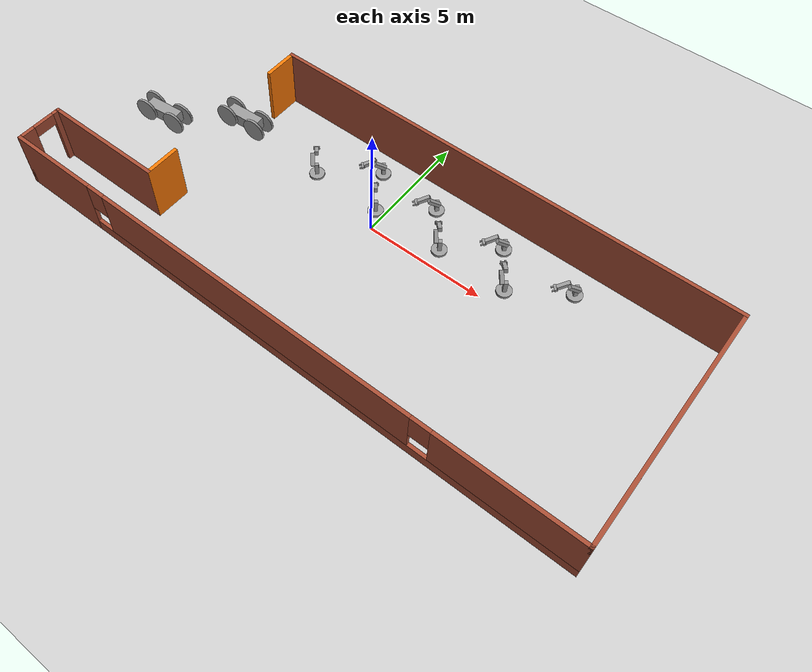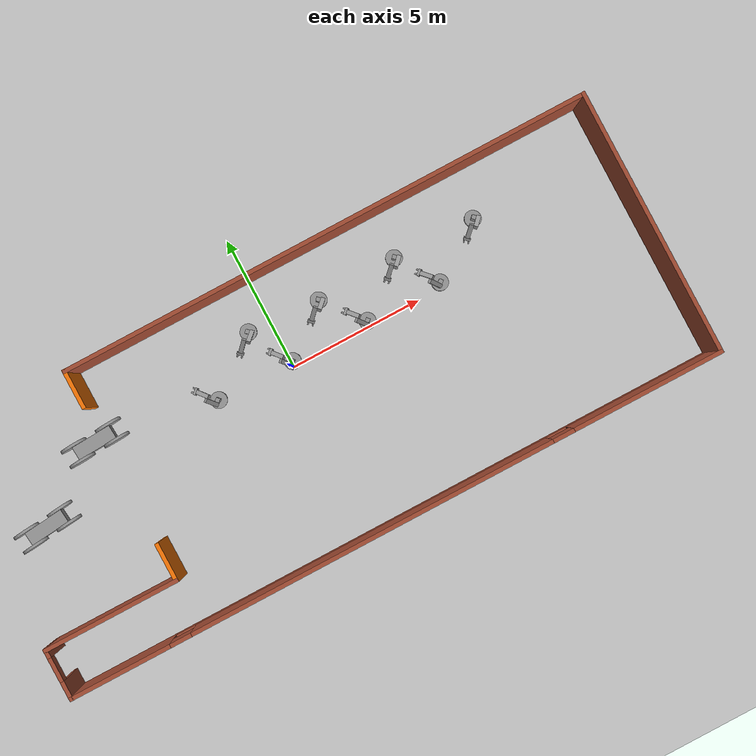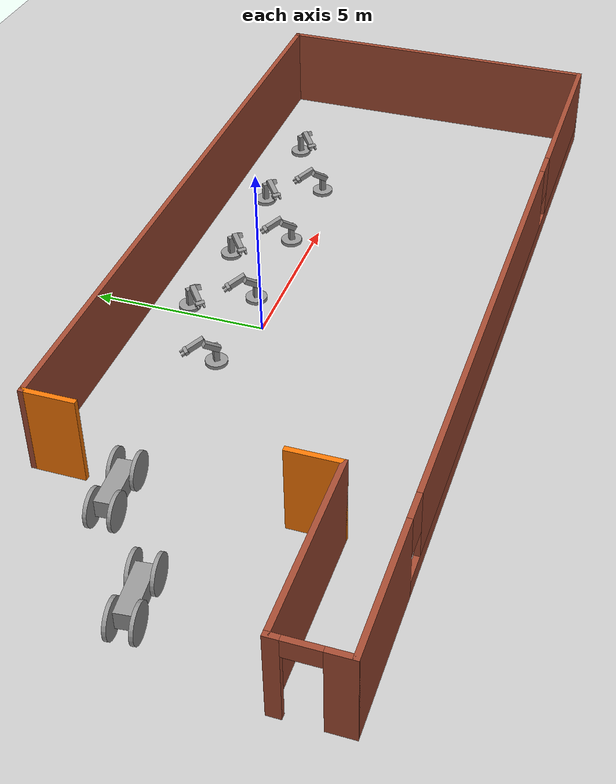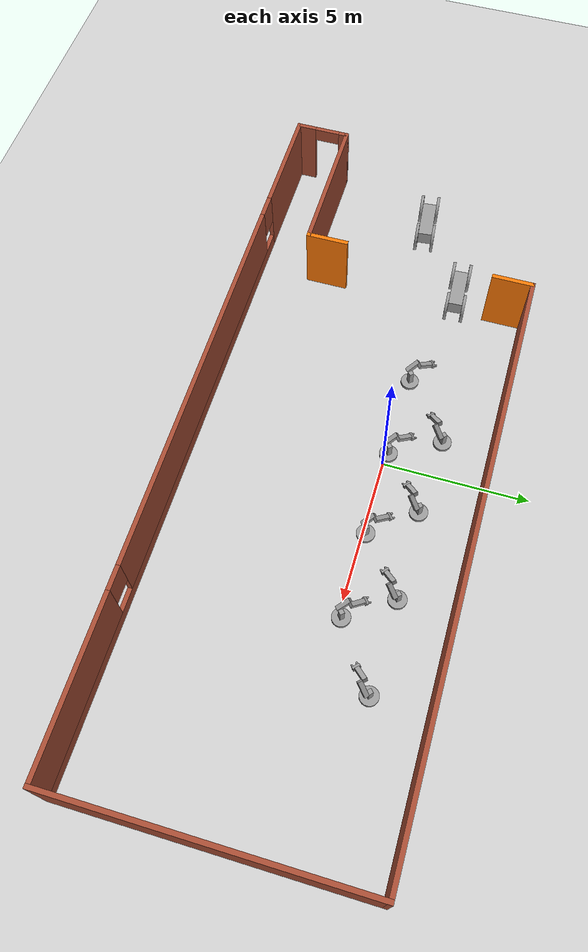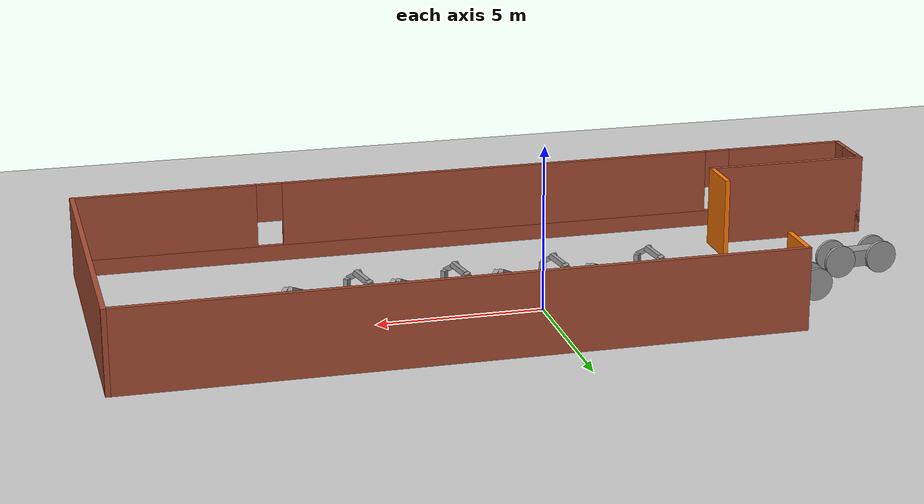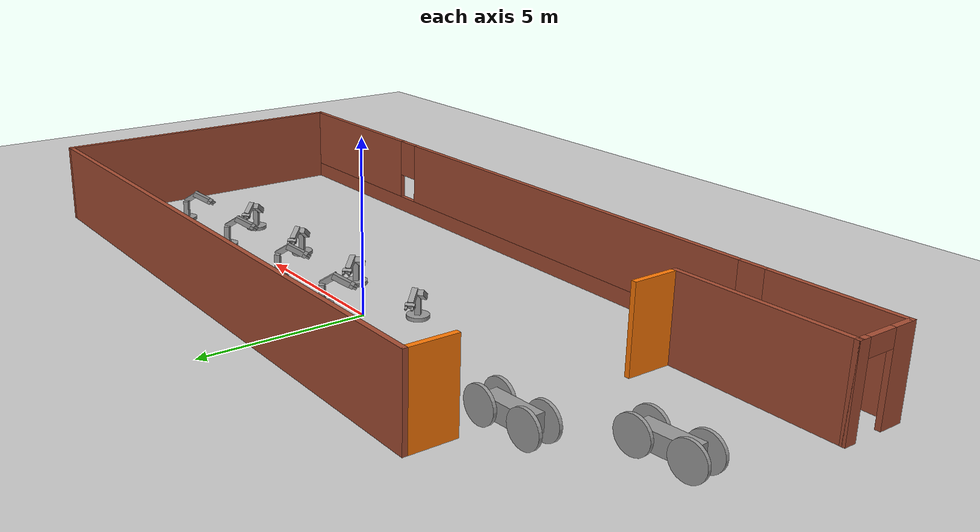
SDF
<sdf version="1.7">
 <world name="default">
  <light name="sun" type="directional">
   <pose>0 0 10 0 -0 0</pose>
   <diffuse>0.8 0.8 0.8 1</diffuse>
   <specular>0.2 0.2 0.2 1</specular>
   <attenuation>
    <range>1000</range>
    <constant>0.9</constant>
    <linear>0.01</linear>
    <quadratic>0.001</quadratic>
   </attenuation>
   <direction>-0.5 0.1 -0.9</direction>
   <spot><inner_angle>0</inner_angle><outer_angle>0</outer_angle><falloff>0</falloff></spot>
  </light>
  <model name="ground_plane">
   <static>1</static>
   <link name="link">
    <collision name="collision">
     <geometry><plane><normal>0 0 1</normal><size>100 100</size></plane></geometry>
     <surface>
      <contact><collide_bitmask>65535</collide_bitmask></contact>
      <friction><ode><mu>100</mu><mu2>50</mu2></ode></friction>
     </surface>
    </collision>
    <visual name="visual">
     <cast_shadows>0</cast_shadows>
     <geometry><plane><normal>0 0 1</normal><size>100 100</size></plane></geometry>
     <material>
      <script><uri>file://media/materials/scripts/gazebo.material</uri><name>Gazebo/Grey</name></script>
     </material>
    </visual>
   </link>
  </model>
  <gravity>0 0 -9.8</gravity>
  <magnetic_field>6e-06 2.3e-05 -4.2e-05</magnetic_field>
  <atmosphere type="adiabatic"/>
  <physics type="ode">
   <max_step_size>0.001</max_step_size>
   <real_time_factor>1</real_time_factor>
   <real_time_update_rate>1000</real_time_update_rate>
  </physics>
  <scene><ambient>0.4 0.4 0.4 1</ambient><background>0.7 0.7 0.7 1</background><shadows>1</shadows></scene>
  <spherical_coordinates>
   <surface_model>EARTH_WGS84</surface_model>
   <latitude_deg>0</latitude_deg>
   <longitude_deg>0</longitude_deg>
   <elevation>0</elevation>
   <heading_deg>0</heading_deg>
  </spherical_coordinates>
  <model name="building">
   <pose>0.594208 -1.50315 0 0 -0 0</pose>
   <link name="Wall_0">
    <pose>-1e-06 -4.925 0 0 -0 0</pose>
    <visual name="Wall_0_Visual_0">
     <pose>-10.5687 0 1.25 0 -0 0</pose>
     <geometry><box><size>3.86253 0.15 2.5</size></box></geometry>
     <material>
      <script><uri>file://media/materials/scripts/gazebo.material</uri><name>Gazebo/Bricks</name></script>
      <ambient>1 1 1 1</ambient>
     </material>
     <meta><layer>0</layer></meta>
    </visual>
    <collision name="Wall_0_Collision_0">
     <geometry><box><size>3.86253 0.15 2.5</size></box></geometry>
     <pose>-10.5687 0 1.25 0 -0 0</pose>
    </collision>
    <visual name="Wall_0_Visual_1">
     <pose>1.93126 0 0.25 0 -0 0</pose>
     <geometry><box><size>21.1375 0.15 0.5</size></box></geometry>
     <material>
      <script><uri>file://media/materials/scripts/gazebo.material</uri><name>Gazebo/Bricks</name></script>
      <ambient>1 1 1 1</ambient>
     </material>
     <meta><layer>0</layer></meta>
    </visual>
    <collision name="Wall_0_Collision_1">
     <geometry><box><size>21.1375 0.15 0.5</size></box></geometry>
     <pose>1.93126 0 0.25 0 -0 0</pose>
    </collision>
    <visual name="Wall_0_Visual_2">
     <pose>-0.911973 0 1.5 0 -0 0</pose>
     <geometry><box><size>13.851 0.15 2</size></box></geometry>
     <material>
      <script><uri>file://media/materials/scripts/gazebo.material</uri><name>Gazebo/Bricks</name></script>
      <ambient>1 1 1 1</ambient>
     </material>
     <meta><layer>0</layer></meta>
    </visual>
    <collision name="Wall_0_Collision_2">
     <geometry><box><size>13.851 0.15 2</size></box></geometry>
     <pose>-0.911973 0 1.5 0 -0 0</pose>
    </collision>
    <visual name="Wall_0_Visual_3">
     <pose>9.65676 0 1.5 0 -0 0</pose>
     <geometry><box><size>5.68647 0.15 2</size></box></geometry>
     <material>
      <script><uri>file://media/materials/scripts/gazebo.material</uri><name>Gazebo/Bricks</name></script>
      <ambient>1 1 1 1</ambient>
     </material>
     <meta><layer>0</layer></meta>
    </visual>
    <collision name="Wall_0_Collision_3">
     <geometry><box><size>5.68647 0.15 2</size></box></geometry>
     <pose>9.65676 0 1.5 0 -0 0</pose>
    </collision>
    <visual name="Wall_0_Visual_4">
     <pose>-8.23747 0 1.9 0 -0 0</pose>
     <geometry><box><size>0.8 0.15 1.2</size></box></geometry>
     <material>
      <script><uri>file://media/materials/scripts/gazebo.material</uri><name>Gazebo/Bricks</name></script>
      <ambient>1 1 1 1</ambient>
     </material>
     <meta><layer>0</layer></meta>
    </visual>
    <collision name="Wall_0_Collision_4">
     <geometry><box><size>0.8 0.15 1.2</size></box></geometry>
     <pose>-8.23747 0 1.9 0 -0 0</pose>
    </collision>
    <visual name="Wall_0_Visual_5">
     <pose>6.41353 0 1.9 0 -0 0</pose>
     <geometry><box><size>0.8 0.15 1.2</size></box></geometry>
     <material>
      <script><uri>file://media/materials/scripts/gazebo.material</uri><name>Gazebo/Bricks</name></script>
      <ambient>1 1 1 1</ambient>
     </material>
     <meta><layer>0</layer></meta>
    </visual>
    <collision name="Wall_0_Collision_5">
     <geometry><box><size>0.8 0.15 1.2</size></box></geometry>
     <pose>6.41353 0 1.9 0 -0 0</pose>
    </collision>
   </link>
   <link name="Wall_10">
    <collision name="Wall_10_Collision">
     <geometry><box><size>1.5 0.15 2.5</size></box></geometry>
     <pose>0 0 1.25 0 -0 0</pose>
    </collision>
    <visual name="Wall_10_Visual">
     <pose>0 0 1.25 0 -0 0</pose>
     <geometry><box><size>1.5 0.15 2.5</size></box></geometry>
     <material>
      <script><uri>file://media/materials/scripts/gazebo.material</uri><name>Gazebo/Grey</name></script>
      <ambient>0.996078 0.47451 0.0196078 1</ambient>
     </material>
     <meta><layer>0</layer></meta>
    </visual>
    <pose>-7.425 -2.4 0 0 -0 1.5708</pose>
   </link>
   <link name="Wall_2">
    <pose>-12.425 -4 0 0 -0 1.5708</pose>
    <visual name="Wall_2_Visual_0">
     <pose>-0.63494 0 1.25 0 -0 0</pose>
     <geometry><box><size>0.73012 0.15 2.5</size></box></geometry>
     <material>
      <script><uri>file://media/materials/scripts/gazebo.material</uri><name>Gazebo/Bricks</name></script>
      <ambient>1 1 1 1</ambient>
     </material>
     <meta><layer>0</layer></meta>
    </visual>
    <collision name="Wall_2_Collision_0">
     <geometry><box><size>0.73012 0.15 2.5</size></box></geometry>
     <pose>-0.63494 0 1.25 0 -0 0</pose>
    </collision>
    <visual name="Wall_2_Visual_1">
     <pose>0.81506 0 1.25 0 -0 0</pose>
     <geometry><box><size>0.36988 0.15 2.5</size></box></geometry>
     <material>
      <script><uri>file://media/materials/scripts/gazebo.material</uri><name>Gazebo/Bricks</name></script>
      <ambient>1 1 1 1</ambient>
     </material>
     <meta><layer>0</layer></meta>
    </visual>
    <collision name="Wall_2_Collision_1">
     <geometry><box><size>0.36988 0.15 2.5</size></box></geometry>
     <pose>0.81506 0 1.25 0 -0 0</pose>
    </collision>
    <visual name="Wall_2_Visual_2">
     <pose>0.18012 0 2.25 0 -0 0</pose>
     <geometry><box><size>0.9 0.15 0.5</size></box></geometry>
     <material>
      <script><uri>file://media/materials/scripts/gazebo.material</uri><name>Gazebo/Bricks</name></script>
      <ambient>1 1 1 1</ambient>
     </material>
     <meta><layer>0</layer></meta>
    </visual>
    <collision name="Wall_2_Collision_2">
     <geometry><box><size>0.9 0.15 0.5</size></box></geometry>
     <pose>0.18012 0 2.25 0 -0 0</pose>
    </collision>
   </link>
   <link name="Wall_4">
    <collision name="Wall_4_Collision">
     <geometry><box><size>10 0.15 2.5</size></box></geometry>
     <pose>0 0 1.25 0 -0 0</pose>
    </collision>
    <visual name="Wall_4_Visual">
     <pose>0 0 1.25 0 -0 0</pose>
     <geometry><box><size>10 0.15 2.5</size></box></geometry>
     <material>
      <script><uri>file://media/materials/scripts/gazebo.material</uri><name>Gazebo/Bricks</name></script>
      <ambient>1 1 1 1</ambient>
     </material>
     <meta><layer>0</layer></meta>
    </visual>
    <pose>12.425 -0 0 0 -0 1.5708</pose>
   </link>
   <link name="Wall_5">
    <collision name="Wall_5_Collision">
     <geometry><box><size>20 0.15 2.5</size></box></geometry>
     <pose>0 0 1.25 0 -0 0</pose>
    </collision>
    <visual name="Wall_5_Visual">
     <pose>0 0 1.25 0 -0 0</pose>
     <geometry><box><size>20 0.15 2.5</size></box></geometry>
     <material>
      <script><uri>file://media/materials/scripts/gazebo.material</uri><name>Gazebo/Bricks</name></script>
      <ambient>1 1 1 1</ambient>
     </material>
     <meta><layer>0</layer></meta>
    </visual>
    <pose>2.5 4.925 0 0 -0 3.14159</pose>
   </link>
   <link name="Wall_6">
    <collision name="Wall_6_Collision">
     <geometry><box><size>1.5 0.15 2.5</size></box></geometry>
     <pose>0 0 1.25 0 -0 0</pose>
    </collision>
    <visual name="Wall_6_Visual">
     <pose>0 0 1.25 0 -0 0</pose>
     <geometry><box><size>1.5 0.15 2.5</size></box></geometry>
     <material>
      <script><uri>file://media/materials/scripts/gazebo.material</uri><name>Gazebo/Grey</name></script>
      <ambient>0.996078 0.47451 0.0196078 1</ambient>
     </material>
     <meta><layer>0</layer></meta>
    </visual>
    <pose>-7.425 4.25 0 0 -0 -1.5708</pose>
   </link>
   <link name="Wall_8">
    <collision name="Wall_8_Collision">
     <geometry><box><size>5.15 0.15 2.5</size></box></geometry>
     <pose>0 0 1.25 0 -0 0</pose>
    </collision>
    <visual name="Wall_8_Visual">
     <pose>0 0 1.25 0 -0 0</pose>
     <geometry><box><size>5.15 0.15 2.5</size></box></geometry>
     <material>
      <script><uri>file://media/materials/scripts/gazebo.material</uri><name>Gazebo/Bricks</name></script>
      <ambient>1 1 1 1</ambient>
     </material>
     <meta><layer>0</layer></meta>
    </visual>
    <pose>-9.925 -3.075 0 0 -0 0</pose>
   </link>
   <static>1</static>
  </model>
  <model name="fixed_arm_robot">
   <link name="link_0">
    <inertial>
     <mass>1</mass>
     <inertia><ixx>0.145833</ixx><ixy>0</ixy><ixz>0</ixz><iyy>0.145833</iyy><iyz>0</iyz><izz>0.125</izz></inertia>
    </inertial>
    <pose>-0.37347 -0.501985 -0.410714 0 -0 0</pose>
    <visual name="visual">
     <geometry><cylinder><radius>0.3</radius><length>0.1</length></cylinder></geometry>
     <material>
      <lighting>1</lighting>
      <script><uri>file://media/materials/scripts/gazebo.material</uri><name>Gazebo/Grey</name></script>
      <shader type="pixel"><normal_map>__default__</normal_map></shader>
      <ambient>0.3 0.3 0.3 1</ambient>
      <diffuse>0.7 0.7 0.7 1</diffuse>
      <specular>0.01 0.01 0.01 1</specular>
      <emissive>0 0 0 1</emissive>
     </material>
    </visual>
    <collision name="collision">
     <geometry><cylinder><radius>0.3</radius><length>0.1</length></cylinder></geometry>
     <surface>
      <friction>
       <ode><mu>1</mu><mu2>1</mu2><fdir1>0 0 0</fdir1><slip1>0</slip1><slip2>0</slip2></ode>
       <torsional>
        <coefficient>1</coefficient>
        <patch_radius>0</patch_radius>
        <surface_radius>0</surface_radius>
        <use_patch_radius>1</use_patch_radius>
        <ode><slip>0</slip></ode>
       </torsional>
      </friction>
      <bounce><restitution_coefficient>0</restitution_coefficient><threshold>1e+06</threshold></bounce>
      <contact>
       <collide_without_contact>0</collide_without_contact>
       <collide_without_contact_bitmask>1</collide_without_contact_bitmask>
       <collide_bitmask>1</collide_bitmask>
       <ode>
        <soft_cfm>0</soft_cfm>
        <soft_erp>0.2</soft_erp>
        <kp>1e+13</kp>
        <kd>1</kd>
        <max_vel>0.01</max_vel>
        <min_depth>0</min_depth>
       </ode>
       <bullet>
        <split_impulse>1</split_impulse>
        <split_impulse_penetration_threshold>-0.01</split_impulse_penetration_threshold>
        <soft_cfm>0</soft_cfm>
        <soft_erp>0.2</soft_erp>
        <kp>1e+13</kp>
        <kd>1</kd>
       </bullet>
      </contact>
     </surface>
    </collision>
   </link>
   <link name="link_1">
    <inertial>
     <mass>1</mass>
     <inertia>
      <ixx>0.166667</ixx>
      <ixy>0</ixy>
      <ixz>0</ixz>
      <iyy>0.166667</iyy>
      <iyz>0</iyz>
      <izz>0.166667</izz>
     </inertia>
    </inertial>
    <pose>-0.37347 -0.501985 -0.110714 0 -0 0</pose>
    <visual name="visual">
     <geometry><box><size>0.15 0.15 0.5</size></box></geometry>
     <material>
      <lighting>1</lighting>
      <script><uri>file://media/materials/scripts/gazebo.material</uri><name>Gazebo/Grey</name></script>
      <shader type="pixel"><normal_map>__default__</normal_map></shader>
      <ambient>0.3 0.3 0.3 1</ambient>
      <diffuse>0.7 0.7 0.7 1</diffuse>
      <specular>0.01 0.01 0.01 1</specular>
      <emissive>0 0 0 1</emissive>
     </material>
    </visual>
    <collision name="collision">
     <geometry><box><size>0.15 0.15 0.5</size></box></geometry>
     <surface>
      <friction>
       <ode><mu>1</mu><mu2>1</mu2><fdir1>0 0 0</fdir1><slip1>0</slip1><slip2>0</slip2></ode>
       <torsional>
        <coefficient>1</coefficient>
        <patch_radius>0</patch_radius>
        <surface_radius>0</surface_radius>
        <use_patch_radius>1</use_patch_radius>
        <ode><slip>0</slip></ode>
       </torsional>
      </friction>
      <bounce><restitution_coefficient>0</restitution_coefficient><threshold>1e+06</threshold></bounce>
      <contact>
       <collide_without_contact>0</collide_without_contact>
       <collide_without_contact_bitmask>1</collide_without_contact_bitmask>
       <collide_bitmask>1</collide_bitmask>
       <ode>
        <soft_cfm>0</soft_cfm>
        <soft_erp>0.2</soft_erp>
        <kp>1e+13</kp>
        <kd>1</kd>
        <max_vel>0.01</max_vel>
        <min_depth>0</min_depth>
       </ode>
       <bullet>
        <split_impulse>1</split_impulse>
        <split_impulse_penetration_threshold>-0.01</split_impulse_penetration_threshold>
        <soft_cfm>0</soft_cfm>
        <soft_erp>0.2</soft_erp>
        <kp>1e+13</kp>
        <kd>1</kd>
       </bullet>
      </contact>
     </surface>
    </collision>
   </link>
   <link name="link_1_clone">
    <inertial>
     <mass>1</mass>
     <inertia>
      <ixx>0.166667</ixx>
      <ixy>0</ixy>
      <ixz>0</ixz>
      <iyy>0.166667</iyy>
      <iyz>0</iyz>
      <izz>0.166667</izz>
     </inertia>
    </inertial>
    <pose>-0.37347 -0.351985 0.139286 0 1 0</pose>
    <visual name="visual">
     <pose>0 0 0.175 0 -0 0</pose>
     <geometry><box><size>0.15 0.15 0.5</size></box></geometry>
     <material>
      <lighting>1</lighting>
      <script><uri>file://media/materials/scripts/gazebo.material</uri><name>Gazebo/Grey</name></script>
      <shader type="pixel"><normal_map>__default__</normal_map></shader>
      <ambient>0.3 0.3 0.3 1</ambient>
      <diffuse>0.7 0.7 0.7 1</diffuse>
      <specular>0.01 0.01 0.01 1</specular>
      <emissive>0 0 0 1</emissive>
     </material>
    </visual>
    <collision name="collision">
     <pose>0 0 0.175 0 -0 0</pose>
     <geometry><box><size>0.15 0.15 0.5</size></box></geometry>
     <surface>
      <friction>
       <ode><mu>1</mu><mu2>1</mu2><fdir1>0 0 0</fdir1><slip1>0</slip1><slip2>0</slip2></ode>
       <torsional>
        <coefficient>1</coefficient>
        <patch_radius>0</patch_radius>
        <surface_radius>0</surface_radius>
        <use_patch_radius>1</use_patch_radius>
        <ode><slip>0</slip></ode>
       </torsional>
      </friction>
      <bounce><restitution_coefficient>0</restitution_coefficient><threshold>1e+06</threshold></bounce>
      <contact>
       <collide_without_contact>0</collide_without_contact>
       <collide_without_contact_bitmask>1</collide_without_contact_bitmask>
       <collide_bitmask>1</collide_bitmask>
       <ode>
        <soft_cfm>0</soft_cfm>
        <soft_erp>0.2</soft_erp>
        <kp>1e+13</kp>
        <kd>1</kd>
        <max_vel>0.01</max_vel>
        <min_depth>0</min_depth>
       </ode>
       <bullet>
        <split_impulse>1</split_impulse>
        <split_impulse_penetration_threshold>-0.01</split_impulse_penetration_threshold>
        <soft_cfm>0</soft_cfm>
        <soft_erp>0.2</soft_erp>
        <kp>1e+13</kp>
        <kd>1</kd>
       </bullet>
      </contact>
     </surface>
    </collision>
   </link>
   <link name="link_1_clone_clone">
    <inertial>
     <mass>1</mass>
     <inertia>
      <ixx>0.166667</ixx>
      <ixy>0</ixy>
      <ixz>0</ixz>
      <iyy>0.166667</iyy>
      <iyz>0</iyz>
      <izz>0.166667</izz>
     </inertia>
    </inertial>
    <pose>-0.015845 -0.501985 0.368914 3.14159 1.14159 3.14159</pose>
    <visual name="visual">
     <pose>0 0 0.175 0 -0 0</pose>
     <geometry><box><size>0.15 0.15 0.5</size></box></geometry>
     <material>
      <lighting>1</lighting>
      <script><uri>file://media/materials/scripts/gazebo.material</uri><name>Gazebo/Grey</name></script>
      <shader type="pixel"><normal_map>__default__</normal_map></shader>
      <ambient>0.3 0.3 0.3 1</ambient>
      <diffuse>0.7 0.7 0.7 1</diffuse>
      <specular>0.01 0.01 0.01 1</specular>
      <emissive>0 0 0 1</emissive>
     </material>
    </visual>
    <collision name="collision">
     <pose>0 0 0.175 0 -0 0</pose>
     <geometry><box><size>0.15 0.15 0.5</size></box></geometry>
     <surface>
      <friction>
       <ode><mu>1</mu><mu2>1</mu2><fdir1>0 0 0</fdir1><slip1>0</slip1><slip2>0</slip2></ode>
       <torsional>
        <coefficient>1</coefficient>
        <patch_radius>0</patch_radius>
        <surface_radius>0</surface_radius>
        <use_patch_radius>1</use_patch_radius>
        <ode><slip>0</slip></ode>
       </torsional>
      </friction>
      <bounce><restitution_coefficient>0</restitution_coefficient><threshold>1e+06</threshold></bounce>
      <contact>
       <collide_without_contact>0</collide_without_contact>
       <collide_without_contact_bitmask>1</collide_without_contact_bitmask>
       <collide_bitmask>1</collide_bitmask>
       <ode>
        <soft_cfm>0</soft_cfm>
        <soft_erp>0.2</soft_erp>
        <kp>1e+13</kp>
        <kd>1</kd>
        <max_vel>0.01</max_vel>
        <min_depth>0</min_depth>
       </ode>
       <bullet>
        <split_impulse>1</split_impulse>
        <split_impulse_penetration_threshold>-0.01</split_impulse_penetration_threshold>
        <soft_cfm>0</soft_cfm>
        <soft_erp>0.2</soft_erp>
        <kp>1e+13</kp>
        <kd>1</kd>
       </bullet>
      </contact>
     </surface>
    </collision>
   </link>
   <link name="link_2">
    <inertial>
     <mass>1</mass>
     <inertia>
      <ixx>0.166667</ixx>
      <ixy>0</ixy>
      <ixz>0</ixz>
      <iyy>0.166667</iyy>
      <iyz>0</iyz>
      <izz>0.166667</izz>
     </inertia>
    </inertial>
    <pose>0.416072 -0.501985 0.171244 -1.5708 1.14159 -3.14159</pose>
    <visual name="visual">
     <geometry><box><size>0.1 0.1 0.25</size></box></geometry>
     <material>
      <lighting>1</lighting>
      <script><uri>file://media/materials/scripts/gazebo.material</uri><name>Gazebo/Grey</name></script>
      <shader type="pixel"><normal_map>__default__</normal_map></shader>
      <ambient>0.3 0.3 0.3 1</ambient>
      <diffuse>0.7 0.7 0.7 1</diffuse>
      <specular>0.01 0.01 0.01 1</specular>
      <emissive>0 0 0 1</emissive>
     </material>
    </visual>
    <collision name="collision">
     <geometry><box><size>0.1 0.1 0.25</size></box></geometry>
     <surface>
      <friction>
       <ode><mu>1</mu><mu2>1</mu2><fdir1>0 0 0</fdir1><slip1>0</slip1><slip2>0</slip2></ode>
       <torsional>
        <coefficient>1</coefficient>
        <patch_radius>0</patch_radius>
        <surface_radius>0</surface_radius>
        <use_patch_radius>1</use_patch_radius>
        <ode><slip>0</slip></ode>
       </torsional>
      </friction>
      <bounce><restitution_coefficient>0</restitution_coefficient><threshold>1e+06</threshold></bounce>
      <contact>
       <collide_without_contact>0</collide_without_contact>
       <collide_without_contact_bitmask>1</collide_without_contact_bitmask>
       <collide_bitmask>1</collide_bitmask>
       <ode>
        <soft_cfm>0</soft_cfm>
        <soft_erp>0.2</soft_erp>
        <kp>1e+13</kp>
        <kd>1</kd>
        <max_vel>0.01</max_vel>
        <min_depth>0</min_depth>
       </ode>
       <bullet>
        <split_impulse>1</split_impulse>
        <split_impulse_penetration_threshold>-0.01</split_impulse_penetration_threshold>
        <soft_cfm>0</soft_cfm>
        <soft_erp>0.2</soft_erp>
        <kp>1e+13</kp>
        <kd>1</kd>
       </bullet>
      </contact>
     </surface>
    </collision>
   </link>
   <link name="link_3">
    <inertial>
     <mass>1</mass>
     <inertia>
      <ixx>0.166667</ixx>
      <ixy>0</ixy>
      <ixz>0</ixz>
      <iyy>0.166667</iyy>
      <iyz>0</iyz>
      <izz>0.166667</izz>
     </inertia>
    </inertial>
    <pose>0.507001 -0.421985 0.12963 -1e-06 1.14159 -3.14159</pose>
    <visual name="visual">
     <geometry><box><size>0.05 0.05 0.1</size></box></geometry>
     <material>
      <lighting>1</lighting>
      <script><uri>file://media/materials/scripts/gazebo.material</uri><name>Gazebo/Grey</name></script>
      <shader type="pixel"><normal_map>__default__</normal_map></shader>
      <ambient>0.3 0.3 0.3 1</ambient>
      <diffuse>0.7 0.7 0.7 1</diffuse>
      <specular>0.01 0.01 0.01 1</specular>
      <emissive>0 0 0 1</emissive>
     </material>
    </visual>
    <collision name="collision">
     <geometry><box><size>0.05 0.05 0.1</size></box></geometry>
     <surface>
      <friction>
       <ode><mu>1</mu><mu2>1</mu2><fdir1>0 0 0</fdir1><slip1>0</slip1><slip2>0</slip2></ode>
       <torsional>
        <coefficient>1</coefficient>
        <patch_radius>0</patch_radius>
        <surface_radius>0</surface_radius>
        <use_patch_radius>1</use_patch_radius>
        <ode><slip>0</slip></ode>
       </torsional>
      </friction>
      <bounce><restitution_coefficient>0</restitution_coefficient><threshold>1e+06</threshold></bounce>
      <contact>
       <collide_without_contact>0</collide_without_contact>
       <collide_without_contact_bitmask>1</collide_without_contact_bitmask>
       <collide_bitmask>1</collide_bitmask>
       <ode>
        <soft_cfm>0</soft_cfm>
        <soft_erp>0.2</soft_erp>
        <kp>1e+13</kp>
        <kd>1</kd>
        <max_vel>0.01</max_vel>
        <min_depth>0</min_depth>
       </ode>
       <bullet>
        <split_impulse>1</split_impulse>
        <split_impulse_penetration_threshold>-0.01</split_impulse_penetration_threshold>
        <soft_cfm>0</soft_cfm>
        <soft_erp>0.2</soft_erp>
        <kp>1e+13</kp>
        <kd>1</kd>
       </bullet>
      </contact>
     </surface>
    </collision>
   </link>
   <link name="link_3_clone">
    <inertial>
     <mass>1</mass>
     <inertia>
      <ixx>0.166667</ixx>
      <ixy>0</ixy>
      <ixz>0</ixz>
      <iyy>0.166667</iyy>
      <iyz>0</iyz>
      <izz>0.166667</izz>
     </inertia>
    </inertial>
    <pose>0.507002 -0.581985 0.12963 -1e-06 1.14159 -3.14159</pose>
    <visual name="visual">
     <geometry><box><size>0.05 0.05 0.1</size></box></geometry>
     <material>
      <lighting>1</lighting>
      <script><uri>file://media/materials/scripts/gazebo.material</uri><name>Gazebo/Grey</name></script>
      <shader type="pixel"><normal_map>__default__</normal_map></shader>
      <ambient>0.3 0.3 0.3 1</ambient>
      <diffuse>0.7 0.7 0.7 1</diffuse>
      <specular>0.01 0.01 0.01 1</specular>
      <emissive>0 0 0 1</emissive>
     </material>
    </visual>
    <collision name="collision">
     <geometry><box><size>0.05 0.05 0.1</size></box></geometry>
     <surface>
      <friction>
       <ode><mu>1</mu><mu2>1</mu2><fdir1>0 0 0</fdir1><slip1>0</slip1><slip2>0</slip2></ode>
       <torsional>
        <coefficient>1</coefficient>
        <patch_radius>0</patch_radius>
        <surface_radius>0</surface_radius>
        <use_patch_radius>1</use_patch_radius>
        <ode><slip>0</slip></ode>
       </torsional>
      </friction>
      <bounce><restitution_coefficient>0</restitution_coefficient><threshold>1e+06</threshold></bounce>
      <contact>
       <collide_without_contact>0</collide_without_contact>
       <collide_without_contact_bitmask>1</collide_without_contact_bitmask>
       <collide_bitmask>1</collide_bitmask>
       <ode>
        <soft_cfm>0</soft_cfm>
        <soft_erp>0.2</soft_erp>
        <kp>1e+13</kp>
        <kd>1</kd>
        <max_vel>0.01</max_vel>
        <min_depth>0</min_depth>
       </ode>
       <bullet>
        <split_impulse>1</split_impulse>
        <split_impulse_penetration_threshold>-0.01</split_impulse_penetration_threshold>
        <soft_cfm>0</soft_cfm>
        <soft_erp>0.2</soft_erp>
        <kp>1e+13</kp>
        <kd>1</kd>
       </bullet>
      </contact>
     </surface>
    </collision>
   </link>
   <joint name="link_0_JOINT_0" type="fixed">
    <parent>link_0</parent>
    <child>link_1</child>
    <physics>
     <ode><limit><cfm>0</cfm><erp>0.2</erp></limit><suspension><cfm>0</cfm><erp>0.2</erp></suspension></ode>
    </physics>
   </joint>
   <joint name="link_1_JOINT_5" type="fixed">
    <parent>link_1</parent>
    <child>link_1_clone</child>
    <physics>
     <ode><limit><cfm>0</cfm><erp>0.2</erp></limit><suspension><cfm>0</cfm><erp>0.2</erp></suspension></ode>
    </physics>
   </joint>
   <joint name="link_1_clone_JOINT_6" type="fixed">
    <parent>link_1_clone</parent>
    <child>link_1_clone_clone</child>
    <physics>
     <ode><limit><cfm>0</cfm><erp>0.2</erp></limit><suspension><cfm>0</cfm><erp>0.2</erp></suspension></ode>
    </physics>
   </joint>
   <joint name="link_1_clone_clone_JOINT_8" type="fixed">
    <parent>link_1_clone_clone</parent>
    <child>link_2</child>
    <physics>
     <ode><limit><cfm>0</cfm><erp>0.2</erp></limit><suspension><cfm>0</cfm><erp>0.2</erp></suspension></ode>
    </physics>
   </joint>
   <joint name="link_2_JOINT_9" type="fixed">
    <parent>link_2</parent>
    <child>link_3</child>
    <physics>
     <ode><limit><cfm>0</cfm><erp>0.2</erp></limit><suspension><cfm>0</cfm><erp>0.2</erp></suspension></ode>
    </physics>
   </joint>
   <joint name="link_3_JOINT_10" type="fixed">
    <parent>link_3</parent>
    <child>link_3_clone</child>
    <physics>
     <ode><limit><cfm>0</cfm><erp>0.2</erp></limit><suspension><cfm>0</cfm><erp>0.2</erp></suspension></ode>
    </physics>
   </joint>
   <static>1</static>
   <pose>1.95402 0.977345 1.42548 -1e-06 1e-06 -2.36039</pose>
  </model>
  <model name="car_robot">
   <link name="link_0">
    <inertial>
     <mass>1</mass>
     <inertia>
      <ixx>0.166667</ixx>
      <ixy>0</ixy>
      <ixz>0</ixz>
      <iyy>0.166667</iyy>
      <iyz>0</iyz>
      <izz>0.166667</izz>
     </inertia>
    </inertial>
    <pose>-0.017732 0 0 0 -0 0</pose>
    <visual name="visual">
     <geometry><box><size>1.5 0.5 0.5</size></box></geometry>
     <material>
      <lighting>1</lighting>
      <script><uri>file://media/materials/scripts/gazebo.material</uri><name>Gazebo/Grey</name></script>
      <shader type="pixel"><normal_map>__default__</normal_map></shader>
      <ambient>0.3 0.3 0.3 1</ambient>
      <diffuse>0.7 0.7 0.7 1</diffuse>
      <specular>0.01 0.01 0.01 1</specular>
      <emissive>0 0 0 1</emissive>
     </material>
    </visual>
    <collision name="collision">
     <geometry><box><size>1.5 0.5 0.5</size></box></geometry>
     <surface>
      <friction>
       <ode><mu>1</mu><mu2>1</mu2><fdir1>0 0 0</fdir1><slip1>0</slip1><slip2>0</slip2></ode>
       <torsional>
        <coefficient>1</coefficient>
        <patch_radius>0</patch_radius>
        <surface_radius>0</surface_radius>
        <use_patch_radius>1</use_patch_radius>
        <ode><slip>0</slip></ode>
       </torsional>
      </friction>
      <bounce><restitution_coefficient>0</restitution_coefficient><threshold>1e+06</threshold></bounce>
      <contact>
       <collide_without_contact>0</collide_without_contact>
       <collide_without_contact_bitmask>1</collide_without_contact_bitmask>
       <collide_bitmask>1</collide_bitmask>
       <ode>
        <soft_cfm>0</soft_cfm>
        <soft_erp>0.2</soft_erp>
        <kp>1e+13</kp>
        <kd>1</kd>
        <max_vel>0.01</max_vel>
        <min_depth>0</min_depth>
       </ode>
       <bullet>
        <split_impulse>1</split_impulse>
        <split_impulse_penetration_threshold>-0.01</split_impulse_penetration_threshold>
        <soft_cfm>0</soft_cfm>
        <soft_erp>0.2</soft_erp>
        <kp>1e+13</kp>
        <kd>1</kd>
       </bullet>
      </contact>
     </surface>
    </collision>
   </link>
   <link name="link_1">
    <inertial>
     <mass>1</mass>
     <inertia><ixx>0.145833</ixx><ixy>0</ixy><ixz>0</ixz><iyy>0.145833</iyy><iyz>0</iyz><izz>0.125</izz></inertia>
    </inertial>
    <pose>-0.717732 -0.300002 0 1.5708 -0 0</pose>
    <visual name="visual">
     <geometry><cylinder><radius>0.5</radius><length>0.1</length></cylinder></geometry>
     <material>
      <lighting>1</lighting>
      <script><uri>file://media/materials/scripts/gazebo.material</uri><name>Gazebo/Grey</name></script>
      <shader type="pixel"><normal_map>__default__</normal_map></shader>
      <ambient>0.3 0.3 0.3 1</ambient>
      <diffuse>0.7 0.7 0.7 1</diffuse>
      <specular>0.01 0.01 0.01 1</specular>
      <emissive>0 0 0 1</emissive>
     </material>
    </visual>
    <collision name="collision">
     <geometry><cylinder><radius>0.5</radius><length>0.1</length></cylinder></geometry>
     <surface>
      <friction>
       <ode><mu>1</mu><mu2>1</mu2><fdir1>0 0 0</fdir1><slip1>0</slip1><slip2>0</slip2></ode>
       <torsional>
        <coefficient>1</coefficient>
        <patch_radius>0</patch_radius>
        <surface_radius>0</surface_radius>
        <use_patch_radius>1</use_patch_radius>
        <ode><slip>0</slip></ode>
       </torsional>
      </friction>
      <bounce><restitution_coefficient>0</restitution_coefficient><threshold>1e+06</threshold></bounce>
      <contact>
       <collide_without_contact>0</collide_without_contact>
       <collide_without_contact_bitmask>1</collide_without_contact_bitmask>
       <collide_bitmask>1</collide_bitmask>
       <ode>
        <soft_cfm>0</soft_cfm>
        <soft_erp>0.2</soft_erp>
        <kp>1e+13</kp>
        <kd>1</kd>
        <max_vel>0.01</max_vel>
        <min_depth>0</min_depth>
       </ode>
       <bullet>
        <split_impulse>1</split_impulse>
        <split_impulse_penetration_threshold>-0.01</split_impulse_penetration_threshold>
        <soft_cfm>0</soft_cfm>
        <soft_erp>0.2</soft_erp>
        <kp>1e+13</kp>
        <kd>1</kd>
       </bullet>
      </contact>
     </surface>
    </collision>
   </link>
   <link name="link_1_clone">
    <inertial>
     <mass>1</mass>
     <inertia><ixx>0.145833</ixx><ixy>0</ixy><ixz>0</ixz><iyy>0.145833</iyy><iyz>0</iyz><izz>0.125</izz></inertia>
    </inertial>
    <pose>0.682268 -0.300002 0 1.5708 -0 0</pose>
    <visual name="visual">
     <geometry><cylinder><radius>0.5</radius><length>0.1</length></cylinder></geometry>
     <material>
      <lighting>1</lighting>
      <script><uri>file://media/materials/scripts/gazebo.material</uri><name>Gazebo/Grey</name></script>
      <shader type="pixel"><normal_map>__default__</normal_map></shader>
      <ambient>0.3 0.3 0.3 1</ambient>
      <diffuse>0.7 0.7 0.7 1</diffuse>
      <specular>0.01 0.01 0.01 1</specular>
      <emissive>0 0 0 1</emissive>
     </material>
    </visual>
    <collision name="collision">
     <geometry><cylinder><radius>0.5</radius><length>0.1</length></cylinder></geometry>
     <surface>
      <friction>
       <ode><mu>1</mu><mu2>1</mu2><fdir1>0 0 0</fdir1><slip1>0</slip1><slip2>0</slip2></ode>
       <torsional>
        <coefficient>1</coefficient>
        <patch_radius>0</patch_radius>
        <surface_radius>0</surface_radius>
        <use_patch_radius>1</use_patch_radius>
        <ode><slip>0</slip></ode>
       </torsional>
      </friction>
      <bounce><restitution_coefficient>0</restitution_coefficient><threshold>1e+06</threshold></bounce>
      <contact>
       <collide_without_contact>0</collide_without_contact>
       <collide_without_contact_bitmask>1</collide_without_contact_bitmask>
       <collide_bitmask>1</collide_bitmask>
       <ode>
        <soft_cfm>0</soft_cfm>
        <soft_erp>0.2</soft_erp>
        <kp>1e+13</kp>
        <kd>1</kd>
        <max_vel>0.01</max_vel>
        <min_depth>0</min_depth>
       </ode>
       <bullet>
        <split_impulse>1</split_impulse>
        <split_impulse_penetration_threshold>-0.01</split_impulse_penetration_threshold>
        <soft_cfm>0</soft_cfm>
        <soft_erp>0.2</soft_erp>
        <kp>1e+13</kp>
        <kd>1</kd>
       </bullet>
      </contact>
     </surface>
    </collision>
   </link>
   <link name="link_1_clone_0">
    <inertial>
     <mass>1</mass>
     <inertia><ixx>0.145833</ixx><ixy>0</ixy><ixz>0</ixz><iyy>0.145833</iyy><iyz>0</iyz><izz>0.125</izz></inertia>
    </inertial>
    <pose>-0.717732 0.300002 0 1.5708 -0 0</pose>
    <visual name="visual">
     <geometry><cylinder><radius>0.5</radius><length>0.1</length></cylinder></geometry>
     <material>
      <lighting>1</lighting>
      <script><uri>file://media/materials/scripts/gazebo.material</uri><name>Gazebo/Grey</name></script>
      <shader type="pixel"><normal_map>__default__</normal_map></shader>
      <ambient>0.3 0.3 0.3 1</ambient>
      <diffuse>0.7 0.7 0.7 1</diffuse>
      <specular>0.01 0.01 0.01 1</specular>
      <emissive>0 0 0 1</emissive>
     </material>
    </visual>
    <collision name="collision">
     <geometry><cylinder><radius>0.5</radius><length>0.1</length></cylinder></geometry>
     <surface>
      <friction>
       <ode><mu>1</mu><mu2>1</mu2><fdir1>0 0 0</fdir1><slip1>0</slip1><slip2>0</slip2></ode>
       <torsional>
        <coefficient>1</coefficient>
        <patch_radius>0</patch_radius>
        <surface_radius>0</surface_radius>
        <use_patch_radius>1</use_patch_radius>
        <ode><slip>0</slip></ode>
       </torsional>
      </friction>
      <bounce><restitution_coefficient>0</restitution_coefficient><threshold>1e+06</threshold></bounce>
      <contact>
       <collide_without_contact>0</collide_without_contact>
       <collide_without_contact_bitmask>1</collide_without_contact_bitmask>
       <collide_bitmask>1</collide_bitmask>
       <ode>
        <soft_cfm>0</soft_cfm>
        <soft_erp>0.2</soft_erp>
        <kp>1e+13</kp>
        <kd>1</kd>
        <max_vel>0.01</max_vel>
        <min_depth>0</min_depth>
       </ode>
       <bullet>
        <split_impulse>1</split_impulse>
        <split_impulse_penetration_threshold>-0.01</split_impulse_penetration_threshold>
        <soft_cfm>0</soft_cfm>
        <soft_erp>0.2</soft_erp>
        <kp>1e+13</kp>
        <kd>1</kd>
       </bullet>
      </contact>
     </surface>
    </collision>
   </link>
   <link name="link_1_clone_1">
    <inertial>
     <mass>1</mass>
     <inertia><ixx>0.145833</ixx><ixy>0</ixy><ixz>0</ixz><iyy>0.145833</iyy><iyz>0</iyz><izz>0.125</izz></inertia>
    </inertial>
    <pose>0.682268 0.300002 0 1.5708 -0 0</pose>
    <visual name="visual">
     <geometry><cylinder><radius>0.5</radius><length>0.1</length></cylinder></geometry>
     <material>
      <lighting>1</lighting>
      <script><uri>file://media/materials/scripts/gazebo.material</uri><name>Gazebo/Grey</name></script>
      <shader type="pixel"><normal_map>__default__</normal_map></shader>
      <ambient>0.3 0.3 0.3 1</ambient>
      <diffuse>0.7 0.7 0.7 1</diffuse>
      <specular>0.01 0.01 0.01 1</specular>
      <emissive>0 0 0 1</emissive>
     </material>
    </visual>
    <collision name="collision">
     <geometry><cylinder><radius>0.5</radius><length>0.1</length></cylinder></geometry>
     <surface>
      <friction>
       <ode><mu>1</mu><mu2>1</mu2><fdir1>0 0 0</fdir1><slip1>0</slip1><slip2>0</slip2></ode>
       <torsional>
        <coefficient>1</coefficient>
        <patch_radius>0</patch_radius>
        <surface_radius>0</surface_radius>
        <use_patch_radius>1</use_patch_radius>
        <ode><slip>0</slip></ode>
       </torsional>
      </friction>
      <bounce><restitution_coefficient>0</restitution_coefficient><threshold>1e+06</threshold></bounce>
      <contact>
       <collide_without_contact>0</collide_without_contact>
       <collide_without_contact_bitmask>1</collide_without_contact_bitmask>
       <collide_bitmask>1</collide_bitmask>
       <ode>
        <soft_cfm>0</soft_cfm>
        <soft_erp>0.2</soft_erp>
        <kp>1e+13</kp>
        <kd>1</kd>
        <max_vel>0.01</max_vel>
        <min_depth>0</min_depth>
       </ode>
       <bullet>
        <split_impulse>1</split_impulse>
        <split_impulse_penetration_threshold>-0.01</split_impulse_penetration_threshold>
        <soft_cfm>0</soft_cfm>
        <soft_erp>0.2</soft_erp>
        <kp>1e+13</kp>
        <kd>1</kd>
       </bullet>
      </contact>
     </surface>
    </collision>
   </link>
   <joint name="link_0_JOINT_0" type="revolute">
    <parent>link_0</parent>
    <child>link_1</child>
    <pose>0 0 0 -0.01 0 0</pose>
    <axis>
     <xyz>0 0 1</xyz>
     <limit>
      <lower>-1.79769e+308</lower>
      <upper>1.79769e+308</upper>
      <effort>-1</effort>
      <velocity>-1</velocity>
     </limit>
     <dynamics>
      <spring_reference>0</spring_reference>
      <spring_stiffness>0</spring_stiffness>
      <damping>0</damping>
     </dynamics>
    </axis>
    <physics>
     <ode><limit><cfm>0</cfm><erp>0.2</erp></limit><suspension><cfm>0</cfm><erp>0.2</erp></suspension></ode>
    </physics>
   </joint>
   <joint name="link_0_JOINT_1" type="revolute">
    <parent>link_0</parent>
    <child>link_1_clone</child>
    <axis>
     <xyz>0 0 1</xyz>
     <limit>
      <lower>-1.79769e+308</lower>
      <upper>1.79769e+308</upper>
      <effort>-1</effort>
      <velocity>-1</velocity>
     </limit>
     <dynamics>
      <spring_reference>0</spring_reference>
      <spring_stiffness>0</spring_stiffness>
      <damping>0</damping>
     </dynamics>
    </axis>
    <physics>
     <ode><limit><cfm>0</cfm><erp>0.2</erp></limit><suspension><cfm>0</cfm><erp>0.2</erp></suspension></ode>
    </physics>
   </joint>
   <joint name="link_0_JOINT_2" type="revolute">
    <parent>link_0</parent>
    <child>link_1_clone_1</child>
    <axis>
     <xyz>0 0 1</xyz>
     <limit>
      <lower>-1.79769e+308</lower>
      <upper>1.79769e+308</upper>
      <effort>-1</effort>
      <velocity>-1</velocity>
     </limit>
     <dynamics>
      <spring_reference>0</spring_reference>
      <spring_stiffness>0</spring_stiffness>
      <damping>0</damping>
     </dynamics>
    </axis>
    <physics>
     <ode><limit><cfm>0</cfm><erp>0.2</erp></limit><suspension><cfm>0</cfm><erp>0.2</erp></suspension></ode>
    </physics>
   </joint>
   <joint name="link_0_JOINT_3" type="revolute">
    <parent>link_0</parent>
    <child>link_1_clone_0</child>
    <axis>
     <xyz>0 0 1</xyz>
     <limit>
      <lower>-1.79769e+308</lower>
      <upper>1.79769e+308</upper>
      <effort>-1</effort>
      <velocity>-1</velocity>
     </limit>
     <dynamics>
      <spring_reference>0</spring_reference>
      <spring_stiffness>0</spring_stiffness>
      <damping>0</damping>
     </dynamics>
    </axis>
    <physics>
     <ode><limit><cfm>0</cfm><erp>0.2</erp></limit><suspension><cfm>0</cfm><erp>0.2</erp></suspension></ode>
    </physics>
   </joint>
   <static>0</static>
   <pose>-7.34876 0.924185 0.500001 -1e-06 1e-06 0.057087</pose>
  </model>
  <model name="car_robot_0">
   <link name="link_0">
    <inertial>
     <mass>1</mass>
     <inertia>
      <ixx>0.166667</ixx>
      <ixy>0</ixy>
      <ixz>0</ixz>
      <iyy>0.166667</iyy>
      <iyz>0</iyz>
      <izz>0.166667</izz>
     </inertia>
    </inertial>
    <pose>-0.017732 0 0 0 -0 0</pose>
    <visual name="visual">
     <geometry><box><size>1.5 0.5 0.5</size></box></geometry>
     <material>
      <lighting>1</lighting>
      <script><uri>file://media/materials/scripts/gazebo.material</uri><name>Gazebo/Grey</name></script>
      <shader type="pixel"><normal_map>__default__</normal_map></shader>
      <ambient>0.3 0.3 0.3 1</ambient>
      <diffuse>0.7 0.7 0.7 1</diffuse>
      <specular>0.01 0.01 0.01 1</specular>
      <emissive>0 0 0 1</emissive>
     </material>
    </visual>
    <collision name="collision">
     <geometry><box><size>1.5 0.5 0.5</size></box></geometry>
     <surface>
      <friction>
       <ode><mu>1</mu><mu2>1</mu2><fdir1>0 0 0</fdir1><slip1>0</slip1><slip2>0</slip2></ode>
       <torsional>
        <coefficient>1</coefficient>
        <patch_radius>0</patch_radius>
        <surface_radius>0</surface_radius>
        <use_patch_radius>1</use_patch_radius>
        <ode><slip>0</slip></ode>
       </torsional>
      </friction>
      <bounce><restitution_coefficient>0</restitution_coefficient><threshold>1e+06</threshold></bounce>
      <contact>
       <collide_without_contact>0</collide_without_contact>
       <collide_without_contact_bitmask>1</collide_without_contact_bitmask>
       <collide_bitmask>1</collide_bitmask>
       <ode>
        <soft_cfm>0</soft_cfm>
        <soft_erp>0.2</soft_erp>
        <kp>1e+13</kp>
        <kd>1</kd>
        <max_vel>0.01</max_vel>
        <min_depth>0</min_depth>
       </ode>
       <bullet>
        <split_impulse>1</split_impulse>
        <split_impulse_penetration_threshold>-0.01</split_impulse_penetration_threshold>
        <soft_cfm>0</soft_cfm>
        <soft_erp>0.2</soft_erp>
        <kp>1e+13</kp>
        <kd>1</kd>
       </bullet>
      </contact>
     </surface>
    </collision>
   </link>
   <link name="link_1">
    <inertial>
     <mass>1</mass>
     <inertia><ixx>0.145833</ixx><ixy>0</ixy><ixz>0</ixz><iyy>0.145833</iyy><iyz>0</iyz><izz>0.125</izz></inertia>
    </inertial>
    <pose>-0.717732 -0.300002 0 1.5708 -0 0</pose>
    <visual name="visual">
     <geometry><cylinder><radius>0.5</radius><length>0.1</length></cylinder></geometry>
     <material>
      <lighting>1</lighting>
      <script><uri>file://media/materials/scripts/gazebo.material</uri><name>Gazebo/Grey</name></script>
      <shader type="pixel"><normal_map>__default__</normal_map></shader>
      <ambient>0.3 0.3 0.3 1</ambient>
      <diffuse>0.7 0.7 0.7 1</diffuse>
      <specular>0.01 0.01 0.01 1</specular>
      <emissive>0 0 0 1</emissive>
     </material>
    </visual>
    <collision name="collision">
     <geometry><cylinder><radius>0.5</radius><length>0.1</length></cylinder></geometry>
     <surface>
      <friction>
       <ode><mu>1</mu><mu2>1</mu2><fdir1>0 0 0</fdir1><slip1>0</slip1><slip2>0</slip2></ode>
       <torsional>
        <coefficient>1</coefficient>
        <patch_radius>0</patch_radius>
        <surface_radius>0</surface_radius>
        <use_patch_radius>1</use_patch_radius>
        <ode><slip>0</slip></ode>
       </torsional>
      </friction>
      <bounce><restitution_coefficient>0</restitution_coefficient><threshold>1e+06</threshold></bounce>
      <contact>
       <collide_without_contact>0</collide_without_contact>
       <collide_without_contact_bitmask>1</collide_without_contact_bitmask>
       <collide_bitmask>1</collide_bitmask>
       <ode>
        <soft_cfm>0</soft_cfm>
        <soft_erp>0.2</soft_erp>
        <kp>1e+13</kp>
        <kd>1</kd>
        <max_vel>0.01</max_vel>
        <min_depth>0</min_depth>
       </ode>
       <bullet>
        <split_impulse>1</split_impulse>
        <split_impulse_penetration_threshold>-0.01</split_impulse_penetration_threshold>
        <soft_cfm>0</soft_cfm>
        <soft_erp>0.2</soft_erp>
        <kp>1e+13</kp>
        <kd>1</kd>
       </bullet>
      </contact>
     </surface>
    </collision>
   </link>
   <link name="link_1_clone">
    <inertial>
     <mass>1</mass>
     <inertia><ixx>0.145833</ixx><ixy>0</ixy><ixz>0</ixz><iyy>0.145833</iyy><iyz>0</iyz><izz>0.125</izz></inertia>
    </inertial>
    <pose>0.682268 -0.300002 0 1.5708 -0 0</pose>
    <visual name="visual">
     <geometry><cylinder><radius>0.5</radius><length>0.1</length></cylinder></geometry>
     <material>
      <lighting>1</lighting>
      <script><uri>file://media/materials/scripts/gazebo.material</uri><name>Gazebo/Grey</name></script>
      <shader type="pixel"><normal_map>__default__</normal_map></shader>
      <ambient>0.3 0.3 0.3 1</ambient>
      <diffuse>0.7 0.7 0.7 1</diffuse>
      <specular>0.01 0.01 0.01 1</specular>
      <emissive>0 0 0 1</emissive>
     </material>
    </visual>
    <collision name="collision">
     <geometry><cylinder><radius>0.5</radius><length>0.1</length></cylinder></geometry>
     <surface>
      <friction>
       <ode><mu>1</mu><mu2>1</mu2><fdir1>0 0 0</fdir1><slip1>0</slip1><slip2>0</slip2></ode>
       <torsional>
        <coefficient>1</coefficient>
        <patch_radius>0</patch_radius>
        <surface_radius>0</surface_radius>
        <use_patch_radius>1</use_patch_radius>
        <ode><slip>0</slip></ode>
       </torsional>
      </friction>
      <bounce><restitution_coefficient>0</restitution_coefficient><threshold>1e+06</threshold></bounce>
      <contact>
       <collide_without_contact>0</collide_without_contact>
       <collide_without_contact_bitmask>1</collide_without_contact_bitmask>
       <collide_bitmask>1</collide_bitmask>
       <ode>
        <soft_cfm>0</soft_cfm>
        <soft_erp>0.2</soft_erp>
        <kp>1e+13</kp>
        <kd>1</kd>
        <max_vel>0.01</max_vel>
        <min_depth>0</min_depth>
       </ode>
       <bullet>
        <split_impulse>1</split_impulse>
        <split_impulse_penetration_threshold>-0.01</split_impulse_penetration_threshold>
        <soft_cfm>0</soft_cfm>
        <soft_erp>0.2</soft_erp>
        <kp>1e+13</kp>
        <kd>1</kd>
       </bullet>
      </contact>
     </surface>
    </collision>
   </link>
   <link name="link_1_clone_0">
    <inertial>
     <mass>1</mass>
     <inertia><ixx>0.145833</ixx><ixy>0</ixy><ixz>0</ixz><iyy>0.145833</iyy><iyz>0</iyz><izz>0.125</izz></inertia>
    </inertial>
    <pose>-0.717732 0.300002 0 1.5708 -0 0</pose>
    <visual name="visual">
     <geometry><cylinder><radius>0.5</radius><length>0.1</length></cylinder></geometry>
     <material>
      <lighting>1</lighting>
      <script><uri>file://media/materials/scripts/gazebo.material</uri><name>Gazebo/Grey</name></script>
      <shader type="pixel"><normal_map>__default__</normal_map></shader>
      <ambient>0.3 0.3 0.3 1</ambient>
      <diffuse>0.7 0.7 0.7 1</diffuse>
      <specular>0.01 0.01 0.01 1</specular>
      <emissive>0 0 0 1</emissive>
     </material>
    </visual>
    <collision name="collision">
     <geometry><cylinder><radius>0.5</radius><length>0.1</length></cylinder></geometry>
     <surface>
      <friction>
       <ode><mu>1</mu><mu2>1</mu2><fdir1>0 0 0</fdir1><slip1>0</slip1><slip2>0</slip2></ode>
       <torsional>
        <coefficient>1</coefficient>
        <patch_radius>0</patch_radius>
        <surface_radius>0</surface_radius>
        <use_patch_radius>1</use_patch_radius>
        <ode><slip>0</slip></ode>
       </torsional>
      </friction>
      <bounce><restitution_coefficient>0</restitution_coefficient><threshold>1e+06</threshold></bounce>
      <contact>
       <collide_without_contact>0</collide_without_contact>
       <collide_without_contact_bitmask>1</collide_without_contact_bitmask>
       <collide_bitmask>1</collide_bitmask>
       <ode>
        <soft_cfm>0</soft_cfm>
        <soft_erp>0.2</soft_erp>
        <kp>1e+13</kp>
        <kd>1</kd>
        <max_vel>0.01</max_vel>
        <min_depth>0</min_depth>
       </ode>
       <bullet>
        <split_impulse>1</split_impulse>
        <split_impulse_penetration_threshold>-0.01</split_impulse_penetration_threshold>
        <soft_cfm>0</soft_cfm>
        <soft_erp>0.2</soft_erp>
        <kp>1e+13</kp>
        <kd>1</kd>
       </bullet>
      </contact>
     </surface>
    </collision>
   </link>
   <link name="link_1_clone_1">
    <inertial>
     <mass>1</mass>
     <inertia><ixx>0.145833</ixx><ixy>0</ixy><ixz>0</ixz><iyy>0.145833</iyy><iyz>0</iyz><izz>0.125</izz></inertia>
    </inertial>
    <pose>0.682268 0.300002 0 1.5708 -0 0</pose>
    <visual name="visual">
     <geometry><cylinder><radius>0.5</radius><length>0.1</length></cylinder></geometry>
     <material>
      <lighting>1</lighting>
      <script><uri>file://media/materials/scripts/gazebo.material</uri><name>Gazebo/Grey</name></script>
      <shader type="pixel"><normal_map>__default__</normal_map></shader>
      <ambient>0.3 0.3 0.3 1</ambient>
      <diffuse>0.7 0.7 0.7 1</diffuse>
      <specular>0.01 0.01 0.01 1</specular>
      <emissive>0 0 0 1</emissive>
     </material>
    </visual>
    <collision name="collision">
     <geometry><cylinder><radius>0.5</radius><length>0.1</length></cylinder></geometry>
     <surface>
      <friction>
       <ode><mu>1</mu><mu2>1</mu2><fdir1>0 0 0</fdir1><slip1>0</slip1><slip2>0</slip2></ode>
       <torsional>
        <coefficient>1</coefficient>
        <patch_radius>0</patch_radius>
        <surface_radius>0</surface_radius>
        <use_patch_radius>1</use_patch_radius>
        <ode><slip>0</slip></ode>
       </torsional>
      </friction>
      <bounce><restitution_coefficient>0</restitution_coefficient><threshold>1e+06</threshold></bounce>
      <contact>
       <collide_without_contact>0</collide_without_contact>
       <collide_without_contact_bitmask>1</collide_without_contact_bitmask>
       <collide_bitmask>1</collide_bitmask>
       <ode>
        <soft_cfm>0</soft_cfm>
        <soft_erp>0.2</soft_erp>
        <kp>1e+13</kp>
        <kd>1</kd>
        <max_vel>0.01</max_vel>
        <min_depth>0</min_depth>
       </ode>
       <bullet>
        <split_impulse>1</split_impulse>
        <split_impulse_penetration_threshold>-0.01</split_impulse_penetration_threshold>
        <soft_cfm>0</soft_cfm>
        <soft_erp>0.2</soft_erp>
        <kp>1e+13</kp>
        <kd>1</kd>
       </bullet>
      </contact>
     </surface>
    </collision>
   </link>
   <joint name="link_0_JOINT_0" type="revolute">
    <parent>link_0</parent>
    <child>link_1</child>
    <pose>0 0 0 -0.01 0 0</pose>
    <axis>
     <xyz>0 0 1</xyz>
     <limit>
      <lower>-1.79769e+308</lower>
      <upper>1.79769e+308</upper>
      <effort>-1</effort>
      <velocity>-1</velocity>
     </limit>
     <dynamics>
      <spring_reference>0</spring_reference>
      <spring_stiffness>0</spring_stiffness>
      <damping>0</damping>
     </dynamics>
    </axis>
    <physics>
     <ode><limit><cfm>0</cfm><erp>0.2</erp></limit><suspension><cfm>0</cfm><erp>0.2</erp></suspension></ode>
    </physics>
   </joint>
   <joint name="link_0_JOINT_1" type="revolute">
    <parent>link_0</parent>
    <child>link_1_clone</child>
    <axis>
     <xyz>0 0 1</xyz>
     <limit>
      <lower>-1.79769e+308</lower>
      <upper>1.79769e+308</upper>
      <effort>-1</effort>
      <velocity>-1</velocity>
     </limit>
     <dynamics>
      <spring_reference>0</spring_reference>
      <spring_stiffness>0</spring_stiffness>
      <damping>0</damping>
     </dynamics>
    </axis>
    <physics>
     <ode><limit><cfm>0</cfm><erp>0.2</erp></limit><suspension><cfm>0</cfm><erp>0.2</erp></suspension></ode>
    </physics>
   </joint>
   <joint name="link_0_JOINT_2" type="revolute">
    <parent>link_0</parent>
    <child>link_1_clone_1</child>
    <axis>
     <xyz>0 0 1</xyz>
     <limit>
      <lower>-1.79769e+308</lower>
      <upper>1.79769e+308</upper>
      <effort>-1</effort>
      <velocity>-1</velocity>
     </limit>
     <dynamics>
      <spring_reference>0</spring_reference>
      <spring_stiffness>0</spring_stiffness>
      <damping>0</damping>
     </dynamics>
    </axis>
    <physics>
     <ode><limit><cfm>0</cfm><erp>0.2</erp></limit><suspension><cfm>0</cfm><erp>0.2</erp></suspension></ode>
    </physics>
   </joint>
   <joint name="link_0_JOINT_3" type="revolute">
    <parent>link_0</parent>
    <child>link_1_clone_0</child>
    <axis>
     <xyz>0 0 1</xyz>
     <limit>
      <lower>-1.79769e+308</lower>
      <upper>1.79769e+308</upper>
      <effort>-1</effort>
      <velocity>-1</velocity>
     </limit>
     <dynamics>
      <spring_reference>0</spring_reference>
      <spring_stiffness>0</spring_stiffness>
      <damping>0</damping>
     </dynamics>
    </axis>
    <physics>
     <ode><limit><cfm>0</cfm><erp>0.2</erp></limit><suspension><cfm>0</cfm><erp>0.2</erp></suspension></ode>
    </physics>
   </joint>
   <static>0</static>
   <pose>-10.2037 -0.89855 0.5 -2e-06 1e-06 0.100051</pose>
  </model>
  <model name="fixed_arm_robot_clone">
   <link name="link_0">
    <inertial>
     <mass>1</mass>
     <inertia><ixx>0.145833</ixx><ixy>0</ixy><ixz>0</ixz><iyy>0.145833</iyy><iyz>0</iyz><izz>0.125</izz></inertia>
    </inertial>
    <pose>-0.37347 -0.501985 -0.410714 0 -0 0</pose>
    <visual name="visual">
     <geometry><cylinder><radius>0.3</radius><length>0.1</length></cylinder></geometry>
     <material>
      <lighting>1</lighting>
      <script><uri>file://media/materials/scripts/gazebo.material</uri><name>Gazebo/Grey</name></script>
      <shader type="pixel"><normal_map>__default__</normal_map></shader>
      <ambient>0.3 0.3 0.3 1</ambient>
      <diffuse>0.7 0.7 0.7 1</diffuse>
      <specular>0.01 0.01 0.01 1</specular>
      <emissive>0 0 0 1</emissive>
     </material>
    </visual>
    <collision name="collision">
     <geometry><cylinder><radius>0.3</radius><length>0.1</length></cylinder></geometry>
     <surface>
      <friction>
       <ode><mu>1</mu><mu2>1</mu2><fdir1>0 0 0</fdir1><slip1>0</slip1><slip2>0</slip2></ode>
       <torsional>
        <coefficient>1</coefficient>
        <patch_radius>0</patch_radius>
        <surface_radius>0</surface_radius>
        <use_patch_radius>1</use_patch_radius>
        <ode><slip>0</slip></ode>
       </torsional>
      </friction>
      <bounce><restitution_coefficient>0</restitution_coefficient><threshold>1e+06</threshold></bounce>
      <contact>
       <collide_without_contact>0</collide_without_contact>
       <collide_without_contact_bitmask>1</collide_without_contact_bitmask>
       <collide_bitmask>1</collide_bitmask>
       <ode>
        <soft_cfm>0</soft_cfm>
        <soft_erp>0.2</soft_erp>
        <kp>1e+13</kp>
        <kd>1</kd>
        <max_vel>0.01</max_vel>
        <min_depth>0</min_depth>
       </ode>
       <bullet>
        <split_impulse>1</split_impulse>
        <split_impulse_penetration_threshold>-0.01</split_impulse_penetration_threshold>
        <soft_cfm>0</soft_cfm>
        <soft_erp>0.2</soft_erp>
        <kp>1e+13</kp>
        <kd>1</kd>
       </bullet>
      </contact>
     </surface>
    </collision>
   </link>
   <link name="link_1">
    <inertial>
     <mass>1</mass>
     <inertia>
      <ixx>0.166667</ixx>
      <ixy>0</ixy>
      <ixz>0</ixz>
      <iyy>0.166667</iyy>
      <iyz>0</iyz>
      <izz>0.166667</izz>
     </inertia>
    </inertial>
    <pose>-0.37347 -0.501985 -0.110714 0 -0 0</pose>
    <visual name="visual">
     <geometry><box><size>0.15 0.15 0.5</size></box></geometry>
     <material>
      <lighting>1</lighting>
      <script><uri>file://media/materials/scripts/gazebo.material</uri><name>Gazebo/Grey</name></script>
      <shader type="pixel"><normal_map>__default__</normal_map></shader>
      <ambient>0.3 0.3 0.3 1</ambient>
      <diffuse>0.7 0.7 0.7 1</diffuse>
      <specular>0.01 0.01 0.01 1</specular>
      <emissive>0 0 0 1</emissive>
     </material>
    </visual>
    <collision name="collision">
     <geometry><box><size>0.15 0.15 0.5</size></box></geometry>
     <surface>
      <friction>
       <ode><mu>1</mu><mu2>1</mu2><fdir1>0 0 0</fdir1><slip1>0</slip1><slip2>0</slip2></ode>
       <torsional>
        <coefficient>1</coefficient>
        <patch_radius>0</patch_radius>
        <surface_radius>0</surface_radius>
        <use_patch_radius>1</use_patch_radius>
        <ode><slip>0</slip></ode>
       </torsional>
      </friction>
      <bounce><restitution_coefficient>0</restitution_coefficient><threshold>1e+06</threshold></bounce>
      <contact>
       <collide_without_contact>0</collide_without_contact>
       <collide_without_contact_bitmask>1</collide_without_contact_bitmask>
       <collide_bitmask>1</collide_bitmask>
       <ode>
        <soft_cfm>0</soft_cfm>
        <soft_erp>0.2</soft_erp>
        <kp>1e+13</kp>
        <kd>1</kd>
        <max_vel>0.01</max_vel>
        <min_depth>0</min_depth>
       </ode>
       <bullet>
        <split_impulse>1</split_impulse>
        <split_impulse_penetration_threshold>-0.01</split_impulse_penetration_threshold>
        <soft_cfm>0</soft_cfm>
        <soft_erp>0.2</soft_erp>
        <kp>1e+13</kp>
        <kd>1</kd>
       </bullet>
      </contact>
     </surface>
    </collision>
   </link>
   <link name="link_1_clone">
    <inertial>
     <mass>1</mass>
     <inertia>
      <ixx>0.166667</ixx>
      <ixy>0</ixy>
      <ixz>0</ixz>
      <iyy>0.166667</iyy>
      <iyz>0</iyz>
      <izz>0.166667</izz>
     </inertia>
    </inertial>
    <pose>-0.37347 -0.351985 0.139286 0 1 0</pose>
    <visual name="visual">
     <pose>0 0 0.175 0 -0 0</pose>
     <geometry><box><size>0.15 0.15 0.5</size></box></geometry>
     <material>
      <lighting>1</lighting>
      <script><uri>file://media/materials/scripts/gazebo.material</uri><name>Gazebo/Grey</name></script>
      <shader type="pixel"><normal_map>__default__</normal_map></shader>
      <ambient>0.3 0.3 0.3 1</ambient>
      <diffuse>0.7 0.7 0.7 1</diffuse>
      <specular>0.01 0.01 0.01 1</specular>
      <emissive>0 0 0 1</emissive>
     </material>
    </visual>
    <collision name="collision">
     <pose>0 0 0.175 0 -0 0</pose>
     <geometry><box><size>0.15 0.15 0.5</size></box></geometry>
     <surface>
      <friction>
       <ode><mu>1</mu><mu2>1</mu2><fdir1>0 0 0</fdir1><slip1>0</slip1><slip2>0</slip2></ode>
       <torsional>
        <coefficient>1</coefficient>
        <patch_radius>0</patch_radius>
        <surface_radius>0</surface_radius>
        <use_patch_radius>1</use_patch_radius>
        <ode><slip>0</slip></ode>
       </torsional>
      </friction>
      <bounce><restitution_coefficient>0</restitution_coefficient><threshold>1e+06</threshold></bounce>
      <contact>
       <collide_without_contact>0</collide_without_contact>
       <collide_without_contact_bitmask>1</collide_without_contact_bitmask>
       <collide_bitmask>1</collide_bitmask>
       <ode>
        <soft_cfm>0</soft_cfm>
        <soft_erp>0.2</soft_erp>
        <kp>1e+13</kp>
        <kd>1</kd>
        <max_vel>0.01</max_vel>
        <min_depth>0</min_depth>
       </ode>
       <bullet>
        <split_impulse>1</split_impulse>
        <split_impulse_penetration_threshold>-0.01</split_impulse_penetration_threshold>
        <soft_cfm>0</soft_cfm>
        <soft_erp>0.2</soft_erp>
        <kp>1e+13</kp>
        <kd>1</kd>
       </bullet>
      </contact>
     </surface>
    </collision>
   </link>
   <link name="link_1_clone_clone">
    <inertial>
     <mass>1</mass>
     <inertia>
      <ixx>0.166667</ixx>
      <ixy>0</ixy>
      <ixz>0</ixz>
      <iyy>0.166667</iyy>
      <iyz>0</iyz>
      <izz>0.166667</izz>
     </inertia>
    </inertial>
    <pose>-0.015845 -0.501985 0.368914 3.14159 1.14159 3.14159</pose>
    <visual name="visual">
     <pose>0 0 0.175 0 -0 0</pose>
     <geometry><box><size>0.15 0.15 0.5</size></box></geometry>
     <material>
      <lighting>1</lighting>
      <script><uri>file://media/materials/scripts/gazebo.material</uri><name>Gazebo/Grey</name></script>
      <shader type="pixel"><normal_map>__default__</normal_map></shader>
      <ambient>0.3 0.3 0.3 1</ambient>
      <diffuse>0.7 0.7 0.7 1</diffuse>
      <specular>0.01 0.01 0.01 1</specular>
      <emissive>0 0 0 1</emissive>
     </material>
    </visual>
    <collision name="collision">
     <pose>0 0 0.175 0 -0 0</pose>
     <geometry><box><size>0.15 0.15 0.5</size></box></geometry>
     <surface>
      <friction>
       <ode><mu>1</mu><mu2>1</mu2><fdir1>0 0 0</fdir1><slip1>0</slip1><slip2>0</slip2></ode>
       <torsional>
        <coefficient>1</coefficient>
        <patch_radius>0</patch_radius>
        <surface_radius>0</surface_radius>
        <use_patch_radius>1</use_patch_radius>
        <ode><slip>0</slip></ode>
       </torsional>
      </friction>
      <bounce><restitution_coefficient>0</restitution_coefficient><threshold>1e+06</threshold></bounce>
      <contact>
       <collide_without_contact>0</collide_without_contact>
       <collide_without_contact_bitmask>1</collide_without_contact_bitmask>
       <collide_bitmask>1</collide_bitmask>
       <ode>
        <soft_cfm>0</soft_cfm>
        <soft_erp>0.2</soft_erp>
        <kp>1e+13</kp>
        <kd>1</kd>
        <max_vel>0.01</max_vel>
        <min_depth>0</min_depth>
       </ode>
       <bullet>
        <split_impulse>1</split_impulse>
        <split_impulse_penetration_threshold>-0.01</split_impulse_penetration_threshold>
        <soft_cfm>0</soft_cfm>
        <soft_erp>0.2</soft_erp>
        <kp>1e+13</kp>
        <kd>1</kd>
       </bullet>
      </contact>
     </surface>
    </collision>
   </link>
   <link name="link_2">
    <inertial>
     <mass>1</mass>
     <inertia>
      <ixx>0.166667</ixx>
      <ixy>0</ixy>
      <ixz>0</ixz>
      <iyy>0.166667</iyy>
      <iyz>0</iyz>
      <izz>0.166667</izz>
     </inertia>
    </inertial>
    <pose>0.416072 -0.501985 0.171244 -1.5708 1.14159 -3.14159</pose>
    <visual name="visual">
     <geometry><box><size>0.1 0.1 0.25</size></box></geometry>
     <material>
      <lighting>1</lighting>
      <script><uri>file://media/materials/scripts/gazebo.material</uri><name>Gazebo/Grey</name></script>
      <shader type="pixel"><normal_map>__default__</normal_map></shader>
      <ambient>0.3 0.3 0.3 1</ambient>
      <diffuse>0.7 0.7 0.7 1</diffuse>
      <specular>0.01 0.01 0.01 1</specular>
      <emissive>0 0 0 1</emissive>
     </material>
    </visual>
    <collision name="collision">
     <geometry><box><size>0.1 0.1 0.25</size></box></geometry>
     <surface>
      <friction>
       <ode><mu>1</mu><mu2>1</mu2><fdir1>0 0 0</fdir1><slip1>0</slip1><slip2>0</slip2></ode>
       <torsional>
        <coefficient>1</coefficient>
        <patch_radius>0</patch_radius>
        <surface_radius>0</surface_radius>
        <use_patch_radius>1</use_patch_radius>
        <ode><slip>0</slip></ode>
       </torsional>
      </friction>
      <bounce><restitution_coefficient>0</restitution_coefficient><threshold>1e+06</threshold></bounce>
      <contact>
       <collide_without_contact>0</collide_without_contact>
       <collide_without_contact_bitmask>1</collide_without_contact_bitmask>
       <collide_bitmask>1</collide_bitmask>
       <ode>
        <soft_cfm>0</soft_cfm>
        <soft_erp>0.2</soft_erp>
        <kp>1e+13</kp>
        <kd>1</kd>
        <max_vel>0.01</max_vel>
        <min_depth>0</min_depth>
       </ode>
       <bullet>
        <split_impulse>1</split_impulse>
        <split_impulse_penetration_threshold>-0.01</split_impulse_penetration_threshold>
        <soft_cfm>0</soft_cfm>
        <soft_erp>0.2</soft_erp>
        <kp>1e+13</kp>
        <kd>1</kd>
       </bullet>
      </contact>
     </surface>
    </collision>
   </link>
   <link name="link_3">
    <inertial>
     <mass>1</mass>
     <inertia>
      <ixx>0.166667</ixx>
      <ixy>0</ixy>
      <ixz>0</ixz>
      <iyy>0.166667</iyy>
      <iyz>0</iyz>
      <izz>0.166667</izz>
     </inertia>
    </inertial>
    <pose>0.507001 -0.421985 0.12963 -1e-06 1.14159 -3.14159</pose>
    <visual name="visual">
     <geometry><box><size>0.05 0.05 0.1</size></box></geometry>
     <material>
      <lighting>1</lighting>
      <script><uri>file://media/materials/scripts/gazebo.material</uri><name>Gazebo/Grey</name></script>
      <shader type="pixel"><normal_map>__default__</normal_map></shader>
      <ambient>0.3 0.3 0.3 1</ambient>
      <diffuse>0.7 0.7 0.7 1</diffuse>
      <specular>0.01 0.01 0.01 1</specular>
      <emissive>0 0 0 1</emissive>
     </material>
    </visual>
    <collision name="collision">
     <geometry><box><size>0.05 0.05 0.1</size></box></geometry>
     <surface>
      <friction>
       <ode><mu>1</mu><mu2>1</mu2><fdir1>0 0 0</fdir1><slip1>0</slip1><slip2>0</slip2></ode>
       <torsional>
        <coefficient>1</coefficient>
        <patch_radius>0</patch_radius>
        <surface_radius>0</surface_radius>
        <use_patch_radius>1</use_patch_radius>
        <ode><slip>0</slip></ode>
       </torsional>
      </friction>
      <bounce><restitution_coefficient>0</restitution_coefficient><threshold>1e+06</threshold></bounce>
      <contact>
       <collide_without_contact>0</collide_without_contact>
       <collide_without_contact_bitmask>1</collide_without_contact_bitmask>
       <collide_bitmask>1</collide_bitmask>
       <ode>
        <soft_cfm>0</soft_cfm>
        <soft_erp>0.2</soft_erp>
        <kp>1e+13</kp>
        <kd>1</kd>
        <max_vel>0.01</max_vel>
        <min_depth>0</min_depth>
       </ode>
       <bullet>
        <split_impulse>1</split_impulse>
        <split_impulse_penetration_threshold>-0.01</split_impulse_penetration_threshold>
        <soft_cfm>0</soft_cfm>
        <soft_erp>0.2</soft_erp>
        <kp>1e+13</kp>
        <kd>1</kd>
       </bullet>
      </contact>
     </surface>
    </collision>
   </link>
   <link name="link_3_clone">
    <inertial>
     <mass>1</mass>
     <inertia>
      <ixx>0.166667</ixx>
      <ixy>0</ixy>
      <ixz>0</ixz>
      <iyy>0.166667</iyy>
      <iyz>0</iyz>
      <izz>0.166667</izz>
     </inertia>
    </inertial>
    <pose>0.507002 -0.581985 0.12963 -1e-06 1.14159 -3.14159</pose>
    <visual name="visual">
     <geometry><box><size>0.05 0.05 0.1</size></box></geometry>
     <material>
      <lighting>1</lighting>
      <script><uri>file://media/materials/scripts/gazebo.material</uri><name>Gazebo/Grey</name></script>
      <shader type="pixel"><normal_map>__default__</normal_map></shader>
      <ambient>0.3 0.3 0.3 1</ambient>
      <diffuse>0.7 0.7 0.7 1</diffuse>
      <specular>0.01 0.01 0.01 1</specular>
      <emissive>0 0 0 1</emissive>
     </material>
    </visual>
    <collision name="collision">
     <geometry><box><size>0.05 0.05 0.1</size></box></geometry>
     <surface>
      <friction>
       <ode><mu>1</mu><mu2>1</mu2><fdir1>0 0 0</fdir1><slip1>0</slip1><slip2>0</slip2></ode>
       <torsional>
        <coefficient>1</coefficient>
        <patch_radius>0</patch_radius>
        <surface_radius>0</surface_radius>
        <use_patch_radius>1</use_patch_radius>
        <ode><slip>0</slip></ode>
       </torsional>
      </friction>
      <bounce><restitution_coefficient>0</restitution_coefficient><threshold>1e+06</threshold></bounce>
      <contact>
       <collide_without_contact>0</collide_without_contact>
       <collide_without_contact_bitmask>1</collide_without_contact_bitmask>
       <collide_bitmask>1</collide_bitmask>
       <ode>
        <soft_cfm>0</soft_cfm>
        <soft_erp>0.2</soft_erp>
        <kp>1e+13</kp>
        <kd>1</kd>
        <max_vel>0.01</max_vel>
        <min_depth>0</min_depth>
       </ode>
       <bullet>
        <split_impulse>1</split_impulse>
        <split_impulse_penetration_threshold>-0.01</split_impulse_penetration_threshold>
        <soft_cfm>0</soft_cfm>
        <soft_erp>0.2</soft_erp>
        <kp>1e+13</kp>
        <kd>1</kd>
       </bullet>
      </contact>
     </surface>
    </collision>
   </link>
   <joint name="link_0_JOINT_0" type="fixed">
    <parent>link_0</parent>
    <child>link_1</child>
    <physics>
     <ode><limit><cfm>0</cfm><erp>0.2</erp></limit><suspension><cfm>0</cfm><erp>0.2</erp></suspension></ode>
    </physics>
   </joint>
   <joint name="link_1_JOINT_5" type="fixed">
    <parent>link_1</parent>
    <child>link_1_clone</child>
    <physics>
     <ode><limit><cfm>0</cfm><erp>0.2</erp></limit><suspension><cfm>0</cfm><erp>0.2</erp></suspension></ode>
    </physics>
   </joint>
   <joint name="link_1_clone_JOINT_6" type="fixed">
    <parent>link_1_clone</parent>
    <child>link_1_clone_clone</child>
    <physics>
     <ode><limit><cfm>0</cfm><erp>0.2</erp></limit><suspension><cfm>0</cfm><erp>0.2</erp></suspension></ode>
    </physics>
   </joint>
   <joint name="link_1_clone_clone_JOINT_8" type="fixed">
    <parent>link_1_clone_clone</parent>
    <child>link_2</child>
    <physics>
     <ode><limit><cfm>0</cfm><erp>0.2</erp></limit><suspension><cfm>0</cfm><erp>0.2</erp></suspension></ode>
    </physics>
   </joint>
   <joint name="link_2_JOINT_9" type="fixed">
    <parent>link_2</parent>
    <child>link_3</child>
    <physics>
     <ode><limit><cfm>0</cfm><erp>0.2</erp></limit><suspension><cfm>0</cfm><erp>0.2</erp></suspension></ode>
    </physics>
   </joint>
   <joint name="link_3_JOINT_10" type="fixed">
    <parent>link_3</parent>
    <child>link_3_clone</child>
    <physics>
     <ode><limit><cfm>0</cfm><erp>0.2</erp></limit><suspension><cfm>0</cfm><erp>0.2</erp></suspension></ode>
    </physics>
   </joint>
   <static>1</static>
   <pose>4.94358 1.03116 1.42548 -1e-06 1e-06 -2.36039</pose>
  </model>
  <model name="fixed_arm_robot_clone_0">
   <link name="link_0">
    <inertial>
     <mass>1</mass>
     <inertia><ixx>0.145833</ixx><ixy>0</ixy><ixz>0</ixz><iyy>0.145833</iyy><iyz>0</iyz><izz>0.125</izz></inertia>
    </inertial>
    <pose>-0.37347 -0.501985 -0.410714 0 -0 0</pose>
    <visual name="visual">
     <geometry><cylinder><radius>0.3</radius><length>0.1</length></cylinder></geometry>
     <material>
      <lighting>1</lighting>
      <script><uri>file://media/materials/scripts/gazebo.material</uri><name>Gazebo/Grey</name></script>
      <shader type="pixel"><normal_map>__default__</normal_map></shader>
      <ambient>0.3 0.3 0.3 1</ambient>
      <diffuse>0.7 0.7 0.7 1</diffuse>
      <specular>0.01 0.01 0.01 1</specular>
      <emissive>0 0 0 1</emissive>
     </material>
    </visual>
    <collision name="collision">
     <geometry><cylinder><radius>0.3</radius><length>0.1</length></cylinder></geometry>
     <surface>
      <friction>
       <ode><mu>1</mu><mu2>1</mu2><fdir1>0 0 0</fdir1><slip1>0</slip1><slip2>0</slip2></ode>
       <torsional>
        <coefficient>1</coefficient>
        <patch_radius>0</patch_radius>
        <surface_radius>0</surface_radius>
        <use_patch_radius>1</use_patch_radius>
        <ode><slip>0</slip></ode>
       </torsional>
      </friction>
      <bounce><restitution_coefficient>0</restitution_coefficient><threshold>1e+06</threshold></bounce>
      <contact>
       <collide_without_contact>0</collide_without_contact>
       <collide_without_contact_bitmask>1</collide_without_contact_bitmask>
       <collide_bitmask>1</collide_bitmask>
       <ode>
        <soft_cfm>0</soft_cfm>
        <soft_erp>0.2</soft_erp>
        <kp>1e+13</kp>
        <kd>1</kd>
        <max_vel>0.01</max_vel>
        <min_depth>0</min_depth>
       </ode>
       <bullet>
        <split_impulse>1</split_impulse>
        <split_impulse_penetration_threshold>-0.01</split_impulse_penetration_threshold>
        <soft_cfm>0</soft_cfm>
        <soft_erp>0.2</soft_erp>
        <kp>1e+13</kp>
        <kd>1</kd>
       </bullet>
      </contact>
     </surface>
    </collision>
   </link>
   <link name="link_1">
    <inertial>
     <mass>1</mass>
     <inertia>
      <ixx>0.166667</ixx>
      <ixy>0</ixy>
      <ixz>0</ixz>
      <iyy>0.166667</iyy>
      <iyz>0</iyz>
      <izz>0.166667</izz>
     </inertia>
    </inertial>
    <pose>-0.37347 -0.501985 -0.110714 0 -0 0</pose>
    <visual name="visual">
     <geometry><box><size>0.15 0.15 0.5</size></box></geometry>
     <material>
      <lighting>1</lighting>
      <script><uri>file://media/materials/scripts/gazebo.material</uri><name>Gazebo/Grey</name></script>
      <shader type="pixel"><normal_map>__default__</normal_map></shader>
      <ambient>0.3 0.3 0.3 1</ambient>
      <diffuse>0.7 0.7 0.7 1</diffuse>
      <specular>0.01 0.01 0.01 1</specular>
      <emissive>0 0 0 1</emissive>
     </material>
    </visual>
    <collision name="collision">
     <geometry><box><size>0.15 0.15 0.5</size></box></geometry>
     <surface>
      <friction>
       <ode><mu>1</mu><mu2>1</mu2><fdir1>0 0 0</fdir1><slip1>0</slip1><slip2>0</slip2></ode>
       <torsional>
        <coefficient>1</coefficient>
        <patch_radius>0</patch_radius>
        <surface_radius>0</surface_radius>
        <use_patch_radius>1</use_patch_radius>
        <ode><slip>0</slip></ode>
       </torsional>
      </friction>
      <bounce><restitution_coefficient>0</restitution_coefficient><threshold>1e+06</threshold></bounce>
      <contact>
       <collide_without_contact>0</collide_without_contact>
       <collide_without_contact_bitmask>1</collide_without_contact_bitmask>
       <collide_bitmask>1</collide_bitmask>
       <ode>
        <soft_cfm>0</soft_cfm>
        <soft_erp>0.2</soft_erp>
        <kp>1e+13</kp>
        <kd>1</kd>
        <max_vel>0.01</max_vel>
        <min_depth>0</min_depth>
       </ode>
       <bullet>
        <split_impulse>1</split_impulse>
        <split_impulse_penetration_threshold>-0.01</split_impulse_penetration_threshold>
        <soft_cfm>0</soft_cfm>
        <soft_erp>0.2</soft_erp>
        <kp>1e+13</kp>
        <kd>1</kd>
       </bullet>
      </contact>
     </surface>
    </collision>
   </link>
   <link name="link_1_clone">
    <inertial>
     <mass>1</mass>
     <inertia>
      <ixx>0.166667</ixx>
      <ixy>0</ixy>
      <ixz>0</ixz>
      <iyy>0.166667</iyy>
      <iyz>0</iyz>
      <izz>0.166667</izz>
     </inertia>
    </inertial>
    <pose>-0.37347 -0.351985 0.139286 0 1 0</pose>
    <visual name="visual">
     <pose>0 0 0.175 0 -0 0</pose>
     <geometry><box><size>0.15 0.15 0.5</size></box></geometry>
     <material>
      <lighting>1</lighting>
      <script><uri>file://media/materials/scripts/gazebo.material</uri><name>Gazebo/Grey</name></script>
      <shader type="pixel"><normal_map>__default__</normal_map></shader>
      <ambient>0.3 0.3 0.3 1</ambient>
      <diffuse>0.7 0.7 0.7 1</diffuse>
      <specular>0.01 0.01 0.01 1</specular>
      <emissive>0 0 0 1</emissive>
     </material>
    </visual>
    <collision name="collision">
     <pose>0 0 0.175 0 -0 0</pose>
     <geometry><box><size>0.15 0.15 0.5</size></box></geometry>
     <surface>
      <friction>
       <ode><mu>1</mu><mu2>1</mu2><fdir1>0 0 0</fdir1><slip1>0</slip1><slip2>0</slip2></ode>
       <torsional>
        <coefficient>1</coefficient>
        <patch_radius>0</patch_radius>
        <surface_radius>0</surface_radius>
        <use_patch_radius>1</use_patch_radius>
        <ode><slip>0</slip></ode>
       </torsional>
      </friction>
      <bounce><restitution_coefficient>0</restitution_coefficient><threshold>1e+06</threshold></bounce>
      <contact>
       <collide_without_contact>0</collide_without_contact>
       <collide_without_contact_bitmask>1</collide_without_contact_bitmask>
       <collide_bitmask>1</collide_bitmask>
       <ode>
        <soft_cfm>0</soft_cfm>
        <soft_erp>0.2</soft_erp>
        <kp>1e+13</kp>
        <kd>1</kd>
        <max_vel>0.01</max_vel>
        <min_depth>0</min_depth>
       </ode>
       <bullet>
        <split_impulse>1</split_impulse>
        <split_impulse_penetration_threshold>-0.01</split_impulse_penetration_threshold>
        <soft_cfm>0</soft_cfm>
        <soft_erp>0.2</soft_erp>
        <kp>1e+13</kp>
        <kd>1</kd>
       </bullet>
      </contact>
     </surface>
    </collision>
   </link>
   <link name="link_1_clone_clone">
    <inertial>
     <mass>1</mass>
     <inertia>
      <ixx>0.166667</ixx>
      <ixy>0</ixy>
      <ixz>0</ixz>
      <iyy>0.166667</iyy>
      <iyz>0</iyz>
      <izz>0.166667</izz>
     </inertia>
    </inertial>
    <pose>-0.015845 -0.501985 0.368914 3.14159 1.14159 3.14159</pose>
    <visual name="visual">
     <pose>0 0 0.175 0 -0 0</pose>
     <geometry><box><size>0.15 0.15 0.5</size></box></geometry>
     <material>
      <lighting>1</lighting>
      <script><uri>file://media/materials/scripts/gazebo.material</uri><name>Gazebo/Grey</name></script>
      <shader type="pixel"><normal_map>__default__</normal_map></shader>
      <ambient>0.3 0.3 0.3 1</ambient>
      <diffuse>0.7 0.7 0.7 1</diffuse>
      <specular>0.01 0.01 0.01 1</specular>
      <emissive>0 0 0 1</emissive>
     </material>
    </visual>
    <collision name="collision">
     <pose>0 0 0.175 0 -0 0</pose>
     <geometry><box><size>0.15 0.15 0.5</size></box></geometry>
     <surface>
      <friction>
       <ode><mu>1</mu><mu2>1</mu2><fdir1>0 0 0</fdir1><slip1>0</slip1><slip2>0</slip2></ode>
       <torsional>
        <coefficient>1</coefficient>
        <patch_radius>0</patch_radius>
        <surface_radius>0</surface_radius>
        <use_patch_radius>1</use_patch_radius>
        <ode><slip>0</slip></ode>
       </torsional>
      </friction>
      <bounce><restitution_coefficient>0</restitution_coefficient><threshold>1e+06</threshold></bounce>
      <contact>
       <collide_without_contact>0</collide_without_contact>
       <collide_without_contact_bitmask>1</collide_without_contact_bitmask>
       <collide_bitmask>1</collide_bitmask>
       <ode>
        <soft_cfm>0</soft_cfm>
        <soft_erp>0.2</soft_erp>
        <kp>1e+13</kp>
        <kd>1</kd>
        <max_vel>0.01</max_vel>
        <min_depth>0</min_depth>
       </ode>
       <bullet>
        <split_impulse>1</split_impulse>
        <split_impulse_penetration_threshold>-0.01</split_impulse_penetration_threshold>
        <soft_cfm>0</soft_cfm>
        <soft_erp>0.2</soft_erp>
        <kp>1e+13</kp>
        <kd>1</kd>
       </bullet>
      </contact>
     </surface>
    </collision>
   </link>
   <link name="link_2">
    <inertial>
     <mass>1</mass>
     <inertia>
      <ixx>0.166667</ixx>
      <ixy>0</ixy>
      <ixz>0</ixz>
      <iyy>0.166667</iyy>
      <iyz>0</iyz>
      <izz>0.166667</izz>
     </inertia>
    </inertial>
    <pose>0.416072 -0.501985 0.171244 -1.5708 1.14159 -3.14159</pose>
    <visual name="visual">
     <geometry><box><size>0.1 0.1 0.25</size></box></geometry>
     <material>
      <lighting>1</lighting>
      <script><uri>file://media/materials/scripts/gazebo.material</uri><name>Gazebo/Grey</name></script>
      <shader type="pixel"><normal_map>__default__</normal_map></shader>
      <ambient>0.3 0.3 0.3 1</ambient>
      <diffuse>0.7 0.7 0.7 1</diffuse>
      <specular>0.01 0.01 0.01 1</specular>
      <emissive>0 0 0 1</emissive>
     </material>
    </visual>
    <collision name="collision">
     <geometry><box><size>0.1 0.1 0.25</size></box></geometry>
     <surface>
      <friction>
       <ode><mu>1</mu><mu2>1</mu2><fdir1>0 0 0</fdir1><slip1>0</slip1><slip2>0</slip2></ode>
       <torsional>
        <coefficient>1</coefficient>
        <patch_radius>0</patch_radius>
        <surface_radius>0</surface_radius>
        <use_patch_radius>1</use_patch_radius>
        <ode><slip>0</slip></ode>
       </torsional>
      </friction>
      <bounce><restitution_coefficient>0</restitution_coefficient><threshold>1e+06</threshold></bounce>
      <contact>
       <collide_without_contact>0</collide_without_contact>
       <collide_without_contact_bitmask>1</collide_without_contact_bitmask>
       <collide_bitmask>1</collide_bitmask>
       <ode>
        <soft_cfm>0</soft_cfm>
        <soft_erp>0.2</soft_erp>
        <kp>1e+13</kp>
        <kd>1</kd>
        <max_vel>0.01</max_vel>
        <min_depth>0</min_depth>
       </ode>
       <bullet>
        <split_impulse>1</split_impulse>
        <split_impulse_penetration_threshold>-0.01</split_impulse_penetration_threshold>
        <soft_cfm>0</soft_cfm>
        <soft_erp>0.2</soft_erp>
        <kp>1e+13</kp>
        <kd>1</kd>
       </bullet>
      </contact>
     </surface>
    </collision>
   </link>
   <link name="link_3">
    <inertial>
     <mass>1</mass>
     <inertia>
      <ixx>0.166667</ixx>
      <ixy>0</ixy>
      <ixz>0</ixz>
      <iyy>0.166667</iyy>
      <iyz>0</iyz>
      <izz>0.166667</izz>
     </inertia>
    </inertial>
    <pose>0.507001 -0.421985 0.12963 -1e-06 1.14159 -3.14159</pose>
    <visual name="visual">
     <geometry><box><size>0.05 0.05 0.1</size></box></geometry>
     <material>
      <lighting>1</lighting>
      <script><uri>file://media/materials/scripts/gazebo.material</uri><name>Gazebo/Grey</name></script>
      <shader type="pixel"><normal_map>__default__</normal_map></shader>
      <ambient>0.3 0.3 0.3 1</ambient>
      <diffuse>0.7 0.7 0.7 1</diffuse>
      <specular>0.01 0.01 0.01 1</specular>
      <emissive>0 0 0 1</emissive>
     </material>
    </visual>
    <collision name="collision">
     <geometry><box><size>0.05 0.05 0.1</size></box></geometry>
     <surface>
      <friction>
       <ode><mu>1</mu><mu2>1</mu2><fdir1>0 0 0</fdir1><slip1>0</slip1><slip2>0</slip2></ode>
       <torsional>
        <coefficient>1</coefficient>
        <patch_radius>0</patch_radius>
        <surface_radius>0</surface_radius>
        <use_patch_radius>1</use_patch_radius>
        <ode><slip>0</slip></ode>
       </torsional>
      </friction>
      <bounce><restitution_coefficient>0</restitution_coefficient><threshold>1e+06</threshold></bounce>
      <contact>
       <collide_without_contact>0</collide_without_contact>
       <collide_without_contact_bitmask>1</collide_without_contact_bitmask>
       <collide_bitmask>1</collide_bitmask>
       <ode>
        <soft_cfm>0</soft_cfm>
        <soft_erp>0.2</soft_erp>
        <kp>1e+13</kp>
        <kd>1</kd>
        <max_vel>0.01</max_vel>
        <min_depth>0</min_depth>
       </ode>
       <bullet>
        <split_impulse>1</split_impulse>
        <split_impulse_penetration_threshold>-0.01</split_impulse_penetration_threshold>
        <soft_cfm>0</soft_cfm>
        <soft_erp>0.2</soft_erp>
        <kp>1e+13</kp>
        <kd>1</kd>
       </bullet>
      </contact>
     </surface>
    </collision>
   </link>
   <link name="link_3_clone">
    <inertial>
     <mass>1</mass>
     <inertia>
      <ixx>0.166667</ixx>
      <ixy>0</ixy>
      <ixz>0</ixz>
      <iyy>0.166667</iyy>
      <iyz>0</iyz>
      <izz>0.166667</izz>
     </inertia>
    </inertial>
    <pose>0.507002 -0.581985 0.12963 -1e-06 1.14159 -3.14159</pose>
    <visual name="visual">
     <geometry><box><size>0.05 0.05 0.1</size></box></geometry>
     <material>
      <lighting>1</lighting>
      <script><uri>file://media/materials/scripts/gazebo.material</uri><name>Gazebo/Grey</name></script>
      <shader type="pixel"><normal_map>__default__</normal_map></shader>
      <ambient>0.3 0.3 0.3 1</ambient>
      <diffuse>0.7 0.7 0.7 1</diffuse>
      <specular>0.01 0.01 0.01 1</specular>
      <emissive>0 0 0 1</emissive>
     </material>
    </visual>
    <collision name="collision">
     <geometry><box><size>0.05 0.05 0.1</size></box></geometry>
     <surface>
      <friction>
       <ode><mu>1</mu><mu2>1</mu2><fdir1>0 0 0</fdir1><slip1>0</slip1><slip2>0</slip2></ode>
       <torsional>
        <coefficient>1</coefficient>
        <patch_radius>0</patch_radius>
        <surface_radius>0</surface_radius>
        <use_patch_radius>1</use_patch_radius>
        <ode><slip>0</slip></ode>
       </torsional>
      </friction>
      <bounce><restitution_coefficient>0</restitution_coefficient><threshold>1e+06</threshold></bounce>
      <contact>
       <collide_without_contact>0</collide_without_contact>
       <collide_without_contact_bitmask>1</collide_without_contact_bitmask>
       <collide_bitmask>1</collide_bitmask>
       <ode>
        <soft_cfm>0</soft_cfm>
        <soft_erp>0.2</soft_erp>
        <kp>1e+13</kp>
        <kd>1</kd>
        <max_vel>0.01</max_vel>
        <min_depth>0</min_depth>
       </ode>
       <bullet>
        <split_impulse>1</split_impulse>
        <split_impulse_penetration_threshold>-0.01</split_impulse_penetration_threshold>
        <soft_cfm>0</soft_cfm>
        <soft_erp>0.2</soft_erp>
        <kp>1e+13</kp>
        <kd>1</kd>
       </bullet>
      </contact>
     </surface>
    </collision>
   </link>
   <joint name="link_0_JOINT_0" type="fixed">
    <parent>link_0</parent>
    <child>link_1</child>
    <physics>
     <ode><limit><cfm>0</cfm><erp>0.2</erp></limit><suspension><cfm>0</cfm><erp>0.2</erp></suspension></ode>
    </physics>
   </joint>
   <joint name="link_1_JOINT_5" type="fixed">
    <parent>link_1</parent>
    <child>link_1_clone</child>
    <physics>
     <ode><limit><cfm>0</cfm><erp>0.2</erp></limit><suspension><cfm>0</cfm><erp>0.2</erp></suspension></ode>
    </physics>
   </joint>
   <joint name="link_1_clone_JOINT_6" type="fixed">
    <parent>link_1_clone</parent>
    <child>link_1_clone_clone</child>
    <physics>
     <ode><limit><cfm>0</cfm><erp>0.2</erp></limit><suspension><cfm>0</cfm><erp>0.2</erp></suspension></ode>
    </physics>
   </joint>
   <joint name="link_1_clone_clone_JOINT_8" type="fixed">
    <parent>link_1_clone_clone</parent>
    <child>link_2</child>
    <physics>
     <ode><limit><cfm>0</cfm><erp>0.2</erp></limit><suspension><cfm>0</cfm><erp>0.2</erp></suspension></ode>
    </physics>
   </joint>
   <joint name="link_2_JOINT_9" type="fixed">
    <parent>link_2</parent>
    <child>link_3</child>
    <physics>
     <ode><limit><cfm>0</cfm><erp>0.2</erp></limit><suspension><cfm>0</cfm><erp>0.2</erp></suspension></ode>
    </physics>
   </joint>
   <joint name="link_3_JOINT_10" type="fixed">
    <parent>link_3</parent>
    <child>link_3_clone</child>
    <physics>
     <ode><limit><cfm>0</cfm><erp>0.2</erp></limit><suspension><cfm>0</cfm><erp>0.2</erp></suspension></ode>
    </physics>
   </joint>
   <static>1</static>
   <pose>7.99286 0.949654 1.42548 -1e-06 1e-06 -2.36039</pose>
  </model>
  <model name="fixed_arm_robot_clone_1">
   <link name="link_0">
    <inertial>
     <mass>1</mass>
     <inertia><ixx>0.145833</ixx><ixy>0</ixy><ixz>0</ixz><iyy>0.145833</iyy><iyz>0</iyz><izz>0.125</izz></inertia>
    </inertial>
    <pose>-0.37347 -0.501985 -0.410714 0 -0 0</pose>
    <visual name="visual">
     <geometry><cylinder><radius>0.3</radius><length>0.1</length></cylinder></geometry>
     <material>
      <lighting>1</lighting>
      <script><uri>file://media/materials/scripts/gazebo.material</uri><name>Gazebo/Grey</name></script>
      <shader type="pixel"><normal_map>__default__</normal_map></shader>
      <ambient>0.3 0.3 0.3 1</ambient>
      <diffuse>0.7 0.7 0.7 1</diffuse>
      <specular>0.01 0.01 0.01 1</specular>
      <emissive>0 0 0 1</emissive>
     </material>
    </visual>
    <collision name="collision">
     <geometry><cylinder><radius>0.3</radius><length>0.1</length></cylinder></geometry>
     <surface>
      <friction>
       <ode><mu>1</mu><mu2>1</mu2><fdir1>0 0 0</fdir1><slip1>0</slip1><slip2>0</slip2></ode>
       <torsional>
        <coefficient>1</coefficient>
        <patch_radius>0</patch_radius>
        <surface_radius>0</surface_radius>
        <use_patch_radius>1</use_patch_radius>
        <ode><slip>0</slip></ode>
       </torsional>
      </friction>
      <bounce><restitution_coefficient>0</restitution_coefficient><threshold>1e+06</threshold></bounce>
      <contact>
       <collide_without_contact>0</collide_without_contact>
       <collide_without_contact_bitmask>1</collide_without_contact_bitmask>
       <collide_bitmask>1</collide_bitmask>
       <ode>
        <soft_cfm>0</soft_cfm>
        <soft_erp>0.2</soft_erp>
        <kp>1e+13</kp>
        <kd>1</kd>
        <max_vel>0.01</max_vel>
        <min_depth>0</min_depth>
       </ode>
       <bullet>
        <split_impulse>1</split_impulse>
        <split_impulse_penetration_threshold>-0.01</split_impulse_penetration_threshold>
        <soft_cfm>0</soft_cfm>
        <soft_erp>0.2</soft_erp>
        <kp>1e+13</kp>
        <kd>1</kd>
       </bullet>
      </contact>
     </surface>
    </collision>
   </link>
   <link name="link_1">
    <inertial>
     <mass>1</mass>
     <inertia>
      <ixx>0.166667</ixx>
      <ixy>0</ixy>
      <ixz>0</ixz>
      <iyy>0.166667</iyy>
      <iyz>0</iyz>
      <izz>0.166667</izz>
     </inertia>
    </inertial>
    <pose>-0.37347 -0.501985 -0.110714 0 -0 0</pose>
    <visual name="visual">
     <geometry><box><size>0.15 0.15 0.5</size></box></geometry>
     <material>
      <lighting>1</lighting>
      <script><uri>file://media/materials/scripts/gazebo.material</uri><name>Gazebo/Grey</name></script>
      <shader type="pixel"><normal_map>__default__</normal_map></shader>
      <ambient>0.3 0.3 0.3 1</ambient>
      <diffuse>0.7 0.7 0.7 1</diffuse>
      <specular>0.01 0.01 0.01 1</specular>
      <emissive>0 0 0 1</emissive>
     </material>
    </visual>
    <collision name="collision">
     <geometry><box><size>0.15 0.15 0.5</size></box></geometry>
     <surface>
      <friction>
       <ode><mu>1</mu><mu2>1</mu2><fdir1>0 0 0</fdir1><slip1>0</slip1><slip2>0</slip2></ode>
       <torsional>
        <coefficient>1</coefficient>
        <patch_radius>0</patch_radius>
        <surface_radius>0</surface_radius>
        <use_patch_radius>1</use_patch_radius>
        <ode><slip>0</slip></ode>
       </torsional>
      </friction>
      <bounce><restitution_coefficient>0</restitution_coefficient><threshold>1e+06</threshold></bounce>
      <contact>
       <collide_without_contact>0</collide_without_contact>
       <collide_without_contact_bitmask>1</collide_without_contact_bitmask>
       <collide_bitmask>1</collide_bitmask>
       <ode>
        <soft_cfm>0</soft_cfm>
        <soft_erp>0.2</soft_erp>
        <kp>1e+13</kp>
        <kd>1</kd>
        <max_vel>0.01</max_vel>
        <min_depth>0</min_depth>
       </ode>
       <bullet>
        <split_impulse>1</split_impulse>
        <split_impulse_penetration_threshold>-0.01</split_impulse_penetration_threshold>
        <soft_cfm>0</soft_cfm>
        <soft_erp>0.2</soft_erp>
        <kp>1e+13</kp>
        <kd>1</kd>
       </bullet>
      </contact>
     </surface>
    </collision>
   </link>
   <link name="link_1_clone">
    <inertial>
     <mass>1</mass>
     <inertia>
      <ixx>0.166667</ixx>
      <ixy>0</ixy>
      <ixz>0</ixz>
      <iyy>0.166667</iyy>
      <iyz>0</iyz>
      <izz>0.166667</izz>
     </inertia>
    </inertial>
    <pose>-0.37347 -0.351985 0.139286 0 1 0</pose>
    <visual name="visual">
     <pose>0 0 0.175 0 -0 0</pose>
     <geometry><box><size>0.15 0.15 0.5</size></box></geometry>
     <material>
      <lighting>1</lighting>
      <script><uri>file://media/materials/scripts/gazebo.material</uri><name>Gazebo/Grey</name></script>
      <shader type="pixel"><normal_map>__default__</normal_map></shader>
      <ambient>0.3 0.3 0.3 1</ambient>
      <diffuse>0.7 0.7 0.7 1</diffuse>
      <specular>0.01 0.01 0.01 1</specular>
      <emissive>0 0 0 1</emissive>
     </material>
    </visual>
    <collision name="collision">
     <pose>0 0 0.175 0 -0 0</pose>
     <geometry><box><size>0.15 0.15 0.5</size></box></geometry>
     <surface>
      <friction>
       <ode><mu>1</mu><mu2>1</mu2><fdir1>0 0 0</fdir1><slip1>0</slip1><slip2>0</slip2></ode>
       <torsional>
        <coefficient>1</coefficient>
        <patch_radius>0</patch_radius>
        <surface_radius>0</surface_radius>
        <use_patch_radius>1</use_patch_radius>
        <ode><slip>0</slip></ode>
       </torsional>
      </friction>
      <bounce><restitution_coefficient>0</restitution_coefficient><threshold>1e+06</threshold></bounce>
      <contact>
       <collide_without_contact>0</collide_without_contact>
       <collide_without_contact_bitmask>1</collide_without_contact_bitmask>
       <collide_bitmask>1</collide_bitmask>
       <ode>
        <soft_cfm>0</soft_cfm>
        <soft_erp>0.2</soft_erp>
        <kp>1e+13</kp>
        <kd>1</kd>
        <max_vel>0.01</max_vel>
        <min_depth>0</min_depth>
       </ode>
       <bullet>
        <split_impulse>1</split_impulse>
        <split_impulse_penetration_threshold>-0.01</split_impulse_penetration_threshold>
        <soft_cfm>0</soft_cfm>
        <soft_erp>0.2</soft_erp>
        <kp>1e+13</kp>
        <kd>1</kd>
       </bullet>
      </contact>
     </surface>
    </collision>
   </link>
   <link name="link_1_clone_clone">
    <inertial>
     <mass>1</mass>
     <inertia>
      <ixx>0.166667</ixx>
      <ixy>0</ixy>
      <ixz>0</ixz>
      <iyy>0.166667</iyy>
      <iyz>0</iyz>
      <izz>0.166667</izz>
     </inertia>
    </inertial>
    <pose>-0.015845 -0.501985 0.368914 3.14159 1.14159 3.14159</pose>
    <visual name="visual">
     <pose>0 0 0.175 0 -0 0</pose>
     <geometry><box><size>0.15 0.15 0.5</size></box></geometry>
     <material>
      <lighting>1</lighting>
      <script><uri>file://media/materials/scripts/gazebo.material</uri><name>Gazebo/Grey</name></script>
      <shader type="pixel"><normal_map>__default__</normal_map></shader>
      <ambient>0.3 0.3 0.3 1</ambient>
      <diffuse>0.7 0.7 0.7 1</diffuse>
      <specular>0.01 0.01 0.01 1</specular>
      <emissive>0 0 0 1</emissive>
     </material>
    </visual>
    <collision name="collision">
     <pose>0 0 0.175 0 -0 0</pose>
     <geometry><box><size>0.15 0.15 0.5</size></box></geometry>
     <surface>
      <friction>
       <ode><mu>1</mu><mu2>1</mu2><fdir1>0 0 0</fdir1><slip1>0</slip1><slip2>0</slip2></ode>
       <torsional>
        <coefficient>1</coefficient>
        <patch_radius>0</patch_radius>
        <surface_radius>0</surface_radius>
        <use_patch_radius>1</use_patch_radius>
        <ode><slip>0</slip></ode>
       </torsional>
      </friction>
      <bounce><restitution_coefficient>0</restitution_coefficient><threshold>1e+06</threshold></bounce>
      <contact>
       <collide_without_contact>0</collide_without_contact>
       <collide_without_contact_bitmask>1</collide_without_contact_bitmask>
       <collide_bitmask>1</collide_bitmask>
       <ode>
        <soft_cfm>0</soft_cfm>
        <soft_erp>0.2</soft_erp>
        <kp>1e+13</kp>
        <kd>1</kd>
        <max_vel>0.01</max_vel>
        <min_depth>0</min_depth>
       </ode>
       <bullet>
        <split_impulse>1</split_impulse>
        <split_impulse_penetration_threshold>-0.01</split_impulse_penetration_threshold>
        <soft_cfm>0</soft_cfm>
        <soft_erp>0.2</soft_erp>
        <kp>1e+13</kp>
        <kd>1</kd>
       </bullet>
      </contact>
     </surface>
    </collision>
   </link>
   <link name="link_2">
    <inertial>
     <mass>1</mass>
     <inertia>
      <ixx>0.166667</ixx>
      <ixy>0</ixy>
      <ixz>0</ixz>
      <iyy>0.166667</iyy>
      <iyz>0</iyz>
      <izz>0.166667</izz>
     </inertia>
    </inertial>
    <pose>0.416072 -0.501985 0.171244 -1.5708 1.14159 -3.14159</pose>
    <visual name="visual">
     <geometry><box><size>0.1 0.1 0.25</size></box></geometry>
     <material>
      <lighting>1</lighting>
      <script><uri>file://media/materials/scripts/gazebo.material</uri><name>Gazebo/Grey</name></script>
      <shader type="pixel"><normal_map>__default__</normal_map></shader>
      <ambient>0.3 0.3 0.3 1</ambient>
      <diffuse>0.7 0.7 0.7 1</diffuse>
      <specular>0.01 0.01 0.01 1</specular>
      <emissive>0 0 0 1</emissive>
     </material>
    </visual>
    <collision name="collision">
     <geometry><box><size>0.1 0.1 0.25</size></box></geometry>
     <surface>
      <friction>
       <ode><mu>1</mu><mu2>1</mu2><fdir1>0 0 0</fdir1><slip1>0</slip1><slip2>0</slip2></ode>
       <torsional>
        <coefficient>1</coefficient>
        <patch_radius>0</patch_radius>
        <surface_radius>0</surface_radius>
        <use_patch_radius>1</use_patch_radius>
        <ode><slip>0</slip></ode>
       </torsional>
      </friction>
      <bounce><restitution_coefficient>0</restitution_coefficient><threshold>1e+06</threshold></bounce>
      <contact>
       <collide_without_contact>0</collide_without_contact>
       <collide_without_contact_bitmask>1</collide_without_contact_bitmask>
       <collide_bitmask>1</collide_bitmask>
       <ode>
        <soft_cfm>0</soft_cfm>
        <soft_erp>0.2</soft_erp>
        <kp>1e+13</kp>
        <kd>1</kd>
        <max_vel>0.01</max_vel>
        <min_depth>0</min_depth>
       </ode>
       <bullet>
        <split_impulse>1</split_impulse>
        <split_impulse_penetration_threshold>-0.01</split_impulse_penetration_threshold>
        <soft_cfm>0</soft_cfm>
        <soft_erp>0.2</soft_erp>
        <kp>1e+13</kp>
        <kd>1</kd>
       </bullet>
      </contact>
     </surface>
    </collision>
   </link>
   <link name="link_3">
    <inertial>
     <mass>1</mass>
     <inertia>
      <ixx>0.166667</ixx>
      <ixy>0</ixy>
      <ixz>0</ixz>
      <iyy>0.166667</iyy>
      <iyz>0</iyz>
      <izz>0.166667</izz>
     </inertia>
    </inertial>
    <pose>0.507001 -0.421985 0.12963 -1e-06 1.14159 -3.14159</pose>
    <visual name="visual">
     <geometry><box><size>0.05 0.05 0.1</size></box></geometry>
     <material>
      <lighting>1</lighting>
      <script><uri>file://media/materials/scripts/gazebo.material</uri><name>Gazebo/Grey</name></script>
      <shader type="pixel"><normal_map>__default__</normal_map></shader>
      <ambient>0.3 0.3 0.3 1</ambient>
      <diffuse>0.7 0.7 0.7 1</diffuse>
      <specular>0.01 0.01 0.01 1</specular>
      <emissive>0 0 0 1</emissive>
     </material>
    </visual>
    <collision name="collision">
     <geometry><box><size>0.05 0.05 0.1</size></box></geometry>
     <surface>
      <friction>
       <ode><mu>1</mu><mu2>1</mu2><fdir1>0 0 0</fdir1><slip1>0</slip1><slip2>0</slip2></ode>
       <torsional>
        <coefficient>1</coefficient>
        <patch_radius>0</patch_radius>
        <surface_radius>0</surface_radius>
        <use_patch_radius>1</use_patch_radius>
        <ode><slip>0</slip></ode>
       </torsional>
      </friction>
      <bounce><restitution_coefficient>0</restitution_coefficient><threshold>1e+06</threshold></bounce>
      <contact>
       <collide_without_contact>0</collide_without_contact>
       <collide_without_contact_bitmask>1</collide_without_contact_bitmask>
       <collide_bitmask>1</collide_bitmask>
       <ode>
        <soft_cfm>0</soft_cfm>
        <soft_erp>0.2</soft_erp>
        <kp>1e+13</kp>
        <kd>1</kd>
        <max_vel>0.01</max_vel>
        <min_depth>0</min_depth>
       </ode>
       <bullet>
        <split_impulse>1</split_impulse>
        <split_impulse_penetration_threshold>-0.01</split_impulse_penetration_threshold>
        <soft_cfm>0</soft_cfm>
        <soft_erp>0.2</soft_erp>
        <kp>1e+13</kp>
        <kd>1</kd>
       </bullet>
      </contact>
     </surface>
    </collision>
   </link>
   <link name="link_3_clone">
    <inertial>
     <mass>1</mass>
     <inertia>
      <ixx>0.166667</ixx>
      <ixy>0</ixy>
      <ixz>0</ixz>
      <iyy>0.166667</iyy>
      <iyz>0</iyz>
      <izz>0.166667</izz>
     </inertia>
    </inertial>
    <pose>0.507002 -0.581985 0.12963 -1e-06 1.14159 -3.14159</pose>
    <visual name="visual">
     <geometry><box><size>0.05 0.05 0.1</size></box></geometry>
     <material>
      <lighting>1</lighting>
      <script><uri>file://media/materials/scripts/gazebo.material</uri><name>Gazebo/Grey</name></script>
      <shader type="pixel"><normal_map>__default__</normal_map></shader>
      <ambient>0.3 0.3 0.3 1</ambient>
      <diffuse>0.7 0.7 0.7 1</diffuse>
      <specular>0.01 0.01 0.01 1</specular>
      <emissive>0 0 0 1</emissive>
     </material>
    </visual>
    <collision name="collision">
     <geometry><box><size>0.05 0.05 0.1</size></box></geometry>
     <surface>
      <friction>
       <ode><mu>1</mu><mu2>1</mu2><fdir1>0 0 0</fdir1><slip1>0</slip1><slip2>0</slip2></ode>
       <torsional>
        <coefficient>1</coefficient>
        <patch_radius>0</patch_radius>
        <surface_radius>0</surface_radius>
        <use_patch_radius>1</use_patch_radius>
        <ode><slip>0</slip></ode>
       </torsional>
      </friction>
      <bounce><restitution_coefficient>0</restitution_coefficient><threshold>1e+06</threshold></bounce>
      <contact>
       <collide_without_contact>0</collide_without_contact>
       <collide_without_contact_bitmask>1</collide_without_contact_bitmask>
       <collide_bitmask>1</collide_bitmask>
       <ode>
        <soft_cfm>0</soft_cfm>
        <soft_erp>0.2</soft_erp>
        <kp>1e+13</kp>
        <kd>1</kd>
        <max_vel>0.01</max_vel>
        <min_depth>0</min_depth>
       </ode>
       <bullet>
        <split_impulse>1</split_impulse>
        <split_impulse_penetration_threshold>-0.01</split_impulse_penetration_threshold>
        <soft_cfm>0</soft_cfm>
        <soft_erp>0.2</soft_erp>
        <kp>1e+13</kp>
        <kd>1</kd>
       </bullet>
      </contact>
     </surface>
    </collision>
   </link>
   <joint name="link_0_JOINT_0" type="fixed">
    <parent>link_0</parent>
    <child>link_1</child>
    <physics>
     <ode><limit><cfm>0</cfm><erp>0.2</erp></limit><suspension><cfm>0</cfm><erp>0.2</erp></suspension></ode>
    </physics>
   </joint>
   <joint name="link_1_JOINT_5" type="fixed">
    <parent>link_1</parent>
    <child>link_1_clone</child>
    <physics>
     <ode><limit><cfm>0</cfm><erp>0.2</erp></limit><suspension><cfm>0</cfm><erp>0.2</erp></suspension></ode>
    </physics>
   </joint>
   <joint name="link_1_clone_JOINT_6" type="fixed">
    <parent>link_1_clone</parent>
    <child>link_1_clone_clone</child>
    <physics>
     <ode><limit><cfm>0</cfm><erp>0.2</erp></limit><suspension><cfm>0</cfm><erp>0.2</erp></suspension></ode>
    </physics>
   </joint>
   <joint name="link_1_clone_clone_JOINT_8" type="fixed">
    <parent>link_1_clone_clone</parent>
    <child>link_2</child>
    <physics>
     <ode><limit><cfm>0</cfm><erp>0.2</erp></limit><suspension><cfm>0</cfm><erp>0.2</erp></suspension></ode>
    </physics>
   </joint>
   <joint name="link_2_JOINT_9" type="fixed">
    <parent>link_2</parent>
    <child>link_3</child>
    <physics>
     <ode><limit><cfm>0</cfm><erp>0.2</erp></limit><suspension><cfm>0</cfm><erp>0.2</erp></suspension></ode>
    </physics>
   </joint>
   <joint name="link_3_JOINT_10" type="fixed">
    <parent>link_3</parent>
    <child>link_3_clone</child>
    <physics>
     <ode><limit><cfm>0</cfm><erp>0.2</erp></limit><suspension><cfm>0</cfm><erp>0.2</erp></suspension></ode>
    </physics>
   </joint>
   <static>1</static>
   <pose>-0.710702 1.14639 1.42548 -1e-06 1e-06 -2.36039</pose>
  </model>
  <model name="fixed_arm_robot_clone_1_clone">
   <link name="link_0">
    <inertial>
     <mass>1</mass>
     <inertia><ixx>0.145833</ixx><ixy>0</ixy><ixz>0</ixz><iyy>0.145833</iyy><iyz>0</iyz><izz>0.125</izz></inertia>
    </inertial>
    <pose>-0.37347 -0.501985 -0.410714 0 -0 0</pose>
    <visual name="visual">
     <geometry><cylinder><radius>0.3</radius><length>0.1</length></cylinder></geometry>
     <material>
      <lighting>1</lighting>
      <script><uri>file://media/materials/scripts/gazebo.material</uri><name>Gazebo/Grey</name></script>
      <shader type="pixel"><normal_map>__default__</normal_map></shader>
      <ambient>0.3 0.3 0.3 1</ambient>
      <diffuse>0.7 0.7 0.7 1</diffuse>
      <specular>0.01 0.01 0.01 1</specular>
      <emissive>0 0 0 1</emissive>
     </material>
    </visual>
    <collision name="collision">
     <geometry><cylinder><radius>0.3</radius><length>0.1</length></cylinder></geometry>
     <surface>
      <friction>
       <ode><mu>1</mu><mu2>1</mu2><fdir1>0 0 0</fdir1><slip1>0</slip1><slip2>0</slip2></ode>
       <torsional>
        <coefficient>1</coefficient>
        <patch_radius>0</patch_radius>
        <surface_radius>0</surface_radius>
        <use_patch_radius>1</use_patch_radius>
        <ode><slip>0</slip></ode>
       </torsional>
      </friction>
      <bounce><restitution_coefficient>0</restitution_coefficient><threshold>1e+06</threshold></bounce>
      <contact>
       <collide_without_contact>0</collide_without_contact>
       <collide_without_contact_bitmask>1</collide_without_contact_bitmask>
       <collide_bitmask>1</collide_bitmask>
       <ode>
        <soft_cfm>0</soft_cfm>
        <soft_erp>0.2</soft_erp>
        <kp>1e+13</kp>
        <kd>1</kd>
        <max_vel>0.01</max_vel>
        <min_depth>0</min_depth>
       </ode>
       <bullet>
        <split_impulse>1</split_impulse>
        <split_impulse_penetration_threshold>-0.01</split_impulse_penetration_threshold>
        <soft_cfm>0</soft_cfm>
        <soft_erp>0.2</soft_erp>
        <kp>1e+13</kp>
        <kd>1</kd>
       </bullet>
      </contact>
     </surface>
    </collision>
   </link>
   <link name="link_1">
    <inertial>
     <mass>1</mass>
     <inertia>
      <ixx>0.166667</ixx>
      <ixy>0</ixy>
      <ixz>0</ixz>
      <iyy>0.166667</iyy>
      <iyz>0</iyz>
      <izz>0.166667</izz>
     </inertia>
    </inertial>
    <pose>-0.37347 -0.501985 -0.110714 0 -0 0</pose>
    <visual name="visual">
     <geometry><box><size>0.15 0.15 0.5</size></box></geometry>
     <material>
      <lighting>1</lighting>
      <script><uri>file://media/materials/scripts/gazebo.material</uri><name>Gazebo/Grey</name></script>
      <shader type="pixel"><normal_map>__default__</normal_map></shader>
      <ambient>0.3 0.3 0.3 1</ambient>
      <diffuse>0.7 0.7 0.7 1</diffuse>
      <specular>0.01 0.01 0.01 1</specular>
      <emissive>0 0 0 1</emissive>
     </material>
    </visual>
    <collision name="collision">
     <geometry><box><size>0.15 0.15 0.5</size></box></geometry>
     <surface>
      <friction>
       <ode><mu>1</mu><mu2>1</mu2><fdir1>0 0 0</fdir1><slip1>0</slip1><slip2>0</slip2></ode>
       <torsional>
        <coefficient>1</coefficient>
        <patch_radius>0</patch_radius>
        <surface_radius>0</surface_radius>
        <use_patch_radius>1</use_patch_radius>
        <ode><slip>0</slip></ode>
       </torsional>
      </friction>
      <bounce><restitution_coefficient>0</restitution_coefficient><threshold>1e+06</threshold></bounce>
      <contact>
       <collide_without_contact>0</collide_without_contact>
       <collide_without_contact_bitmask>1</collide_without_contact_bitmask>
       <collide_bitmask>1</collide_bitmask>
       <ode>
        <soft_cfm>0</soft_cfm>
        <soft_erp>0.2</soft_erp>
        <kp>1e+13</kp>
        <kd>1</kd>
        <max_vel>0.01</max_vel>
        <min_depth>0</min_depth>
       </ode>
       <bullet>
        <split_impulse>1</split_impulse>
        <split_impulse_penetration_threshold>-0.01</split_impulse_penetration_threshold>
        <soft_cfm>0</soft_cfm>
        <soft_erp>0.2</soft_erp>
        <kp>1e+13</kp>
        <kd>1</kd>
       </bullet>
      </contact>
     </surface>
    </collision>
   </link>
   <link name="link_1_clone">
    <inertial>
     <mass>1</mass>
     <inertia>
      <ixx>0.166667</ixx>
      <ixy>0</ixy>
      <ixz>0</ixz>
      <iyy>0.166667</iyy>
      <iyz>0</iyz>
      <izz>0.166667</izz>
     </inertia>
    </inertial>
    <pose>-0.37347 -0.351985 0.139286 0 1 0</pose>
    <visual name="visual">
     <pose>0 0 0.175 0 -0 0</pose>
     <geometry><box><size>0.15 0.15 0.5</size></box></geometry>
     <material>
      <lighting>1</lighting>
      <script><uri>file://media/materials/scripts/gazebo.material</uri><name>Gazebo/Grey</name></script>
      <shader type="pixel"><normal_map>__default__</normal_map></shader>
      <ambient>0.3 0.3 0.3 1</ambient>
      <diffuse>0.7 0.7 0.7 1</diffuse>
      <specular>0.01 0.01 0.01 1</specular>
      <emissive>0 0 0 1</emissive>
     </material>
    </visual>
    <collision name="collision">
     <pose>0 0 0.175 0 -0 0</pose>
     <geometry><box><size>0.15 0.15 0.5</size></box></geometry>
     <surface>
      <friction>
       <ode><mu>1</mu><mu2>1</mu2><fdir1>0 0 0</fdir1><slip1>0</slip1><slip2>0</slip2></ode>
       <torsional>
        <coefficient>1</coefficient>
        <patch_radius>0</patch_radius>
        <surface_radius>0</surface_radius>
        <use_patch_radius>1</use_patch_radius>
        <ode><slip>0</slip></ode>
       </torsional>
      </friction>
      <bounce><restitution_coefficient>0</restitution_coefficient><threshold>1e+06</threshold></bounce>
      <contact>
       <collide_without_contact>0</collide_without_contact>
       <collide_without_contact_bitmask>1</collide_without_contact_bitmask>
       <collide_bitmask>1</collide_bitmask>
       <ode>
        <soft_cfm>0</soft_cfm>
        <soft_erp>0.2</soft_erp>
        <kp>1e+13</kp>
        <kd>1</kd>
        <max_vel>0.01</max_vel>
        <min_depth>0</min_depth>
       </ode>
       <bullet>
        <split_impulse>1</split_impulse>
        <split_impulse_penetration_threshold>-0.01</split_impulse_penetration_threshold>
        <soft_cfm>0</soft_cfm>
        <soft_erp>0.2</soft_erp>
        <kp>1e+13</kp>
        <kd>1</kd>
       </bullet>
      </contact>
     </surface>
    </collision>
   </link>
   <link name="link_1_clone_clone">
    <inertial>
     <mass>1</mass>
     <inertia>
      <ixx>0.166667</ixx>
      <ixy>0</ixy>
      <ixz>0</ixz>
      <iyy>0.166667</iyy>
      <iyz>0</iyz>
      <izz>0.166667</izz>
     </inertia>
    </inertial>
    <pose>-0.015845 -0.501985 0.368914 3.14159 1.14159 3.14159</pose>
    <visual name="visual">
     <pose>0 0 0.175 0 -0 0</pose>
     <geometry><box><size>0.15 0.15 0.5</size></box></geometry>
     <material>
      <lighting>1</lighting>
      <script><uri>file://media/materials/scripts/gazebo.material</uri><name>Gazebo/Grey</name></script>
      <shader type="pixel"><normal_map>__default__</normal_map></shader>
      <ambient>0.3 0.3 0.3 1</ambient>
      <diffuse>0.7 0.7 0.7 1</diffuse>
      <specular>0.01 0.01 0.01 1</specular>
      <emissive>0 0 0 1</emissive>
     </material>
    </visual>
    <collision name="collision">
     <pose>0 0 0.175 0 -0 0</pose>
     <geometry><box><size>0.15 0.15 0.5</size></box></geometry>
     <surface>
      <friction>
       <ode><mu>1</mu><mu2>1</mu2><fdir1>0 0 0</fdir1><slip1>0</slip1><slip2>0</slip2></ode>
       <torsional>
        <coefficient>1</coefficient>
        <patch_radius>0</patch_radius>
        <surface_radius>0</surface_radius>
        <use_patch_radius>1</use_patch_radius>
        <ode><slip>0</slip></ode>
       </torsional>
      </friction>
      <bounce><restitution_coefficient>0</restitution_coefficient><threshold>1e+06</threshold></bounce>
      <contact>
       <collide_without_contact>0</collide_without_contact>
       <collide_without_contact_bitmask>1</collide_without_contact_bitmask>
       <collide_bitmask>1</collide_bitmask>
       <ode>
        <soft_cfm>0</soft_cfm>
        <soft_erp>0.2</soft_erp>
        <kp>1e+13</kp>
        <kd>1</kd>
        <max_vel>0.01</max_vel>
        <min_depth>0</min_depth>
       </ode>
       <bullet>
        <split_impulse>1</split_impulse>
        <split_impulse_penetration_threshold>-0.01</split_impulse_penetration_threshold>
        <soft_cfm>0</soft_cfm>
        <soft_erp>0.2</soft_erp>
        <kp>1e+13</kp>
        <kd>1</kd>
       </bullet>
      </contact>
     </surface>
    </collision>
   </link>
   <link name="link_2">
    <inertial>
     <mass>1</mass>
     <inertia>
      <ixx>0.166667</ixx>
      <ixy>0</ixy>
      <ixz>0</ixz>
      <iyy>0.166667</iyy>
      <iyz>0</iyz>
      <izz>0.166667</izz>
     </inertia>
    </inertial>
    <pose>0.416072 -0.501985 0.171244 -1.5708 1.14159 -3.14159</pose>
    <visual name="visual">
     <geometry><box><size>0.1 0.1 0.25</size></box></geometry>
     <material>
      <lighting>1</lighting>
      <script><uri>file://media/materials/scripts/gazebo.material</uri><name>Gazebo/Grey</name></script>
      <shader type="pixel"><normal_map>__default__</normal_map></shader>
      <ambient>0.3 0.3 0.3 1</ambient>
      <diffuse>0.7 0.7 0.7 1</diffuse>
      <specular>0.01 0.01 0.01 1</specular>
      <emissive>0 0 0 1</emissive>
     </material>
    </visual>
    <collision name="collision">
     <geometry><box><size>0.1 0.1 0.25</size></box></geometry>
     <surface>
      <friction>
       <ode><mu>1</mu><mu2>1</mu2><fdir1>0 0 0</fdir1><slip1>0</slip1><slip2>0</slip2></ode>
       <torsional>
        <coefficient>1</coefficient>
        <patch_radius>0</patch_radius>
        <surface_radius>0</surface_radius>
        <use_patch_radius>1</use_patch_radius>
        <ode><slip>0</slip></ode>
       </torsional>
      </friction>
      <bounce><restitution_coefficient>0</restitution_coefficient><threshold>1e+06</threshold></bounce>
      <contact>
       <collide_without_contact>0</collide_without_contact>
       <collide_without_contact_bitmask>1</collide_without_contact_bitmask>
       <collide_bitmask>1</collide_bitmask>
       <ode>
        <soft_cfm>0</soft_cfm>
        <soft_erp>0.2</soft_erp>
        <kp>1e+13</kp>
        <kd>1</kd>
        <max_vel>0.01</max_vel>
        <min_depth>0</min_depth>
       </ode>
       <bullet>
        <split_impulse>1</split_impulse>
        <split_impulse_penetration_threshold>-0.01</split_impulse_penetration_threshold>
        <soft_cfm>0</soft_cfm>
        <soft_erp>0.2</soft_erp>
        <kp>1e+13</kp>
        <kd>1</kd>
       </bullet>
      </contact>
     </surface>
    </collision>
   </link>
   <link name="link_3">
    <inertial>
     <mass>1</mass>
     <inertia>
      <ixx>0.166667</ixx>
      <ixy>0</ixy>
      <ixz>0</ixz>
      <iyy>0.166667</iyy>
      <iyz>0</iyz>
      <izz>0.166667</izz>
     </inertia>
    </inertial>
    <pose>0.507001 -0.421985 0.12963 -1e-06 1.14159 -3.14159</pose>
    <visual name="visual">
     <geometry><box><size>0.05 0.05 0.1</size></box></geometry>
     <material>
      <lighting>1</lighting>
      <script><uri>file://media/materials/scripts/gazebo.material</uri><name>Gazebo/Grey</name></script>
      <shader type="pixel"><normal_map>__default__</normal_map></shader>
      <ambient>0.3 0.3 0.3 1</ambient>
      <diffuse>0.7 0.7 0.7 1</diffuse>
      <specular>0.01 0.01 0.01 1</specular>
      <emissive>0 0 0 1</emissive>
     </material>
    </visual>
    <collision name="collision">
     <geometry><box><size>0.05 0.05 0.1</size></box></geometry>
     <surface>
      <friction>
       <ode><mu>1</mu><mu2>1</mu2><fdir1>0 0 0</fdir1><slip1>0</slip1><slip2>0</slip2></ode>
       <torsional>
        <coefficient>1</coefficient>
        <patch_radius>0</patch_radius>
        <surface_radius>0</surface_radius>
        <use_patch_radius>1</use_patch_radius>
        <ode><slip>0</slip></ode>
       </torsional>
      </friction>
      <bounce><restitution_coefficient>0</restitution_coefficient><threshold>1e+06</threshold></bounce>
      <contact>
       <collide_without_contact>0</collide_without_contact>
       <collide_without_contact_bitmask>1</collide_without_contact_bitmask>
       <collide_bitmask>1</collide_bitmask>
       <ode>
        <soft_cfm>0</soft_cfm>
        <soft_erp>0.2</soft_erp>
        <kp>1e+13</kp>
        <kd>1</kd>
        <max_vel>0.01</max_vel>
        <min_depth>0</min_depth>
       </ode>
       <bullet>
        <split_impulse>1</split_impulse>
        <split_impulse_penetration_threshold>-0.01</split_impulse_penetration_threshold>
        <soft_cfm>0</soft_cfm>
        <soft_erp>0.2</soft_erp>
        <kp>1e+13</kp>
        <kd>1</kd>
       </bullet>
      </contact>
     </surface>
    </collision>
   </link>
   <link name="link_3_clone">
    <inertial>
     <mass>1</mass>
     <inertia>
      <ixx>0.166667</ixx>
      <ixy>0</ixy>
      <ixz>0</ixz>
      <iyy>0.166667</iyy>
      <iyz>0</iyz>
      <izz>0.166667</izz>
     </inertia>
    </inertial>
    <pose>0.507002 -0.581985 0.12963 -1e-06 1.14159 -3.14159</pose>
    <visual name="visual">
     <geometry><box><size>0.05 0.05 0.1</size></box></geometry>
     <material>
      <lighting>1</lighting>
      <script><uri>file://media/materials/scripts/gazebo.material</uri><name>Gazebo/Grey</name></script>
      <shader type="pixel"><normal_map>__default__</normal_map></shader>
      <ambient>0.3 0.3 0.3 1</ambient>
      <diffuse>0.7 0.7 0.7 1</diffuse>
      <specular>0.01 0.01 0.01 1</specular>
      <emissive>0 0 0 1</emissive>
     </material>
    </visual>
    <collision name="collision">
     <geometry><box><size>0.05 0.05 0.1</size></box></geometry>
     <surface>
      <friction>
       <ode><mu>1</mu><mu2>1</mu2><fdir1>0 0 0</fdir1><slip1>0</slip1><slip2>0</slip2></ode>
       <torsional>
        <coefficient>1</coefficient>
        <patch_radius>0</patch_radius>
        <surface_radius>0</surface_radius>
        <use_patch_radius>1</use_patch_radius>
        <ode><slip>0</slip></ode>
       </torsional>
      </friction>
      <bounce><restitution_coefficient>0</restitution_coefficient><threshold>1e+06</threshold></bounce>
      <contact>
       <collide_without_contact>0</collide_without_contact>
       <collide_without_contact_bitmask>1</collide_without_contact_bitmask>
       <collide_bitmask>1</collide_bitmask>
       <ode>
        <soft_cfm>0</soft_cfm>
        <soft_erp>0.2</soft_erp>
        <kp>1e+13</kp>
        <kd>1</kd>
        <max_vel>0.01</max_vel>
        <min_depth>0</min_depth>
       </ode>
       <bullet>
        <split_impulse>1</split_impulse>
        <split_impulse_penetration_threshold>-0.01</split_impulse_penetration_threshold>
        <soft_cfm>0</soft_cfm>
        <soft_erp>0.2</soft_erp>
        <kp>1e+13</kp>
        <kd>1</kd>
       </bullet>
      </contact>
     </surface>
    </collision>
   </link>
   <joint name="link_0_JOINT_0" type="fixed">
    <parent>link_0</parent>
    <child>link_1</child>
    <physics>
     <ode><limit><cfm>0</cfm><erp>0.2</erp></limit><suspension><cfm>0</cfm><erp>0.2</erp></suspension></ode>
    </physics>
   </joint>
   <joint name="link_1_JOINT_5" type="fixed">
    <parent>link_1</parent>
    <child>link_1_clone</child>
    <physics>
     <ode><limit><cfm>0</cfm><erp>0.2</erp></limit><suspension><cfm>0</cfm><erp>0.2</erp></suspension></ode>
    </physics>
   </joint>
   <joint name="link_1_clone_JOINT_6" type="fixed">
    <parent>link_1_clone</parent>
    <child>link_1_clone_clone</child>
    <physics>
     <ode><limit><cfm>0</cfm><erp>0.2</erp></limit><suspension><cfm>0</cfm><erp>0.2</erp></suspension></ode>
    </physics>
   </joint>
   <joint name="link_1_clone_clone_JOINT_8" type="fixed">
    <parent>link_1_clone_clone</parent>
    <child>link_2</child>
    <physics>
     <ode><limit><cfm>0</cfm><erp>0.2</erp></limit><suspension><cfm>0</cfm><erp>0.2</erp></suspension></ode>
    </physics>
   </joint>
   <joint name="link_2_JOINT_9" type="fixed">
    <parent>link_2</parent>
    <child>link_3</child>
    <physics>
     <ode><limit><cfm>0</cfm><erp>0.2</erp></limit><suspension><cfm>0</cfm><erp>0.2</erp></suspension></ode>
    </physics>
   </joint>
   <joint name="link_3_JOINT_10" type="fixed">
    <parent>link_3</parent>
    <child>link_3_clone</child>
    <physics>
     <ode><limit><cfm>0</cfm><erp>0.2</erp></limit><suspension><cfm>0</cfm><erp>0.2</erp></suspension></ode>
    </physics>
   </joint>
   <static>1</static>
   <pose>-0.537576 0.120454 1.42548 -1e-06 -1e-06 2.27272</pose>
  </model>
  <model name="fixed_arm_robot_clone_1_clone_clone">
   <link name="link_0">
    <inertial>
     <mass>1</mass>
     <inertia><ixx>0.145833</ixx><ixy>0</ixy><ixz>0</ixz><iyy>0.145833</iyy><iyz>0</iyz><izz>0.125</izz></inertia>
    </inertial>
    <pose>-0.37347 -0.501985 -0.410714 0 -0 0</pose>
    <visual name="visual">
     <geometry><cylinder><radius>0.3</radius><length>0.1</length></cylinder></geometry>
     <material>
      <lighting>1</lighting>
      <script><uri>file://media/materials/scripts/gazebo.material</uri><name>Gazebo/Grey</name></script>
      <shader type="pixel"><normal_map>__default__</normal_map></shader>
      <ambient>0.3 0.3 0.3 1</ambient>
      <diffuse>0.7 0.7 0.7 1</diffuse>
      <specular>0.01 0.01 0.01 1</specular>
      <emissive>0 0 0 1</emissive>
     </material>
    </visual>
    <collision name="collision">
     <geometry><cylinder><radius>0.3</radius><length>0.1</length></cylinder></geometry>
     <surface>
      <friction>
       <ode><mu>1</mu><mu2>1</mu2><fdir1>0 0 0</fdir1><slip1>0</slip1><slip2>0</slip2></ode>
       <torsional>
        <coefficient>1</coefficient>
        <patch_radius>0</patch_radius>
        <surface_radius>0</surface_radius>
        <use_patch_radius>1</use_patch_radius>
        <ode><slip>0</slip></ode>
       </torsional>
      </friction>
      <bounce><restitution_coefficient>0</restitution_coefficient><threshold>1e+06</threshold></bounce>
      <contact>
       <collide_without_contact>0</collide_without_contact>
       <collide_without_contact_bitmask>1</collide_without_contact_bitmask>
       <collide_bitmask>1</collide_bitmask>
       <ode>
        <soft_cfm>0</soft_cfm>
        <soft_erp>0.2</soft_erp>
        <kp>1e+13</kp>
        <kd>1</kd>
        <max_vel>0.01</max_vel>
        <min_depth>0</min_depth>
       </ode>
       <bullet>
        <split_impulse>1</split_impulse>
        <split_impulse_penetration_threshold>-0.01</split_impulse_penetration_threshold>
        <soft_cfm>0</soft_cfm>
        <soft_erp>0.2</soft_erp>
        <kp>1e+13</kp>
        <kd>1</kd>
       </bullet>
      </contact>
     </surface>
    </collision>
   </link>
   <link name="link_1">
    <inertial>
     <mass>1</mass>
     <inertia>
      <ixx>0.166667</ixx>
      <ixy>0</ixy>
      <ixz>0</ixz>
      <iyy>0.166667</iyy>
      <iyz>0</iyz>
      <izz>0.166667</izz>
     </inertia>
    </inertial>
    <pose>-0.37347 -0.501985 -0.110714 0 -0 0</pose>
    <visual name="visual">
     <geometry><box><size>0.15 0.15 0.5</size></box></geometry>
     <material>
      <lighting>1</lighting>
      <script><uri>file://media/materials/scripts/gazebo.material</uri><name>Gazebo/Grey</name></script>
      <shader type="pixel"><normal_map>__default__</normal_map></shader>
      <ambient>0.3 0.3 0.3 1</ambient>
      <diffuse>0.7 0.7 0.7 1</diffuse>
      <specular>0.01 0.01 0.01 1</specular>
      <emissive>0 0 0 1</emissive>
     </material>
    </visual>
    <collision name="collision">
     <geometry><box><size>0.15 0.15 0.5</size></box></geometry>
     <surface>
      <friction>
       <ode><mu>1</mu><mu2>1</mu2><fdir1>0 0 0</fdir1><slip1>0</slip1><slip2>0</slip2></ode>
       <torsional>
        <coefficient>1</coefficient>
        <patch_radius>0</patch_radius>
        <surface_radius>0</surface_radius>
        <use_patch_radius>1</use_patch_radius>
        <ode><slip>0</slip></ode>
       </torsional>
      </friction>
      <bounce><restitution_coefficient>0</restitution_coefficient><threshold>1e+06</threshold></bounce>
      <contact>
       <collide_without_contact>0</collide_without_contact>
       <collide_without_contact_bitmask>1</collide_without_contact_bitmask>
       <collide_bitmask>1</collide_bitmask>
       <ode>
        <soft_cfm>0</soft_cfm>
        <soft_erp>0.2</soft_erp>
        <kp>1e+13</kp>
        <kd>1</kd>
        <max_vel>0.01</max_vel>
        <min_depth>0</min_depth>
       </ode>
       <bullet>
        <split_impulse>1</split_impulse>
        <split_impulse_penetration_threshold>-0.01</split_impulse_penetration_threshold>
        <soft_cfm>0</soft_cfm>
        <soft_erp>0.2</soft_erp>
        <kp>1e+13</kp>
        <kd>1</kd>
       </bullet>
      </contact>
     </surface>
    </collision>
   </link>
   <link name="link_1_clone">
    <inertial>
     <mass>1</mass>
     <inertia>
      <ixx>0.166667</ixx>
      <ixy>0</ixy>
      <ixz>0</ixz>
      <iyy>0.166667</iyy>
      <iyz>0</iyz>
      <izz>0.166667</izz>
     </inertia>
    </inertial>
    <pose>-0.37347 -0.351985 0.139286 0 1 0</pose>
    <visual name="visual">
     <pose>0 0 0.175 0 -0 0</pose>
     <geometry><box><size>0.15 0.15 0.5</size></box></geometry>
     <material>
      <lighting>1</lighting>
      <script><uri>file://media/materials/scripts/gazebo.material</uri><name>Gazebo/Grey</name></script>
      <shader type="pixel"><normal_map>__default__</normal_map></shader>
      <ambient>0.3 0.3 0.3 1</ambient>
      <diffuse>0.7 0.7 0.7 1</diffuse>
      <specular>0.01 0.01 0.01 1</specular>
      <emissive>0 0 0 1</emissive>
     </material>
    </visual>
    <collision name="collision">
     <pose>0 0 0.175 0 -0 0</pose>
     <geometry><box><size>0.15 0.15 0.5</size></box></geometry>
     <surface>
      <friction>
       <ode><mu>1</mu><mu2>1</mu2><fdir1>0 0 0</fdir1><slip1>0</slip1><slip2>0</slip2></ode>
       <torsional>
        <coefficient>1</coefficient>
        <patch_radius>0</patch_radius>
        <surface_radius>0</surface_radius>
        <use_patch_radius>1</use_patch_radius>
        <ode><slip>0</slip></ode>
       </torsional>
      </friction>
      <bounce><restitution_coefficient>0</restitution_coefficient><threshold>1e+06</threshold></bounce>
      <contact>
       <collide_without_contact>0</collide_without_contact>
       <collide_without_contact_bitmask>1</collide_without_contact_bitmask>
       <collide_bitmask>1</collide_bitmask>
       <ode>
        <soft_cfm>0</soft_cfm>
        <soft_erp>0.2</soft_erp>
        <kp>1e+13</kp>
        <kd>1</kd>
        <max_vel>0.01</max_vel>
        <min_depth>0</min_depth>
       </ode>
       <bullet>
        <split_impulse>1</split_impulse>
        <split_impulse_penetration_threshold>-0.01</split_impulse_penetration_threshold>
        <soft_cfm>0</soft_cfm>
        <soft_erp>0.2</soft_erp>
        <kp>1e+13</kp>
        <kd>1</kd>
       </bullet>
      </contact>
     </surface>
    </collision>
   </link>
   <link name="link_1_clone_clone">
    <inertial>
     <mass>1</mass>
     <inertia>
      <ixx>0.166667</ixx>
      <ixy>0</ixy>
      <ixz>0</ixz>
      <iyy>0.166667</iyy>
      <iyz>0</iyz>
      <izz>0.166667</izz>
     </inertia>
    </inertial>
    <pose>-0.015845 -0.501985 0.368914 3.14159 1.14159 3.14159</pose>
    <visual name="visual">
     <pose>0 0 0.175 0 -0 0</pose>
     <geometry><box><size>0.15 0.15 0.5</size></box></geometry>
     <material>
      <lighting>1</lighting>
      <script><uri>file://media/materials/scripts/gazebo.material</uri><name>Gazebo/Grey</name></script>
      <shader type="pixel"><normal_map>__default__</normal_map></shader>
      <ambient>0.3 0.3 0.3 1</ambient>
      <diffuse>0.7 0.7 0.7 1</diffuse>
      <specular>0.01 0.01 0.01 1</specular>
      <emissive>0 0 0 1</emissive>
     </material>
    </visual>
    <collision name="collision">
     <pose>0 0 0.175 0 -0 0</pose>
     <geometry><box><size>0.15 0.15 0.5</size></box></geometry>
     <surface>
      <friction>
       <ode><mu>1</mu><mu2>1</mu2><fdir1>0 0 0</fdir1><slip1>0</slip1><slip2>0</slip2></ode>
       <torsional>
        <coefficient>1</coefficient>
        <patch_radius>0</patch_radius>
        <surface_radius>0</surface_radius>
        <use_patch_radius>1</use_patch_radius>
        <ode><slip>0</slip></ode>
       </torsional>
      </friction>
      <bounce><restitution_coefficient>0</restitution_coefficient><threshold>1e+06</threshold></bounce>
      <contact>
       <collide_without_contact>0</collide_without_contact>
       <collide_without_contact_bitmask>1</collide_without_contact_bitmask>
       <collide_bitmask>1</collide_bitmask>
       <ode>
        <soft_cfm>0</soft_cfm>
        <soft_erp>0.2</soft_erp>
        <kp>1e+13</kp>
        <kd>1</kd>
        <max_vel>0.01</max_vel>
        <min_depth>0</min_depth>
       </ode>
       <bullet>
        <split_impulse>1</split_impulse>
        <split_impulse_penetration_threshold>-0.01</split_impulse_penetration_threshold>
        <soft_cfm>0</soft_cfm>
        <soft_erp>0.2</soft_erp>
        <kp>1e+13</kp>
        <kd>1</kd>
       </bullet>
      </contact>
     </surface>
    </collision>
   </link>
   <link name="link_2">
    <inertial>
     <mass>1</mass>
     <inertia>
      <ixx>0.166667</ixx>
      <ixy>0</ixy>
      <ixz>0</ixz>
      <iyy>0.166667</iyy>
      <iyz>0</iyz>
      <izz>0.166667</izz>
     </inertia>
    </inertial>
    <pose>0.416072 -0.501985 0.171244 -1.5708 1.14159 -3.14159</pose>
    <visual name="visual">
     <geometry><box><size>0.1 0.1 0.25</size></box></geometry>
     <material>
      <lighting>1</lighting>
      <script><uri>file://media/materials/scripts/gazebo.material</uri><name>Gazebo/Grey</name></script>
      <shader type="pixel"><normal_map>__default__</normal_map></shader>
      <ambient>0.3 0.3 0.3 1</ambient>
      <diffuse>0.7 0.7 0.7 1</diffuse>
      <specular>0.01 0.01 0.01 1</specular>
      <emissive>0 0 0 1</emissive>
     </material>
    </visual>
    <collision name="collision">
     <geometry><box><size>0.1 0.1 0.25</size></box></geometry>
     <surface>
      <friction>
       <ode><mu>1</mu><mu2>1</mu2><fdir1>0 0 0</fdir1><slip1>0</slip1><slip2>0</slip2></ode>
       <torsional>
        <coefficient>1</coefficient>
        <patch_radius>0</patch_radius>
        <surface_radius>0</surface_radius>
        <use_patch_radius>1</use_patch_radius>
        <ode><slip>0</slip></ode>
       </torsional>
      </friction>
      <bounce><restitution_coefficient>0</restitution_coefficient><threshold>1e+06</threshold></bounce>
      <contact>
       <collide_without_contact>0</collide_without_contact>
       <collide_without_contact_bitmask>1</collide_without_contact_bitmask>
       <collide_bitmask>1</collide_bitmask>
       <ode>
        <soft_cfm>0</soft_cfm>
        <soft_erp>0.2</soft_erp>
        <kp>1e+13</kp>
        <kd>1</kd>
        <max_vel>0.01</max_vel>
        <min_depth>0</min_depth>
       </ode>
       <bullet>
        <split_impulse>1</split_impulse>
        <split_impulse_penetration_threshold>-0.01</split_impulse_penetration_threshold>
        <soft_cfm>0</soft_cfm>
        <soft_erp>0.2</soft_erp>
        <kp>1e+13</kp>
        <kd>1</kd>
       </bullet>
      </contact>
     </surface>
    </collision>
   </link>
   <link name="link_3">
    <inertial>
     <mass>1</mass>
     <inertia>
      <ixx>0.166667</ixx>
      <ixy>0</ixy>
      <ixz>0</ixz>
      <iyy>0.166667</iyy>
      <iyz>0</iyz>
      <izz>0.166667</izz>
     </inertia>
    </inertial>
    <pose>0.507001 -0.421985 0.12963 -1e-06 1.14159 -3.14159</pose>
    <visual name="visual">
     <geometry><box><size>0.05 0.05 0.1</size></box></geometry>
     <material>
      <lighting>1</lighting>
      <script><uri>file://media/materials/scripts/gazebo.material</uri><name>Gazebo/Grey</name></script>
      <shader type="pixel"><normal_map>__default__</normal_map></shader>
      <ambient>0.3 0.3 0.3 1</ambient>
      <diffuse>0.7 0.7 0.7 1</diffuse>
      <specular>0.01 0.01 0.01 1</specular>
      <emissive>0 0 0 1</emissive>
     </material>
    </visual>
    <collision name="collision">
     <geometry><box><size>0.05 0.05 0.1</size></box></geometry>
     <surface>
      <friction>
       <ode><mu>1</mu><mu2>1</mu2><fdir1>0 0 0</fdir1><slip1>0</slip1><slip2>0</slip2></ode>
       <torsional>
        <coefficient>1</coefficient>
        <patch_radius>0</patch_radius>
        <surface_radius>0</surface_radius>
        <use_patch_radius>1</use_patch_radius>
        <ode><slip>0</slip></ode>
       </torsional>
      </friction>
      <bounce><restitution_coefficient>0</restitution_coefficient><threshold>1e+06</threshold></bounce>
      <contact>
       <collide_without_contact>0</collide_without_contact>
       <collide_without_contact_bitmask>1</collide_without_contact_bitmask>
       <collide_bitmask>1</collide_bitmask>
       <ode>
        <soft_cfm>0</soft_cfm>
        <soft_erp>0.2</soft_erp>
        <kp>1e+13</kp>
        <kd>1</kd>
        <max_vel>0.01</max_vel>
        <min_depth>0</min_depth>
       </ode>
       <bullet>
        <split_impulse>1</split_impulse>
        <split_impulse_penetration_threshold>-0.01</split_impulse_penetration_threshold>
        <soft_cfm>0</soft_cfm>
        <soft_erp>0.2</soft_erp>
        <kp>1e+13</kp>
        <kd>1</kd>
       </bullet>
      </contact>
     </surface>
    </collision>
   </link>
   <link name="link_3_clone">
    <inertial>
     <mass>1</mass>
     <inertia>
      <ixx>0.166667</ixx>
      <ixy>0</ixy>
      <ixz>0</ixz>
      <iyy>0.166667</iyy>
      <iyz>0</iyz>
      <izz>0.166667</izz>
     </inertia>
    </inertial>
    <pose>0.507002 -0.581985 0.12963 -1e-06 1.14159 -3.14159</pose>
    <visual name="visual">
     <geometry><box><size>0.05 0.05 0.1</size></box></geometry>
     <material>
      <lighting>1</lighting>
      <script><uri>file://media/materials/scripts/gazebo.material</uri><name>Gazebo/Grey</name></script>
      <shader type="pixel"><normal_map>__default__</normal_map></shader>
      <ambient>0.3 0.3 0.3 1</ambient>
      <diffuse>0.7 0.7 0.7 1</diffuse>
      <specular>0.01 0.01 0.01 1</specular>
      <emissive>0 0 0 1</emissive>
     </material>
    </visual>
    <collision name="collision">
     <geometry><box><size>0.05 0.05 0.1</size></box></geometry>
     <surface>
      <friction>
       <ode><mu>1</mu><mu2>1</mu2><fdir1>0 0 0</fdir1><slip1>0</slip1><slip2>0</slip2></ode>
       <torsional>
        <coefficient>1</coefficient>
        <patch_radius>0</patch_radius>
        <surface_radius>0</surface_radius>
        <use_patch_radius>1</use_patch_radius>
        <ode><slip>0</slip></ode>
       </torsional>
      </friction>
      <bounce><restitution_coefficient>0</restitution_coefficient><threshold>1e+06</threshold></bounce>
      <contact>
       <collide_without_contact>0</collide_without_contact>
       <collide_without_contact_bitmask>1</collide_without_contact_bitmask>
       <collide_bitmask>1</collide_bitmask>
       <ode>
        <soft_cfm>0</soft_cfm>
        <soft_erp>0.2</soft_erp>
        <kp>1e+13</kp>
        <kd>1</kd>
        <max_vel>0.01</max_vel>
        <min_depth>0</min_depth>
       </ode>
       <bullet>
        <split_impulse>1</split_impulse>
        <split_impulse_penetration_threshold>-0.01</split_impulse_penetration_threshold>
        <soft_cfm>0</soft_cfm>
        <soft_erp>0.2</soft_erp>
        <kp>1e+13</kp>
        <kd>1</kd>
       </bullet>
      </contact>
     </surface>
    </collision>
   </link>
   <joint name="link_0_JOINT_0" type="fixed">
    <parent>link_0</parent>
    <child>link_1</child>
    <physics>
     <ode><limit><cfm>0</cfm><erp>0.2</erp></limit><suspension><cfm>0</cfm><erp>0.2</erp></suspension></ode>
    </physics>
   </joint>
   <joint name="link_1_JOINT_5" type="fixed">
    <parent>link_1</parent>
    <child>link_1_clone</child>
    <physics>
     <ode><limit><cfm>0</cfm><erp>0.2</erp></limit><suspension><cfm>0</cfm><erp>0.2</erp></suspension></ode>
    </physics>
   </joint>
   <joint name="link_1_clone_JOINT_6" type="fixed">
    <parent>link_1_clone</parent>
    <child>link_1_clone_clone</child>
    <physics>
     <ode><limit><cfm>0</cfm><erp>0.2</erp></limit><suspension><cfm>0</cfm><erp>0.2</erp></suspension></ode>
    </physics>
   </joint>
   <joint name="link_1_clone_clone_JOINT_8" type="fixed">
    <parent>link_1_clone_clone</parent>
    <child>link_2</child>
    <physics>
     <ode><limit><cfm>0</cfm><erp>0.2</erp></limit><suspension><cfm>0</cfm><erp>0.2</erp></suspension></ode>
    </physics>
   </joint>
   <joint name="link_2_JOINT_9" type="fixed">
    <parent>link_2</parent>
    <child>link_3</child>
    <physics>
     <ode><limit><cfm>0</cfm><erp>0.2</erp></limit><suspension><cfm>0</cfm><erp>0.2</erp></suspension></ode>
    </physics>
   </joint>
   <joint name="link_3_JOINT_10" type="fixed">
    <parent>link_3</parent>
    <child>link_3_clone</child>
    <physics>
     <ode><limit><cfm>0</cfm><erp>0.2</erp></limit><suspension><cfm>0</cfm><erp>0.2</erp></suspension></ode>
    </physics>
   </joint>
   <static>1</static>
   <pose>-3.43066 0.135759 1.42548 -1e-06 -1e-06 2.27272</pose>
  </model>
  <model name="fixed_arm_robot_clone_1_clone_clone_0">
   <link name="link_0">
    <inertial>
     <mass>1</mass>
     <inertia><ixx>0.145833</ixx><ixy>0</ixy><ixz>0</ixz><iyy>0.145833</iyy><iyz>0</iyz><izz>0.125</izz></inertia>
    </inertial>
    <pose>-0.37347 -0.501985 -0.410714 0 -0 0</pose>
    <visual name="visual">
     <geometry><cylinder><radius>0.3</radius><length>0.1</length></cylinder></geometry>
     <material>
      <lighting>1</lighting>
      <script><uri>file://media/materials/scripts/gazebo.material</uri><name>Gazebo/Grey</name></script>
      <shader type="pixel"><normal_map>__default__</normal_map></shader>
      <ambient>0.3 0.3 0.3 1</ambient>
      <diffuse>0.7 0.7 0.7 1</diffuse>
      <specular>0.01 0.01 0.01 1</specular>
      <emissive>0 0 0 1</emissive>
     </material>
    </visual>
    <collision name="collision">
     <geometry><cylinder><radius>0.3</radius><length>0.1</length></cylinder></geometry>
     <surface>
      <friction>
       <ode><mu>1</mu><mu2>1</mu2><fdir1>0 0 0</fdir1><slip1>0</slip1><slip2>0</slip2></ode>
       <torsional>
        <coefficient>1</coefficient>
        <patch_radius>0</patch_radius>
        <surface_radius>0</surface_radius>
        <use_patch_radius>1</use_patch_radius>
        <ode><slip>0</slip></ode>
       </torsional>
      </friction>
      <bounce><restitution_coefficient>0</restitution_coefficient><threshold>1e+06</threshold></bounce>
      <contact>
       <collide_without_contact>0</collide_without_contact>
       <collide_without_contact_bitmask>1</collide_without_contact_bitmask>
       <collide_bitmask>1</collide_bitmask>
       <ode>
        <soft_cfm>0</soft_cfm>
        <soft_erp>0.2</soft_erp>
        <kp>1e+13</kp>
        <kd>1</kd>
        <max_vel>0.01</max_vel>
        <min_depth>0</min_depth>
       </ode>
       <bullet>
        <split_impulse>1</split_impulse>
        <split_impulse_penetration_threshold>-0.01</split_impulse_penetration_threshold>
        <soft_cfm>0</soft_cfm>
        <soft_erp>0.2</soft_erp>
        <kp>1e+13</kp>
        <kd>1</kd>
       </bullet>
      </contact>
     </surface>
    </collision>
   </link>
   <link name="link_1">
    <inertial>
     <mass>1</mass>
     <inertia>
      <ixx>0.166667</ixx>
      <ixy>0</ixy>
      <ixz>0</ixz>
      <iyy>0.166667</iyy>
      <iyz>0</iyz>
      <izz>0.166667</izz>
     </inertia>
    </inertial>
    <pose>-0.37347 -0.501985 -0.110714 0 -0 0</pose>
    <visual name="visual">
     <geometry><box><size>0.15 0.15 0.5</size></box></geometry>
     <material>
      <lighting>1</lighting>
      <script><uri>file://media/materials/scripts/gazebo.material</uri><name>Gazebo/Grey</name></script>
      <shader type="pixel"><normal_map>__default__</normal_map></shader>
      <ambient>0.3 0.3 0.3 1</ambient>
      <diffuse>0.7 0.7 0.7 1</diffuse>
      <specular>0.01 0.01 0.01 1</specular>
      <emissive>0 0 0 1</emissive>
     </material>
    </visual>
    <collision name="collision">
     <geometry><box><size>0.15 0.15 0.5</size></box></geometry>
     <surface>
      <friction>
       <ode><mu>1</mu><mu2>1</mu2><fdir1>0 0 0</fdir1><slip1>0</slip1><slip2>0</slip2></ode>
       <torsional>
        <coefficient>1</coefficient>
        <patch_radius>0</patch_radius>
        <surface_radius>0</surface_radius>
        <use_patch_radius>1</use_patch_radius>
        <ode><slip>0</slip></ode>
       </torsional>
      </friction>
      <bounce><restitution_coefficient>0</restitution_coefficient><threshold>1e+06</threshold></bounce>
      <contact>
       <collide_without_contact>0</collide_without_contact>
       <collide_without_contact_bitmask>1</collide_without_contact_bitmask>
       <collide_bitmask>1</collide_bitmask>
       <ode>
        <soft_cfm>0</soft_cfm>
        <soft_erp>0.2</soft_erp>
        <kp>1e+13</kp>
        <kd>1</kd>
        <max_vel>0.01</max_vel>
        <min_depth>0</min_depth>
       </ode>
       <bullet>
        <split_impulse>1</split_impulse>
        <split_impulse_penetration_threshold>-0.01</split_impulse_penetration_threshold>
        <soft_cfm>0</soft_cfm>
        <soft_erp>0.2</soft_erp>
        <kp>1e+13</kp>
        <kd>1</kd>
       </bullet>
      </contact>
     </surface>
    </collision>
   </link>
   <link name="link_1_clone">
    <inertial>
     <mass>1</mass>
     <inertia>
      <ixx>0.166667</ixx>
      <ixy>0</ixy>
      <ixz>0</ixz>
      <iyy>0.166667</iyy>
      <iyz>0</iyz>
      <izz>0.166667</izz>
     </inertia>
    </inertial>
    <pose>-0.37347 -0.351985 0.139286 0 1 0</pose>
    <visual name="visual">
     <pose>0 0 0.175 0 -0 0</pose>
     <geometry><box><size>0.15 0.15 0.5</size></box></geometry>
     <material>
      <lighting>1</lighting>
      <script><uri>file://media/materials/scripts/gazebo.material</uri><name>Gazebo/Grey</name></script>
      <shader type="pixel"><normal_map>__default__</normal_map></shader>
      <ambient>0.3 0.3 0.3 1</ambient>
      <diffuse>0.7 0.7 0.7 1</diffuse>
      <specular>0.01 0.01 0.01 1</specular>
      <emissive>0 0 0 1</emissive>
     </material>
    </visual>
    <collision name="collision">
     <pose>0 0 0.175 0 -0 0</pose>
     <geometry><box><size>0.15 0.15 0.5</size></box></geometry>
     <surface>
      <friction>
       <ode><mu>1</mu><mu2>1</mu2><fdir1>0 0 0</fdir1><slip1>0</slip1><slip2>0</slip2></ode>
       <torsional>
        <coefficient>1</coefficient>
        <patch_radius>0</patch_radius>
        <surface_radius>0</surface_radius>
        <use_patch_radius>1</use_patch_radius>
        <ode><slip>0</slip></ode>
       </torsional>
      </friction>
      <bounce><restitution_coefficient>0</restitution_coefficient><threshold>1e+06</threshold></bounce>
      <contact>
       <collide_without_contact>0</collide_without_contact>
       <collide_without_contact_bitmask>1</collide_without_contact_bitmask>
       <collide_bitmask>1</collide_bitmask>
       <ode>
        <soft_cfm>0</soft_cfm>
        <soft_erp>0.2</soft_erp>
        <kp>1e+13</kp>
        <kd>1</kd>
        <max_vel>0.01</max_vel>
        <min_depth>0</min_depth>
       </ode>
       <bullet>
        <split_impulse>1</split_impulse>
        <split_impulse_penetration_threshold>-0.01</split_impulse_penetration_threshold>
        <soft_cfm>0</soft_cfm>
        <soft_erp>0.2</soft_erp>
        <kp>1e+13</kp>
        <kd>1</kd>
       </bullet>
      </contact>
     </surface>
    </collision>
   </link>
   <link name="link_1_clone_clone">
    <inertial>
     <mass>1</mass>
     <inertia>
      <ixx>0.166667</ixx>
      <ixy>0</ixy>
      <ixz>0</ixz>
      <iyy>0.166667</iyy>
      <iyz>0</iyz>
      <izz>0.166667</izz>
     </inertia>
    </inertial>
    <pose>-0.015845 -0.501985 0.368914 3.14159 1.14159 3.14159</pose>
    <visual name="visual">
     <pose>0 0 0.175 0 -0 0</pose>
     <geometry><box><size>0.15 0.15 0.5</size></box></geometry>
     <material>
      <lighting>1</lighting>
      <script><uri>file://media/materials/scripts/gazebo.material</uri><name>Gazebo/Grey</name></script>
      <shader type="pixel"><normal_map>__default__</normal_map></shader>
      <ambient>0.3 0.3 0.3 1</ambient>
      <diffuse>0.7 0.7 0.7 1</diffuse>
      <specular>0.01 0.01 0.01 1</specular>
      <emissive>0 0 0 1</emissive>
     </material>
    </visual>
    <collision name="collision">
     <pose>0 0 0.175 0 -0 0</pose>
     <geometry><box><size>0.15 0.15 0.5</size></box></geometry>
     <surface>
      <friction>
       <ode><mu>1</mu><mu2>1</mu2><fdir1>0 0 0</fdir1><slip1>0</slip1><slip2>0</slip2></ode>
       <torsional>
        <coefficient>1</coefficient>
        <patch_radius>0</patch_radius>
        <surface_radius>0</surface_radius>
        <use_patch_radius>1</use_patch_radius>
        <ode><slip>0</slip></ode>
       </torsional>
      </friction>
      <bounce><restitution_coefficient>0</restitution_coefficient><threshold>1e+06</threshold></bounce>
      <contact>
       <collide_without_contact>0</collide_without_contact>
       <collide_without_contact_bitmask>1</collide_without_contact_bitmask>
       <collide_bitmask>1</collide_bitmask>
       <ode>
        <soft_cfm>0</soft_cfm>
        <soft_erp>0.2</soft_erp>
        <kp>1e+13</kp>
        <kd>1</kd>
        <max_vel>0.01</max_vel>
        <min_depth>0</min_depth>
       </ode>
       <bullet>
        <split_impulse>1</split_impulse>
        <split_impulse_penetration_threshold>-0.01</split_impulse_penetration_threshold>
        <soft_cfm>0</soft_cfm>
        <soft_erp>0.2</soft_erp>
        <kp>1e+13</kp>
        <kd>1</kd>
       </bullet>
      </contact>
     </surface>
    </collision>
   </link>
   <link name="link_2">
    <inertial>
     <mass>1</mass>
     <inertia>
      <ixx>0.166667</ixx>
      <ixy>0</ixy>
      <ixz>0</ixz>
      <iyy>0.166667</iyy>
      <iyz>0</iyz>
      <izz>0.166667</izz>
     </inertia>
    </inertial>
    <pose>0.416072 -0.501985 0.171244 -1.5708 1.14159 -3.14159</pose>
    <visual name="visual">
     <geometry><box><size>0.1 0.1 0.25</size></box></geometry>
     <material>
      <lighting>1</lighting>
      <script><uri>file://media/materials/scripts/gazebo.material</uri><name>Gazebo/Grey</name></script>
      <shader type="pixel"><normal_map>__default__</normal_map></shader>
      <ambient>0.3 0.3 0.3 1</ambient>
      <diffuse>0.7 0.7 0.7 1</diffuse>
      <specular>0.01 0.01 0.01 1</specular>
      <emissive>0 0 0 1</emissive>
     </material>
    </visual>
    <collision name="collision">
     <geometry><box><size>0.1 0.1 0.25</size></box></geometry>
     <surface>
      <friction>
       <ode><mu>1</mu><mu2>1</mu2><fdir1>0 0 0</fdir1><slip1>0</slip1><slip2>0</slip2></ode>
       <torsional>
        <coefficient>1</coefficient>
        <patch_radius>0</patch_radius>
        <surface_radius>0</surface_radius>
        <use_patch_radius>1</use_patch_radius>
        <ode><slip>0</slip></ode>
       </torsional>
      </friction>
      <bounce><restitution_coefficient>0</restitution_coefficient><threshold>1e+06</threshold></bounce>
      <contact>
       <collide_without_contact>0</collide_without_contact>
       <collide_without_contact_bitmask>1</collide_without_contact_bitmask>
       <collide_bitmask>1</collide_bitmask>
       <ode>
        <soft_cfm>0</soft_cfm>
        <soft_erp>0.2</soft_erp>
        <kp>1e+13</kp>
        <kd>1</kd>
        <max_vel>0.01</max_vel>
        <min_depth>0</min_depth>
       </ode>
       <bullet>
        <split_impulse>1</split_impulse>
        <split_impulse_penetration_threshold>-0.01</split_impulse_penetration_threshold>
        <soft_cfm>0</soft_cfm>
        <soft_erp>0.2</soft_erp>
        <kp>1e+13</kp>
        <kd>1</kd>
       </bullet>
      </contact>
     </surface>
    </collision>
   </link>
   <link name="link_3">
    <inertial>
     <mass>1</mass>
     <inertia>
      <ixx>0.166667</ixx>
      <ixy>0</ixy>
      <ixz>0</ixz>
      <iyy>0.166667</iyy>
      <iyz>0</iyz>
      <izz>0.166667</izz>
     </inertia>
    </inertial>
    <pose>0.507001 -0.421985 0.12963 -1e-06 1.14159 -3.14159</pose>
    <visual name="visual">
     <geometry><box><size>0.05 0.05 0.1</size></box></geometry>
     <material>
      <lighting>1</lighting>
      <script><uri>file://media/materials/scripts/gazebo.material</uri><name>Gazebo/Grey</name></script>
      <shader type="pixel"><normal_map>__default__</normal_map></shader>
      <ambient>0.3 0.3 0.3 1</ambient>
      <diffuse>0.7 0.7 0.7 1</diffuse>
      <specular>0.01 0.01 0.01 1</specular>
      <emissive>0 0 0 1</emissive>
     </material>
    </visual>
    <collision name="collision">
     <geometry><box><size>0.05 0.05 0.1</size></box></geometry>
     <surface>
      <friction>
       <ode><mu>1</mu><mu2>1</mu2><fdir1>0 0 0</fdir1><slip1>0</slip1><slip2>0</slip2></ode>
       <torsional>
        <coefficient>1</coefficient>
        <patch_radius>0</patch_radius>
        <surface_radius>0</surface_radius>
        <use_patch_radius>1</use_patch_radius>
        <ode><slip>0</slip></ode>
       </torsional>
      </friction>
      <bounce><restitution_coefficient>0</restitution_coefficient><threshold>1e+06</threshold></bounce>
      <contact>
       <collide_without_contact>0</collide_without_contact>
       <collide_without_contact_bitmask>1</collide_without_contact_bitmask>
       <collide_bitmask>1</collide_bitmask>
       <ode>
        <soft_cfm>0</soft_cfm>
        <soft_erp>0.2</soft_erp>
        <kp>1e+13</kp>
        <kd>1</kd>
        <max_vel>0.01</max_vel>
        <min_depth>0</min_depth>
       </ode>
       <bullet>
        <split_impulse>1</split_impulse>
        <split_impulse_penetration_threshold>-0.01</split_impulse_penetration_threshold>
        <soft_cfm>0</soft_cfm>
        <soft_erp>0.2</soft_erp>
        <kp>1e+13</kp>
        <kd>1</kd>
       </bullet>
      </contact>
     </surface>
    </collision>
   </link>
   <link name="link_3_clone">
    <inertial>
     <mass>1</mass>
     <inertia>
      <ixx>0.166667</ixx>
      <ixy>0</ixy>
      <ixz>0</ixz>
      <iyy>0.166667</iyy>
      <iyz>0</iyz>
      <izz>0.166667</izz>
     </inertia>
    </inertial>
    <pose>0.507002 -0.581985 0.12963 -1e-06 1.14159 -3.14159</pose>
    <visual name="visual">
     <geometry><box><size>0.05 0.05 0.1</size></box></geometry>
     <material>
      <lighting>1</lighting>
      <script><uri>file://media/materials/scripts/gazebo.material</uri><name>Gazebo/Grey</name></script>
      <shader type="pixel"><normal_map>__default__</normal_map></shader>
      <ambient>0.3 0.3 0.3 1</ambient>
      <diffuse>0.7 0.7 0.7 1</diffuse>
      <specular>0.01 0.01 0.01 1</specular>
      <emissive>0 0 0 1</emissive>
     </material>
    </visual>
    <collision name="collision">
     <geometry><box><size>0.05 0.05 0.1</size></box></geometry>
     <surface>
      <friction>
       <ode><mu>1</mu><mu2>1</mu2><fdir1>0 0 0</fdir1><slip1>0</slip1><slip2>0</slip2></ode>
       <torsional>
        <coefficient>1</coefficient>
        <patch_radius>0</patch_radius>
        <surface_radius>0</surface_radius>
        <use_patch_radius>1</use_patch_radius>
        <ode><slip>0</slip></ode>
       </torsional>
      </friction>
      <bounce><restitution_coefficient>0</restitution_coefficient><threshold>1e+06</threshold></bounce>
      <contact>
       <collide_without_contact>0</collide_without_contact>
       <collide_without_contact_bitmask>1</collide_without_contact_bitmask>
       <collide_bitmask>1</collide_bitmask>
       <ode>
        <soft_cfm>0</soft_cfm>
        <soft_erp>0.2</soft_erp>
        <kp>1e+13</kp>
        <kd>1</kd>
        <max_vel>0.01</max_vel>
        <min_depth>0</min_depth>
       </ode>
       <bullet>
        <split_impulse>1</split_impulse>
        <split_impulse_penetration_threshold>-0.01</split_impulse_penetration_threshold>
        <soft_cfm>0</soft_cfm>
        <soft_erp>0.2</soft_erp>
        <kp>1e+13</kp>
        <kd>1</kd>
       </bullet>
      </contact>
     </surface>
    </collision>
   </link>
   <joint name="link_0_JOINT_0" type="fixed">
    <parent>link_0</parent>
    <child>link_1</child>
    <physics>
     <ode><limit><cfm>0</cfm><erp>0.2</erp></limit><suspension><cfm>0</cfm><erp>0.2</erp></suspension></ode>
    </physics>
   </joint>
   <joint name="link_1_JOINT_5" type="fixed">
    <parent>link_1</parent>
    <child>link_1_clone</child>
    <physics>
     <ode><limit><cfm>0</cfm><erp>0.2</erp></limit><suspension><cfm>0</cfm><erp>0.2</erp></suspension></ode>
    </physics>
   </joint>
   <joint name="link_1_clone_JOINT_6" type="fixed">
    <parent>link_1_clone</parent>
    <child>link_1_clone_clone</child>
    <physics>
     <ode><limit><cfm>0</cfm><erp>0.2</erp></limit><suspension><cfm>0</cfm><erp>0.2</erp></suspension></ode>
    </physics>
   </joint>
   <joint name="link_1_clone_clone_JOINT_8" type="fixed">
    <parent>link_1_clone_clone</parent>
    <child>link_2</child>
    <physics>
     <ode><limit><cfm>0</cfm><erp>0.2</erp></limit><suspension><cfm>0</cfm><erp>0.2</erp></suspension></ode>
    </physics>
   </joint>
   <joint name="link_2_JOINT_9" type="fixed">
    <parent>link_2</parent>
    <child>link_3</child>
    <physics>
     <ode><limit><cfm>0</cfm><erp>0.2</erp></limit><suspension><cfm>0</cfm><erp>0.2</erp></suspension></ode>
    </physics>
   </joint>
   <joint name="link_3_JOINT_10" type="fixed">
    <parent>link_3</parent>
    <child>link_3_clone</child>
    <physics>
     <ode><limit><cfm>0</cfm><erp>0.2</erp></limit><suspension><cfm>0</cfm><erp>0.2</erp></suspension></ode>
    </physics>
   </joint>
   <static>1</static>
   <pose>2.40115 0.129612 1.42548 -1e-06 -1e-06 2.27272</pose>
  </model>
  <model name="fixed_arm_robot_clone_1_clone_clone_1">
   <link name="link_0">
    <inertial>
     <mass>1</mass>
     <inertia><ixx>0.145833</ixx><ixy>0</ixy><ixz>0</ixz><iyy>0.145833</iyy><iyz>0</iyz><izz>0.125</izz></inertia>
    </inertial>
    <pose>-0.37347 -0.501985 -0.410714 0 -0 0</pose>
    <visual name="visual">
     <geometry><cylinder><radius>0.3</radius><length>0.1</length></cylinder></geometry>
     <material>
      <lighting>1</lighting>
      <script><uri>file://media/materials/scripts/gazebo.material</uri><name>Gazebo/Grey</name></script>
      <shader type="pixel"><normal_map>__default__</normal_map></shader>
      <ambient>0.3 0.3 0.3 1</ambient>
      <diffuse>0.7 0.7 0.7 1</diffuse>
      <specular>0.01 0.01 0.01 1</specular>
      <emissive>0 0 0 1</emissive>
     </material>
    </visual>
    <collision name="collision">
     <geometry><cylinder><radius>0.3</radius><length>0.1</length></cylinder></geometry>
     <surface>
      <friction>
       <ode><mu>1</mu><mu2>1</mu2><fdir1>0 0 0</fdir1><slip1>0</slip1><slip2>0</slip2></ode>
       <torsional>
        <coefficient>1</coefficient>
        <patch_radius>0</patch_radius>
        <surface_radius>0</surface_radius>
        <use_patch_radius>1</use_patch_radius>
        <ode><slip>0</slip></ode>
       </torsional>
      </friction>
      <bounce><restitution_coefficient>0</restitution_coefficient><threshold>1e+06</threshold></bounce>
      <contact>
       <collide_without_contact>0</collide_without_contact>
       <collide_without_contact_bitmask>1</collide_without_contact_bitmask>
       <collide_bitmask>1</collide_bitmask>
       <ode>
        <soft_cfm>0</soft_cfm>
        <soft_erp>0.2</soft_erp>
        <kp>1e+13</kp>
        <kd>1</kd>
        <max_vel>0.01</max_vel>
        <min_depth>0</min_depth>
       </ode>
       <bullet>
        <split_impulse>1</split_impulse>
        <split_impulse_penetration_threshold>-0.01</split_impulse_penetration_threshold>
        <soft_cfm>0</soft_cfm>
        <soft_erp>0.2</soft_erp>
        <kp>1e+13</kp>
        <kd>1</kd>
       </bullet>
      </contact>
     </surface>
    </collision>
   </link>
   <link name="link_1">
    <inertial>
     <mass>1</mass>
     <inertia>
      <ixx>0.166667</ixx>
      <ixy>0</ixy>
      <ixz>0</ixz>
      <iyy>0.166667</iyy>
      <iyz>0</iyz>
      <izz>0.166667</izz>
     </inertia>
    </inertial>
    <pose>-0.37347 -0.501985 -0.110714 0 -0 0</pose>
    <visual name="visual">
     <geometry><box><size>0.15 0.15 0.5</size></box></geometry>
     <material>
      <lighting>1</lighting>
      <script><uri>file://media/materials/scripts/gazebo.material</uri><name>Gazebo/Grey</name></script>
      <shader type="pixel"><normal_map>__default__</normal_map></shader>
      <ambient>0.3 0.3 0.3 1</ambient>
      <diffuse>0.7 0.7 0.7 1</diffuse>
      <specular>0.01 0.01 0.01 1</specular>
      <emissive>0 0 0 1</emissive>
     </material>
    </visual>
    <collision name="collision">
     <geometry><box><size>0.15 0.15 0.5</size></box></geometry>
     <surface>
      <friction>
       <ode><mu>1</mu><mu2>1</mu2><fdir1>0 0 0</fdir1><slip1>0</slip1><slip2>0</slip2></ode>
       <torsional>
        <coefficient>1</coefficient>
        <patch_radius>0</patch_radius>
        <surface_radius>0</surface_radius>
        <use_patch_radius>1</use_patch_radius>
        <ode><slip>0</slip></ode>
       </torsional>
      </friction>
      <bounce><restitution_coefficient>0</restitution_coefficient><threshold>1e+06</threshold></bounce>
      <contact>
       <collide_without_contact>0</collide_without_contact>
       <collide_without_contact_bitmask>1</collide_without_contact_bitmask>
       <collide_bitmask>1</collide_bitmask>
       <ode>
        <soft_cfm>0</soft_cfm>
        <soft_erp>0.2</soft_erp>
        <kp>1e+13</kp>
        <kd>1</kd>
        <max_vel>0.01</max_vel>
        <min_depth>0</min_depth>
       </ode>
       <bullet>
        <split_impulse>1</split_impulse>
        <split_impulse_penetration_threshold>-0.01</split_impulse_penetration_threshold>
        <soft_cfm>0</soft_cfm>
        <soft_erp>0.2</soft_erp>
        <kp>1e+13</kp>
        <kd>1</kd>
       </bullet>
      </contact>
     </surface>
    </collision>
   </link>
   <link name="link_1_clone">
    <inertial>
     <mass>1</mass>
     <inertia>
      <ixx>0.166667</ixx>
      <ixy>0</ixy>
      <ixz>0</ixz>
      <iyy>0.166667</iyy>
      <iyz>0</iyz>
      <izz>0.166667</izz>
     </inertia>
    </inertial>
    <pose>-0.37347 -0.351985 0.139286 0 1 0</pose>
    <visual name="visual">
     <pose>0 0 0.175 0 -0 0</pose>
     <geometry><box><size>0.15 0.15 0.5</size></box></geometry>
     <material>
      <lighting>1</lighting>
      <script><uri>file://media/materials/scripts/gazebo.material</uri><name>Gazebo/Grey</name></script>
      <shader type="pixel"><normal_map>__default__</normal_map></shader>
      <ambient>0.3 0.3 0.3 1</ambient>
      <diffuse>0.7 0.7 0.7 1</diffuse>
      <specular>0.01 0.01 0.01 1</specular>
      <emissive>0 0 0 1</emissive>
     </material>
    </visual>
    <collision name="collision">
     <pose>0 0 0.175 0 -0 0</pose>
     <geometry><box><size>0.15 0.15 0.5</size></box></geometry>
     <surface>
      <friction>
       <ode><mu>1</mu><mu2>1</mu2><fdir1>0 0 0</fdir1><slip1>0</slip1><slip2>0</slip2></ode>
       <torsional>
        <coefficient>1</coefficient>
        <patch_radius>0</patch_radius>
        <surface_radius>0</surface_radius>
        <use_patch_radius>1</use_patch_radius>
        <ode><slip>0</slip></ode>
       </torsional>
      </friction>
      <bounce><restitution_coefficient>0</restitution_coefficient><threshold>1e+06</threshold></bounce>
      <contact>
       <collide_without_contact>0</collide_without_contact>
       <collide_without_contact_bitmask>1</collide_without_contact_bitmask>
       <collide_bitmask>1</collide_bitmask>
       <ode>
        <soft_cfm>0</soft_cfm>
        <soft_erp>0.2</soft_erp>
        <kp>1e+13</kp>
        <kd>1</kd>
        <max_vel>0.01</max_vel>
        <min_depth>0</min_depth>
       </ode>
       <bullet>
        <split_impulse>1</split_impulse>
        <split_impulse_penetration_threshold>-0.01</split_impulse_penetration_threshold>
        <soft_cfm>0</soft_cfm>
        <soft_erp>0.2</soft_erp>
        <kp>1e+13</kp>
        <kd>1</kd>
       </bullet>
      </contact>
     </surface>
    </collision>
   </link>
   <link name="link_1_clone_clone">
    <inertial>
     <mass>1</mass>
     <inertia>
      <ixx>0.166667</ixx>
      <ixy>0</ixy>
      <ixz>0</ixz>
      <iyy>0.166667</iyy>
      <iyz>0</iyz>
      <izz>0.166667</izz>
     </inertia>
    </inertial>
    <pose>-0.015845 -0.501985 0.368914 3.14159 1.14159 3.14159</pose>
    <visual name="visual">
     <pose>0 0 0.175 0 -0 0</pose>
     <geometry><box><size>0.15 0.15 0.5</size></box></geometry>
     <material>
      <lighting>1</lighting>
      <script><uri>file://media/materials/scripts/gazebo.material</uri><name>Gazebo/Grey</name></script>
      <shader type="pixel"><normal_map>__default__</normal_map></shader>
      <ambient>0.3 0.3 0.3 1</ambient>
      <diffuse>0.7 0.7 0.7 1</diffuse>
      <specular>0.01 0.01 0.01 1</specular>
      <emissive>0 0 0 1</emissive>
     </material>
    </visual>
    <collision name="collision">
     <pose>0 0 0.175 0 -0 0</pose>
     <geometry><box><size>0.15 0.15 0.5</size></box></geometry>
     <surface>
      <friction>
       <ode><mu>1</mu><mu2>1</mu2><fdir1>0 0 0</fdir1><slip1>0</slip1><slip2>0</slip2></ode>
       <torsional>
        <coefficient>1</coefficient>
        <patch_radius>0</patch_radius>
        <surface_radius>0</surface_radius>
        <use_patch_radius>1</use_patch_radius>
        <ode><slip>0</slip></ode>
       </torsional>
      </friction>
      <bounce><restitution_coefficient>0</restitution_coefficient><threshold>1e+06</threshold></bounce>
      <contact>
       <collide_without_contact>0</collide_without_contact>
       <collide_without_contact_bitmask>1</collide_without_contact_bitmask>
       <collide_bitmask>1</collide_bitmask>
       <ode>
        <soft_cfm>0</soft_cfm>
        <soft_erp>0.2</soft_erp>
        <kp>1e+13</kp>
        <kd>1</kd>
        <max_vel>0.01</max_vel>
        <min_depth>0</min_depth>
       </ode>
       <bullet>
        <split_impulse>1</split_impulse>
        <split_impulse_penetration_threshold>-0.01</split_impulse_penetration_threshold>
        <soft_cfm>0</soft_cfm>
        <soft_erp>0.2</soft_erp>
        <kp>1e+13</kp>
        <kd>1</kd>
       </bullet>
      </contact>
     </surface>
    </collision>
   </link>
   <link name="link_2">
    <inertial>
     <mass>1</mass>
     <inertia>
      <ixx>0.166667</ixx>
      <ixy>0</ixy>
      <ixz>0</ixz>
      <iyy>0.166667</iyy>
      <iyz>0</iyz>
      <izz>0.166667</izz>
     </inertia>
    </inertial>
    <pose>0.416072 -0.501985 0.171244 -1.5708 1.14159 -3.14159</pose>
    <visual name="visual">
     <geometry><box><size>0.1 0.1 0.25</size></box></geometry>
     <material>
      <lighting>1</lighting>
      <script><uri>file://media/materials/scripts/gazebo.material</uri><name>Gazebo/Grey</name></script>
      <shader type="pixel"><normal_map>__default__</normal_map></shader>
      <ambient>0.3 0.3 0.3 1</ambient>
      <diffuse>0.7 0.7 0.7 1</diffuse>
      <specular>0.01 0.01 0.01 1</specular>
      <emissive>0 0 0 1</emissive>
     </material>
    </visual>
    <collision name="collision">
     <geometry><box><size>0.1 0.1 0.25</size></box></geometry>
     <surface>
      <friction>
       <ode><mu>1</mu><mu2>1</mu2><fdir1>0 0 0</fdir1><slip1>0</slip1><slip2>0</slip2></ode>
       <torsional>
        <coefficient>1</coefficient>
        <patch_radius>0</patch_radius>
        <surface_radius>0</surface_radius>
        <use_patch_radius>1</use_patch_radius>
        <ode><slip>0</slip></ode>
       </torsional>
      </friction>
      <bounce><restitution_coefficient>0</restitution_coefficient><threshold>1e+06</threshold></bounce>
      <contact>
       <collide_without_contact>0</collide_without_contact>
       <collide_without_contact_bitmask>1</collide_without_contact_bitmask>
       <collide_bitmask>1</collide_bitmask>
       <ode>
        <soft_cfm>0</soft_cfm>
        <soft_erp>0.2</soft_erp>
        <kp>1e+13</kp>
        <kd>1</kd>
        <max_vel>0.01</max_vel>
        <min_depth>0</min_depth>
       </ode>
       <bullet>
        <split_impulse>1</split_impulse>
        <split_impulse_penetration_threshold>-0.01</split_impulse_penetration_threshold>
        <soft_cfm>0</soft_cfm>
        <soft_erp>0.2</soft_erp>
        <kp>1e+13</kp>
        <kd>1</kd>
       </bullet>
      </contact>
     </surface>
    </collision>
   </link>
   <link name="link_3">
    <inertial>
     <mass>1</mass>
     <inertia>
      <ixx>0.166667</ixx>
      <ixy>0</ixy>
      <ixz>0</ixz>
      <iyy>0.166667</iyy>
      <iyz>0</iyz>
      <izz>0.166667</izz>
     </inertia>
    </inertial>
    <pose>0.507001 -0.421985 0.12963 -1e-06 1.14159 -3.14159</pose>
    <visual name="visual">
     <geometry><box><size>0.05 0.05 0.1</size></box></geometry>
     <material>
      <lighting>1</lighting>
      <script><uri>file://media/materials/scripts/gazebo.material</uri><name>Gazebo/Grey</name></script>
      <shader type="pixel"><normal_map>__default__</normal_map></shader>
      <ambient>0.3 0.3 0.3 1</ambient>
      <diffuse>0.7 0.7 0.7 1</diffuse>
      <specular>0.01 0.01 0.01 1</specular>
      <emissive>0 0 0 1</emissive>
     </material>
    </visual>
    <collision name="collision">
     <geometry><box><size>0.05 0.05 0.1</size></box></geometry>
     <surface>
      <friction>
       <ode><mu>1</mu><mu2>1</mu2><fdir1>0 0 0</fdir1><slip1>0</slip1><slip2>0</slip2></ode>
       <torsional>
        <coefficient>1</coefficient>
        <patch_radius>0</patch_radius>
        <surface_radius>0</surface_radius>
        <use_patch_radius>1</use_patch_radius>
        <ode><slip>0</slip></ode>
       </torsional>
      </friction>
      <bounce><restitution_coefficient>0</restitution_coefficient><threshold>1e+06</threshold></bounce>
      <contact>
       <collide_without_contact>0</collide_without_contact>
       <collide_without_contact_bitmask>1</collide_without_contact_bitmask>
       <collide_bitmask>1</collide_bitmask>
       <ode>
        <soft_cfm>0</soft_cfm>
        <soft_erp>0.2</soft_erp>
        <kp>1e+13</kp>
        <kd>1</kd>
        <max_vel>0.01</max_vel>
        <min_depth>0</min_depth>
       </ode>
       <bullet>
        <split_impulse>1</split_impulse>
        <split_impulse_penetration_threshold>-0.01</split_impulse_penetration_threshold>
        <soft_cfm>0</soft_cfm>
        <soft_erp>0.2</soft_erp>
        <kp>1e+13</kp>
        <kd>1</kd>
       </bullet>
      </contact>
     </surface>
    </collision>
   </link>
   <link name="link_3_clone">
    <inertial>
     <mass>1</mass>
     <inertia>
      <ixx>0.166667</ixx>
      <ixy>0</ixy>
      <ixz>0</ixz>
      <iyy>0.166667</iyy>
      <iyz>0</iyz>
      <izz>0.166667</izz>
     </inertia>
    </inertial>
    <pose>0.507002 -0.581985 0.12963 -1e-06 1.14159 -3.14159</pose>
    <visual name="visual">
     <geometry><box><size>0.05 0.05 0.1</size></box></geometry>
     <material>
      <lighting>1</lighting>
      <script><uri>file://media/materials/scripts/gazebo.material</uri><name>Gazebo/Grey</name></script>
      <shader type="pixel"><normal_map>__default__</normal_map></shader>
      <ambient>0.3 0.3 0.3 1</ambient>
      <diffuse>0.7 0.7 0.7 1</diffuse>
      <specular>0.01 0.01 0.01 1</specular>
      <emissive>0 0 0 1</emissive>
     </material>
    </visual>
    <collision name="collision">
     <geometry><box><size>0.05 0.05 0.1</size></box></geometry>
     <surface>
      <friction>
       <ode><mu>1</mu><mu2>1</mu2><fdir1>0 0 0</fdir1><slip1>0</slip1><slip2>0</slip2></ode>
       <torsional>
        <coefficient>1</coefficient>
        <patch_radius>0</patch_radius>
        <surface_radius>0</surface_radius>
        <use_patch_radius>1</use_patch_radius>
        <ode><slip>0</slip></ode>
       </torsional>
      </friction>
      <bounce><restitution_coefficient>0</restitution_coefficient><threshold>1e+06</threshold></bounce>
      <contact>
       <collide_without_contact>0</collide_without_contact>
       <collide_without_contact_bitmask>1</collide_without_contact_bitmask>
       <collide_bitmask>1</collide_bitmask>
       <ode>
        <soft_cfm>0</soft_cfm>
        <soft_erp>0.2</soft_erp>
        <kp>1e+13</kp>
        <kd>1</kd>
        <max_vel>0.01</max_vel>
        <min_depth>0</min_depth>
       </ode>
       <bullet>
        <split_impulse>1</split_impulse>
        <split_impulse_penetration_threshold>-0.01</split_impulse_penetration_threshold>
        <soft_cfm>0</soft_cfm>
        <soft_erp>0.2</soft_erp>
        <kp>1e+13</kp>
        <kd>1</kd>
       </bullet>
      </contact>
     </surface>
    </collision>
   </link>
   <joint name="link_0_JOINT_0" type="fixed">
    <parent>link_0</parent>
    <child>link_1</child>
    <physics>
     <ode><limit><cfm>0</cfm><erp>0.2</erp></limit><suspension><cfm>0</cfm><erp>0.2</erp></suspension></ode>
    </physics>
   </joint>
   <joint name="link_1_JOINT_5" type="fixed">
    <parent>link_1</parent>
    <child>link_1_clone</child>
    <physics>
     <ode><limit><cfm>0</cfm><erp>0.2</erp></limit><suspension><cfm>0</cfm><erp>0.2</erp></suspension></ode>
    </physics>
   </joint>
   <joint name="link_1_clone_JOINT_6" type="fixed">
    <parent>link_1_clone</parent>
    <child>link_1_clone_clone</child>
    <physics>
     <ode><limit><cfm>0</cfm><erp>0.2</erp></limit><suspension><cfm>0</cfm><erp>0.2</erp></suspension></ode>
    </physics>
   </joint>
   <joint name="link_1_clone_clone_JOINT_8" type="fixed">
    <parent>link_1_clone_clone</parent>
    <child>link_2</child>
    <physics>
     <ode><limit><cfm>0</cfm><erp>0.2</erp></limit><suspension><cfm>0</cfm><erp>0.2</erp></suspension></ode>
    </physics>
   </joint>
   <joint name="link_2_JOINT_9" type="fixed">
    <parent>link_2</parent>
    <child>link_3</child>
    <physics>
     <ode><limit><cfm>0</cfm><erp>0.2</erp></limit><suspension><cfm>0</cfm><erp>0.2</erp></suspension></ode>
    </physics>
   </joint>
   <joint name="link_3_JOINT_10" type="fixed">
    <parent>link_3</parent>
    <child>link_3_clone</child>
    <physics>
     <ode><limit><cfm>0</cfm><erp>0.2</erp></limit><suspension><cfm>0</cfm><erp>0.2</erp></suspension></ode>
    </physics>
   </joint>
   <static>1</static>
   <pose>5.24248 0.121506 1.42548 -1e-06 -1e-06 2.27272</pose>
  </model>
 </world>
</sdf>
